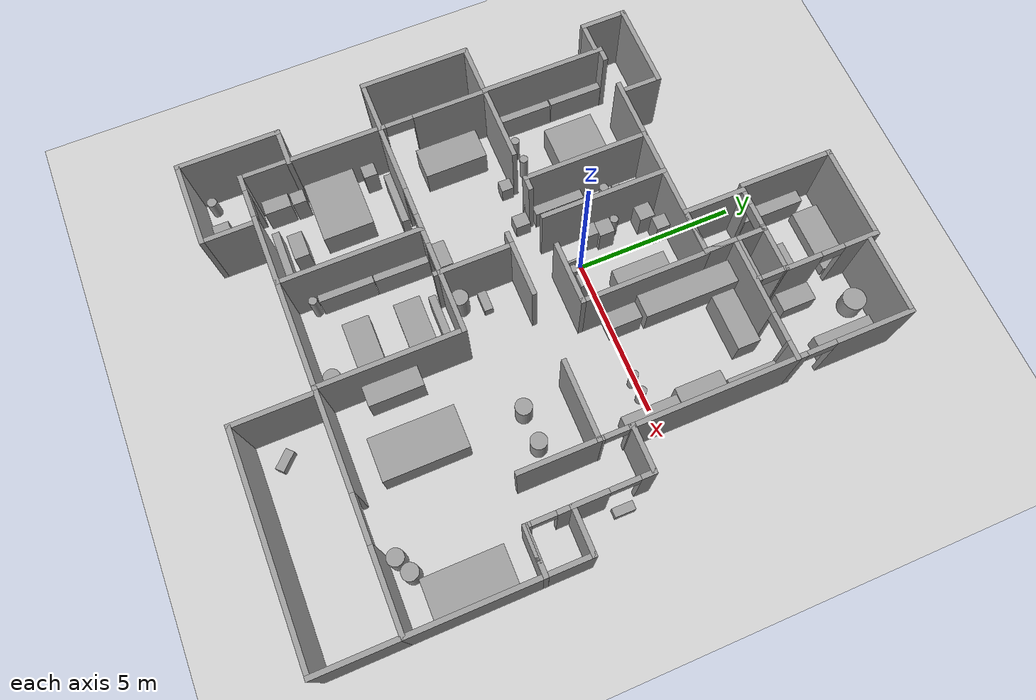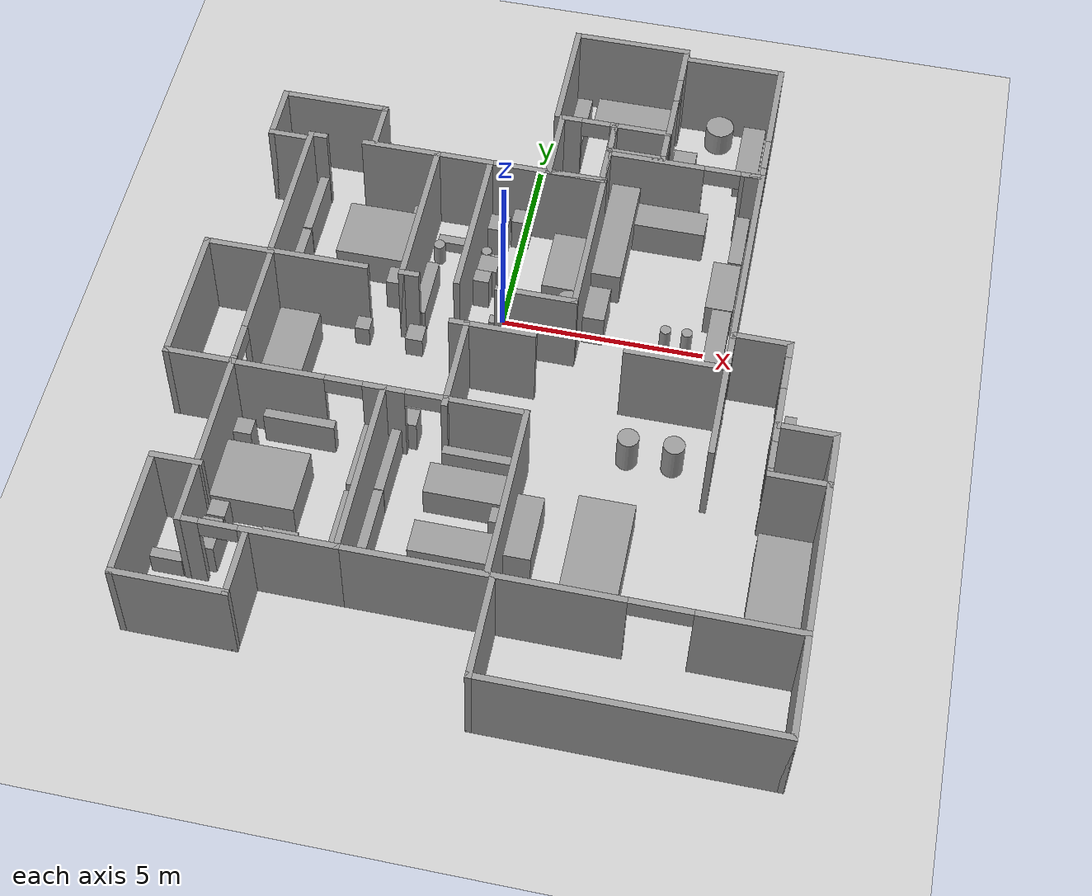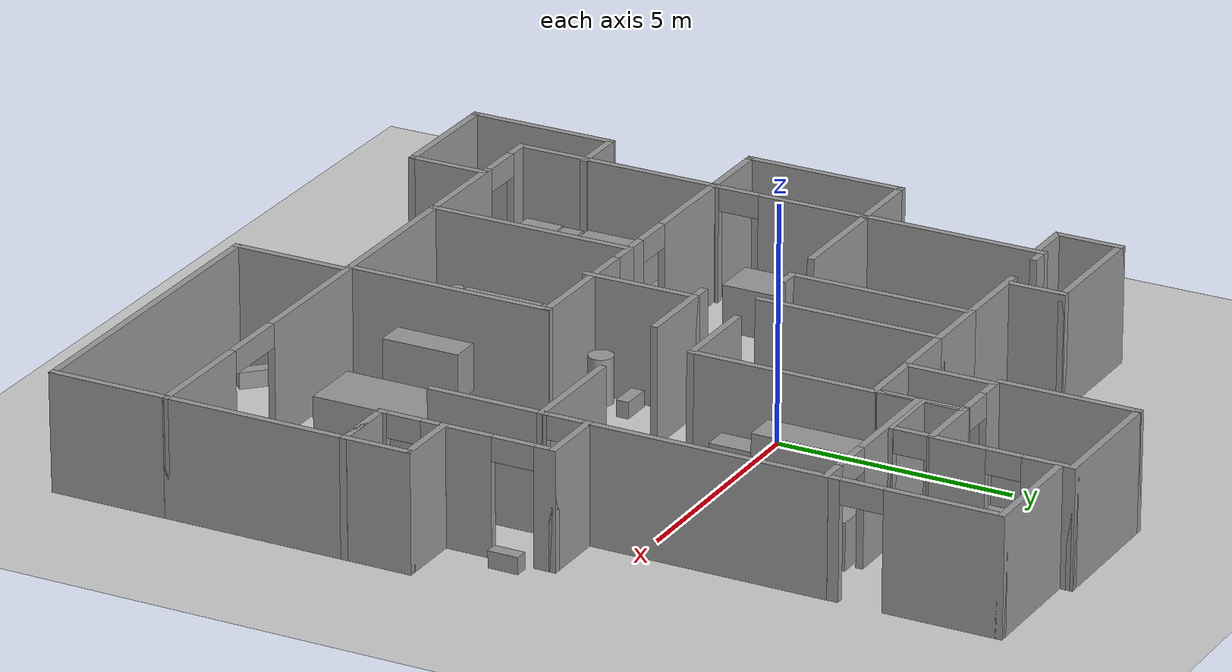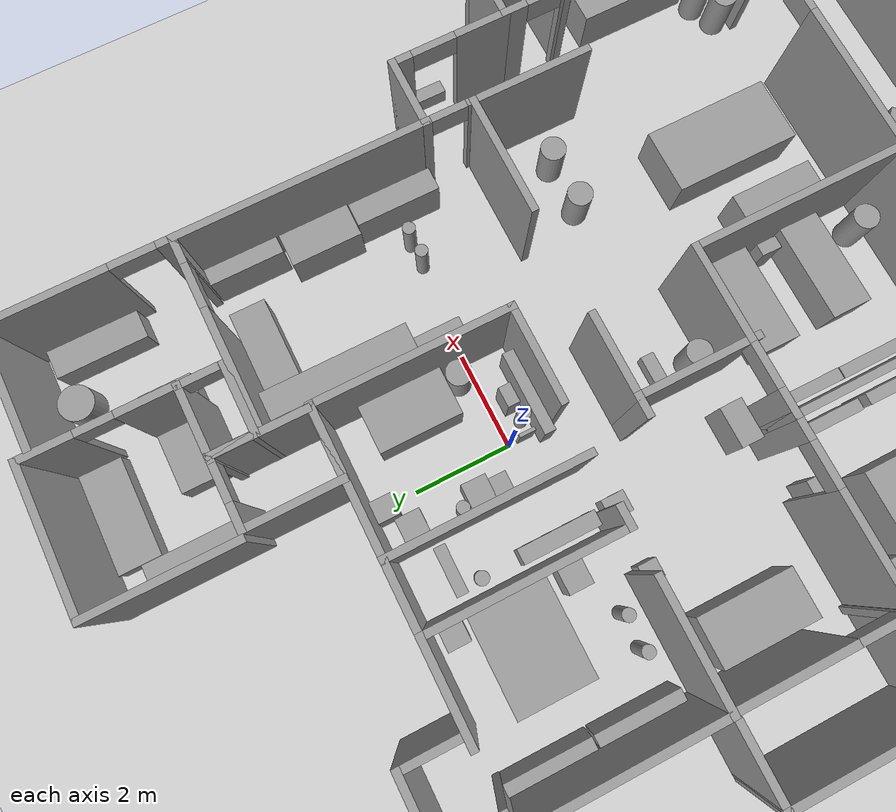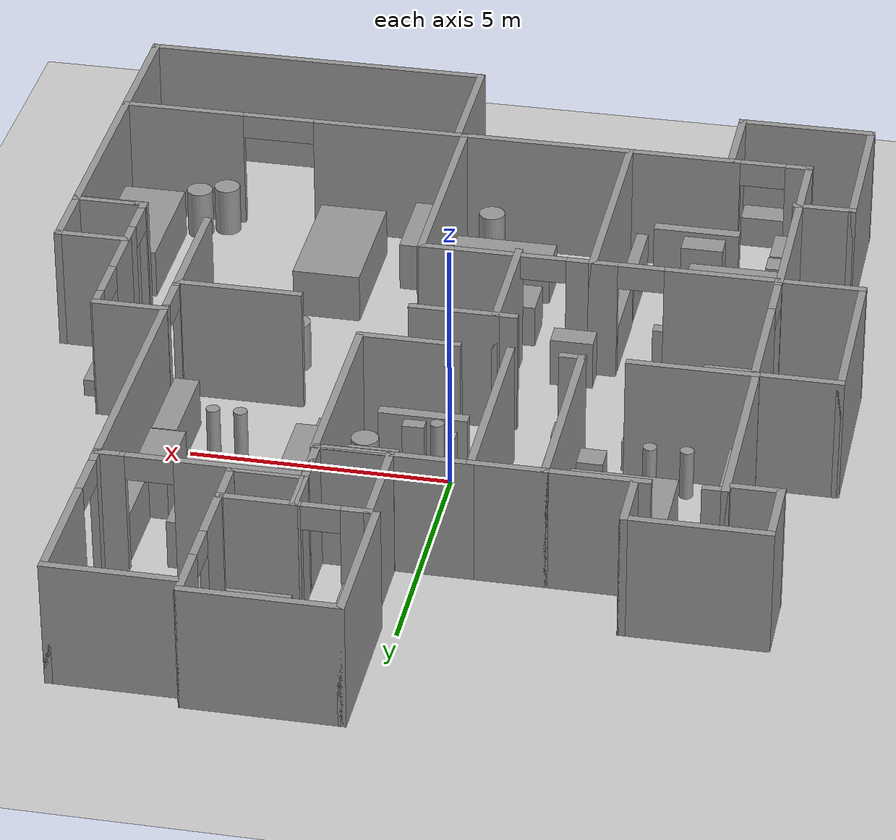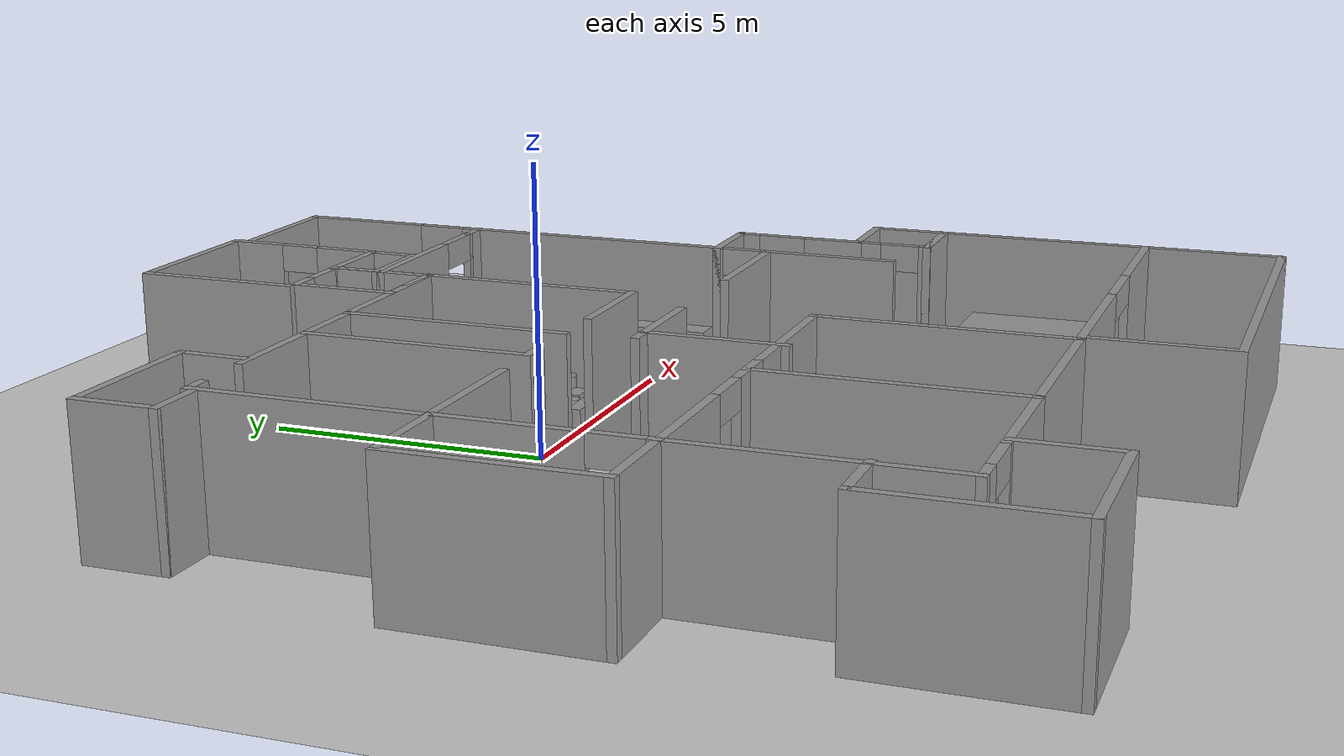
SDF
<sdf version="1.9">
 <world name="default">
  <light name="sun" type="directional">
   <pose>0 0 10 0 0 0</pose>
   <diffuse>0.800000012 0.800000012 0.800000012 1</diffuse>
   <specular>0.100000001 0.100000001 0.100000001 1</specular>
   <attenuation>
    <range>1000</range>
    <constant>0.90000000000000002</constant>
    <linear>0.01</linear>
    <quadratic>0.001</quadratic>
   </attenuation>
   <direction>-0.5 0.5 -1</direction>
   <spot><inner_angle>0</inner_angle><outer_angle>0</outer_angle><falloff>0</falloff></spot>
  </light>
  <model name="ground_plane">
   <static>true</static>
   <link name="link">
    <collision name="collision">
     <geometry><plane><normal>0 0 1</normal><size>100 100</size></plane></geometry>
     <surface><friction><ode><mu>100</mu><mu2>50</mu2></ode></friction></surface>
    </collision>
    <visual name="visual">
     <cast_shadows>false</cast_shadows>
     <geometry><plane><normal>0 0 1</normal><size>100 100</size></plane></geometry>
     <material>
      <script><uri>file://media/materials/scripts/gazebo.material</uri><name>Gazebo/Grey</name></script>
     </material>
    </visual>
   </link>
  </model>
  <gravity>0 0 -9.8000000000000007</gravity>
  <magnetic_field>6.0000000000000002e-06 2.3e-05 -4.1999999999999998e-05</magnetic_field>
  <atmosphere type="adiabatic"/>
  <physics name="default_physics" default="false" type="ode">
   <max_step_size>0.001</max_step_size>
   <real_time_factor>1</real_time_factor>
   <real_time_update_rate>1000</real_time_update_rate>
  </physics>
  <scene>
   <ambient>0.400000006 0.400000006 0.400000006 1</ambient>
   <background>0.699999988 0.699999988 0.699999988 1</background>
   <shadows>true</shadows>
  </scene>
  <spherical_coordinates>
   <surface_model>EARTH_WGS84</surface_model>
   <latitude_deg>0</latitude_deg>
   <longitude_deg>0</longitude_deg>
   <elevation>0</elevation>
   <heading_deg>0</heading_deg>
  </spherical_coordinates>
  <model name="cma_escritorio">
   <pose>-1.8304 1.03024 0 0 0 0</pose>
   <link name="Wall_11">
    <collision name="Wall_11_Collision">
     <geometry><box><size>2 0.14999999999999999 2.5</size></box></geometry>
     <pose>0 0 1.25 0 0 0</pose>
    </collision>
    <visual name="Wall_11_Visual">
     <pose>0 0 1.25 0 0 0</pose>
     <geometry><box><size>2 0.14999999999999999 2.5</size></box></geometry>
     <material>
      <script><uri>file://media/materials/scripts/gazebo.material</uri><name>Gazebo/Grey</name></script>
      <ambient>1 1 1 1</ambient>
     </material>
    </visual>
    <pose>-1.3999999999999999 1.9299999999999999 0 0 0 3.1415899999999999</pose>
   </link>
   <link name="Wall_2">
    <collision name="Wall_2_Collision">
     <geometry><box><size>4 0.14999999999999999 2.5</size></box></geometry>
     <pose>0 0 1.25 0 0 0</pose>
    </collision>
    <visual name="Wall_2_Visual">
     <pose>0 0 1.25 0 0 0</pose>
     <geometry><box><size>4 0.14999999999999999 2.5</size></box></geometry>
     <material>
      <script><uri>file://media/materials/scripts/gazebo.material</uri><name>Gazebo/Grey</name></script>
      <ambient>1 1 1 1</ambient>
     </material>
    </visual>
    <pose>0.875 0.0050000000000000001 0 0 0 1.5708</pose>
   </link>
   <link name="Wall_25">
    <collision name="Wall_25_Collision">
     <geometry><box><size>2.5 0.14999999999999999 2.5</size></box></geometry>
     <pose>0 0 1.25 0 0 0</pose>
    </collision>
    <visual name="Wall_25_Visual">
     <pose>0 0 1.25 0 0 0</pose>
     <geometry><box><size>2.5 0.14999999999999999 2.5</size></box></geometry>
     <material>
      <script><uri>file://media/materials/scripts/gazebo.material</uri><name>Gazebo/Grey</name></script>
      <ambient>1 1 1 1</ambient>
     </material>
    </visual>
    <pose>-2.5499999999999998 -1.9299999999999999 0 0 0 3.1415899999999999</pose>
   </link>
   <link name="Wall_26">
    <collision name="Wall_26_Collision">
     <geometry><box><size>4 0.14999999999999999 2.5</size></box></geometry>
     <pose>0 0 1.25 0 0 0</pose>
    </collision>
    <visual name="Wall_26_Visual">
     <pose>0 0 1.25 0 0 0</pose>
     <geometry><box><size>4 0.14999999999999999 2.5</size></box></geometry>
     <material>
      <script><uri>file://media/materials/scripts/gazebo.material</uri><name>Gazebo/Grey</name></script>
      <ambient>1 1 1 1</ambient>
     </material>
    </visual>
    <pose>-3.7250000000000001 -0.0050000000000000001 0 0 0 1.5708</pose>
   </link>
   <link name="Wall_27">
    <collision name="Wall_27_Collision">
     <geometry><box><size>0.5 0.14999999999999999 2.5</size></box></geometry>
     <pose>0 0 1.25 0 0 0</pose>
    </collision>
    <visual name="Wall_27_Visual">
     <pose>0 0 1.25 0 0 0</pose>
     <geometry><box><size>0.5 0.14999999999999999 2.5</size></box></geometry>
     <material>
      <script><uri>file://media/materials/scripts/gazebo.material</uri><name>Gazebo/Grey</name></script>
      <ambient>1 1 1 1</ambient>
     </material>
    </visual>
    <pose>-3.5499999999999998 1.9199999999999999 0 0 0 0</pose>
   </link>
   <link name="Wall_3">
    <collision name="Wall_3_Collision">
     <geometry><box><size>3 0.14999999999999999 2.5</size></box></geometry>
     <pose>0 0 1.25 0 0 0</pose>
    </collision>
    <visual name="Wall_3_Visual">
     <pose>0 0 1.25 0 0 0</pose>
     <geometry><box><size>3 0.14999999999999999 2.5</size></box></geometry>
     <material>
      <script><uri>file://media/materials/scripts/gazebo.material</uri><name>Gazebo/Grey</name></script>
      <ambient>1 1 1 1</ambient>
     </material>
    </visual>
    <pose>2.2999999999999998 1.9299999999999999 0 0 0 0</pose>
   </link>
   <link name="Wall_4">
    <collision name="Wall_4_Collision">
     <geometry><box><size>4 0.14999999999999999 2.5</size></box></geometry>
     <pose>0 0 1.25 0 0 0</pose>
    </collision>
    <visual name="Wall_4_Visual">
     <pose>0 0 1.25 0 0 0</pose>
     <geometry><box><size>4 0.14999999999999999 2.5</size></box></geometry>
     <material>
      <script><uri>file://media/materials/scripts/gazebo.material</uri><name>Gazebo/Grey</name></script>
      <ambient>1 1 1 1</ambient>
     </material>
    </visual>
    <pose>3.7250000000000001 0.0050000000000000001 0 0 0 -1.5708</pose>
   </link>
   <link name="Wall_5">
    <collision name="Wall_5_Collision">
     <geometry><box><size>2 0.14999999999999999 2.5</size></box></geometry>
     <pose>0 0 1.25 0 0 0</pose>
    </collision>
    <visual name="Wall_5_Visual">
     <pose>0 0 1.25 0 0 0</pose>
     <geometry><box><size>2 0.14999999999999999 2.5</size></box></geometry>
     <material>
      <script><uri>file://media/materials/scripts/gazebo.material</uri><name>Gazebo/Grey</name></script>
      <ambient>1 1 1 1</ambient>
     </material>
    </visual>
    <pose>2.7999999999999998 -1.9199999999999999 0 0 0 3.1415899999999999</pose>
   </link>
   <link name="Wall_7">
    <collision name="Wall_7_Collision">
     <geometry><box><size>1.5 0.14999999999999999 2.5</size></box></geometry>
     <pose>0 0 1.25 0 0 0</pose>
    </collision>
    <visual name="Wall_7_Visual">
     <pose>0 0 1.25 0 0 0</pose>
     <geometry><box><size>1.5 0.14999999999999999 2.5</size></box></geometry>
     <material>
      <script><uri>file://media/materials/scripts/gazebo.material</uri><name>Gazebo/Grey</name></script>
      <ambient>1 1 1 1</ambient>
     </material>
    </visual>
    <pose>0.20000000000000001 1.9299999999999999 0 0 0 3.1415899999999999</pose>
   </link>
   <link name="Wall_8">
    <collision name="Wall_8_Collision">
     <geometry><box><size>4 0.14999999999999999 2.5</size></box></geometry>
     <pose>0 0 1.25 0 0 0</pose>
    </collision>
    <visual name="Wall_8_Visual">
     <pose>0 0 1.25 0 0 0</pose>
     <geometry><box><size>4 0.14999999999999999 2.5</size></box></geometry>
     <material>
      <script><uri>file://media/materials/scripts/gazebo.material</uri><name>Gazebo/Grey</name></script>
      <ambient>1 1 1 1</ambient>
     </material>
    </visual>
    <pose>-0.47499999999999998 0.0050000000000000001 0 0 0 -1.5708</pose>
   </link>
   <link name="Wall_9">
    <collision name="Wall_9_Collision">
     <geometry><box><size>0.5 0.14999999999999999 2.5</size></box></geometry>
     <pose>0 0 1.25 0 0 0</pose>
    </collision>
    <visual name="Wall_9_Visual">
     <pose>0 0 1.25 0 0 0</pose>
     <geometry><box><size>0.5 0.14999999999999999 2.5</size></box></geometry>
     <material>
      <script><uri>file://media/materials/scripts/gazebo.material</uri><name>Gazebo/Grey</name></script>
      <ambient>1 1 1 1</ambient>
     </material>
    </visual>
    <pose>-0.29999999999999999 -1.9199999999999999 0 0 0 0</pose>
   </link>
   <static>true</static>
  </model>
  <model name="cma_banheiro">
   <pose>-5.2292800000000002 3.4870999999999999 0 0 0 0</pose>
   <link name="Wall_0">
    <collision name="Wall_0_Collision">
     <geometry><box><size>1 0.14999999999999999 2.5</size></box></geometry>
     <pose>0 0 1.25 0 0 0</pose>
    </collision>
    <visual name="Wall_0_Visual">
     <pose>0 0 1.25 0 0 0</pose>
     <geometry><box><size>1 0.14999999999999999 2.5</size></box></geometry>
     <material>
      <script><uri>file://media/materials/scripts/gazebo.material</uri><name>Gazebo/Grey</name></script>
      <ambient>1 1 1 1</ambient>
     </material>
    </visual>
    <pose>-0.875 -0.67500000000000004 0 0 0 3.1415899999999999</pose>
   </link>
   <link name="Wall_1">
    <collision name="Wall_1_Collision">
     <geometry><box><size>1.5 0.14999999999999999 2.5</size></box></geometry>
     <pose>0 0 1.25 0 0 0</pose>
    </collision>
    <visual name="Wall_1_Visual">
     <pose>0 0 1.25 0 0 0</pose>
     <geometry><box><size>1.5 0.14999999999999999 2.5</size></box></geometry>
     <material>
      <script><uri>file://media/materials/scripts/gazebo.material</uri><name>Gazebo/Grey</name></script>
      <ambient>1 1 1 1</ambient>
     </material>
    </visual>
    <pose>-1.3 0 0 0 0 1.5708</pose>
   </link>
   <link name="Wall_2">
    <collision name="Wall_2_Collision">
     <geometry><box><size>2.75 0.14999999999999999 2.5</size></box></geometry>
     <pose>0 0 1.25 0 0 0</pose>
    </collision>
    <visual name="Wall_2_Visual">
     <pose>0 0 1.25 0 0 0</pose>
     <geometry><box><size>2.75 0.14999999999999999 2.5</size></box></geometry>
     <material>
      <script><uri>file://media/materials/scripts/gazebo.material</uri><name>Gazebo/Grey</name></script>
      <ambient>1 1 1 1</ambient>
     </material>
    </visual>
    <pose>0 0.67500000000000004 0 0 0 0</pose>
   </link>
   <link name="Wall_4">
    <collision name="Wall_4_Collision">
     <geometry><box><size>1.25 0.14999999999999999 2.5</size></box></geometry>
     <pose>0 0 1.25 0 0 0</pose>
    </collision>
    <visual name="Wall_4_Visual">
     <pose>0 0 1.25 0 0 0</pose>
     <geometry><box><size>1.25 0.14999999999999999 2.5</size></box></geometry>
     <material>
      <script><uri>file://media/materials/scripts/gazebo.material</uri><name>Gazebo/Grey</name></script>
      <ambient>1 1 1 1</ambient>
     </material>
    </visual>
    <pose>1.3 0.125 0 0 0 -1.5708</pose>
   </link>
   <static>true</static>
  </model>
  <model name="cma_varanda1">
   <pose>-6.3251799999999996 -2.5931299999999999 0 0 0 0</pose>
   <link name="Wall_0">
    <pose>0.80000000000000004 0 0 0 0 -1.5708</pose>
    <visual name="Wall_0_Visual_0">
     <pose>-0.55249999999999999 0 1.25 0 0 0</pose>
     <geometry><box><size>2.395 0.14999999999999999 2.5</size></box></geometry>
     <material>
      <script><uri>file://media/materials/scripts/gazebo.material</uri><name>Gazebo/Grey</name></script>
      <ambient>1 1 1 1</ambient>
     </material>
    </visual>
    <collision name="Wall_0_Collision_0">
     <geometry><box><size>2.395 0.14999999999999999 2.5</size></box></geometry>
     <pose>-0.55249999999999999 0 1.25 0 0 0</pose>
    </collision>
    <visual name="Wall_0_Visual_1">
     <pose>1.6375 0 1.25 0 0 0</pose>
     <geometry><box><size>0.22500000000000001 0.14999999999999999 2.5</size></box></geometry>
     <material>
      <script><uri>file://media/materials/scripts/gazebo.material</uri><name>Gazebo/Grey</name></script>
      <ambient>1 1 1 1</ambient>
     </material>
    </visual>
    <collision name="Wall_0_Collision_1">
     <geometry><box><size>0.22500000000000001 0.14999999999999999 2.5</size></box></geometry>
     <pose>1.6375 0 1.25 0 0 0</pose>
    </collision>
    <visual name="Wall_0_Visual_2">
     <pose>1.085 0 2.25 0 0 0</pose>
     <geometry><box><size>0.88 0.14999999999999999 0.5</size></box></geometry>
     <material>
      <script><uri>file://media/materials/scripts/gazebo.material</uri><name>Gazebo/Grey</name></script>
      <ambient>1 1 1 1</ambient>
     </material>
    </visual>
    <collision name="Wall_0_Collision_2">
     <geometry><box><size>0.88 0.14999999999999999 0.5</size></box></geometry>
     <pose>1.085 0 2.25 0 0 0</pose>
    </collision>
   </link>
   <link name="Wall_1">
    <collision name="Wall_1_Collision">
     <geometry><box><size>1.75 0.14999999999999999 2.5</size></box></geometry>
     <pose>0 0 1.25 0 0 0</pose>
    </collision>
    <visual name="Wall_1_Visual">
     <pose>0 0 1.25 0 0 0</pose>
     <geometry><box><size>1.75 0.14999999999999999 2.5</size></box></geometry>
     <material>
      <script><uri>file://media/materials/scripts/gazebo.material</uri><name>Gazebo/Grey</name></script>
      <ambient>1 1 1 1</ambient>
     </material>
    </visual>
    <pose>0 -1.675 0 0 0 3.1415899999999999</pose>
   </link>
   <link name="Wall_2">
    <collision name="Wall_2_Collision">
     <geometry><box><size>3.5 0.14999999999999999 2.5</size></box></geometry>
     <pose>0 0 1.25 0 0 0</pose>
    </collision>
    <visual name="Wall_2_Visual">
     <pose>0 0 1.25 0 0 0</pose>
     <geometry><box><size>3.5 0.14999999999999999 2.5</size></box></geometry>
     <material>
      <script><uri>file://media/materials/scripts/gazebo.material</uri><name>Gazebo/Grey</name></script>
      <ambient>1 1 1 1</ambient>
     </material>
    </visual>
    <pose>-0.80000000000000004 0 0 0 0 1.5708</pose>
   </link>
   <link name="Wall_3">
    <collision name="Wall_3_Collision">
     <geometry><box><size>1.75 0.14999999999999999 2.5</size></box></geometry>
     <pose>0 0 1.25 0 0 0</pose>
    </collision>
    <visual name="Wall_3_Visual">
     <pose>0 0 1.25 0 0 0</pose>
     <geometry><box><size>1.75 0.14999999999999999 2.5</size></box></geometry>
     <material>
      <script><uri>file://media/materials/scripts/gazebo.material</uri><name>Gazebo/Grey</name></script>
      <ambient>1 1 1 1</ambient>
     </material>
    </visual>
    <pose>0 1.675 0 0 0 0</pose>
   </link>
   <static>true</static>
  </model>
  <model name="cma_quartos">
   <pose>-2.58169 -7.2645600000000004 0 0 0 0</pose>
   <link name="Wall_0">
    <collision name="Wall_0_Collision">
     <geometry><box><size>4.5 0.14999999999999999 2.5</size></box></geometry>
     <pose>0 0 1.25 0 0 0</pose>
    </collision>
    <visual name="Wall_0_Visual">
     <pose>0 0 1.25 0 0 0</pose>
     <geometry><box><size>4.5 0.14999999999999999 2.5</size></box></geometry>
     <material>
      <script><uri>file://media/materials/scripts/gazebo.material</uri><name>Gazebo/Grey</name></script>
      <ambient>1 1 1 1</ambient>
     </material>
    </visual>
    <pose>0.64500000000000002 0.81000000000000005 0 0 0 -1.5708</pose>
   </link>
   <link name="Wall_1">
    <pose>-1.155 -1.365 0 0 0 3.1415899999999999</pose>
    <visual name="Wall_1_Visual_0">
     <pose>-0.72250000000000003 0 1.25 0 0 0</pose>
     <geometry><box><size>2.3050000000000002 0.14999999999999999 2.5</size></box></geometry>
     <material>
      <script><uri>file://media/materials/scripts/gazebo.material</uri><name>Gazebo/Grey</name></script>
      <ambient>1 1 1 1</ambient>
     </material>
    </visual>
    <collision name="Wall_1_Collision_0">
     <geometry><box><size>2.3050000000000002 0.14999999999999999 2.5</size></box></geometry>
     <pose>-0.72250000000000003 0 1.25 0 0 0</pose>
    </collision>
    <visual name="Wall_1_Visual_1">
     <pose>1.6025 0 1.25 0 0 0</pose>
     <geometry><box><size>0.54500000000000004 0.14999999999999999 2.5</size></box></geometry>
     <material>
      <script><uri>file://media/materials/scripts/gazebo.material</uri><name>Gazebo/Grey</name></script>
      <ambient>1 1 1 1</ambient>
     </material>
    </visual>
    <collision name="Wall_1_Collision_1">
     <geometry><box><size>0.54500000000000004 0.14999999999999999 2.5</size></box></geometry>
     <pose>1.6025 0 1.25 0 0 0</pose>
    </collision>
    <visual name="Wall_1_Visual_2">
     <pose>0.88 0 2.25 0 0 0</pose>
     <geometry><box><size>0.90000000000000002 0.14999999999999999 0.5</size></box></geometry>
     <material>
      <script><uri>file://media/materials/scripts/gazebo.material</uri><name>Gazebo/Grey</name></script>
      <ambient>1 1 1 1</ambient>
     </material>
    </visual>
    <collision name="Wall_1_Collision_2">
     <geometry><box><size>0.90000000000000002 0.14999999999999999 0.5</size></box></geometry>
     <pose>0.88 0 2.25 0 0 0</pose>
    </collision>
   </link>
   <link name="Wall_10">
    <collision name="Wall_10_Collision">
     <geometry><box><size>1.75 0.14999999999999999 2.5</size></box></geometry>
     <pose>0 0 1.25 0 0 0</pose>
    </collision>
    <visual name="Wall_10_Visual">
     <pose>0 0 1.25 0 0 0</pose>
     <geometry><box><size>1.75 0.14999999999999999 2.5</size></box></geometry>
     <material>
      <script><uri>file://media/materials/scripts/gazebo.material</uri><name>Gazebo/Grey</name></script>
      <ambient>1 1 1 1</ambient>
     </material>
    </visual>
    <pose>-1.395 -2.1850000000000001 0 0 0 -1.5708</pose>
   </link>
   <link name="Wall_11">
    <collision name="Wall_11_Collision">
     <geometry><box><size>2.75 0.14999999999999999 2.5</size></box></geometry>
     <pose>0 0 1.25 0 0 0</pose>
    </collision>
    <visual name="Wall_11_Visual">
     <pose>0 0 1.25 0 0 0</pose>
     <geometry><box><size>2.75 0.14999999999999999 2.5</size></box></geometry>
     <material>
      <script><uri>file://media/materials/scripts/gazebo.material</uri><name>Gazebo/Grey</name></script>
      <ambient>1 1 1 1</ambient>
     </material>
    </visual>
    <pose>-2.6949999999999998 -2.9849999999999999 0 0 0 3.1415899999999999</pose>
   </link>
   <link name="Wall_12">
    <collision name="Wall_12_Collision">
     <geometry><box><size>3.25 0.14999999999999999 2.5</size></box></geometry>
     <pose>0 0 1.25 0 0 0</pose>
    </collision>
    <visual name="Wall_12_Visual">
     <pose>0 0 1.25 0 0 0</pose>
     <geometry><box><size>3.25 0.14999999999999999 2.5</size></box></geometry>
     <material>
      <script><uri>file://media/materials/scripts/gazebo.material</uri><name>Gazebo/Grey</name></script>
      <ambient>1 1 1 1</ambient>
     </material>
    </visual>
    <pose>-3.9950000000000001 -1.4350000000000001 0 0 0 1.5708</pose>
   </link>
   <link name="Wall_13">
    <collision name="Wall_13_Collision">
     <geometry><box><size>1.25 0.14999999999999999 2.5</size></box></geometry>
     <pose>0 0 1.25 0 0 0</pose>
    </collision>
    <visual name="Wall_13_Visual">
     <pose>0 0 1.25 0 0 0</pose>
     <geometry><box><size>1.25 0.14999999999999999 2.5</size></box></geometry>
     <material>
      <script><uri>file://media/materials/scripts/gazebo.material</uri><name>Gazebo/Grey</name></script>
      <ambient>1 1 1 1</ambient>
     </material>
    </visual>
    <pose>-3.4449999999999998 0.115 0 0 0 0</pose>
   </link>
   <link name="Wall_2">
    <collision name="Wall_2_Collision">
     <geometry><box><size>4.5 0.14999999999999999 2.5</size></box></geometry>
     <pose>0 0 1.25 0 0 0</pose>
    </collision>
    <visual name="Wall_2_Visual">
     <pose>0 0 1.25 0 0 0</pose>
     <geometry><box><size>4.5 0.14999999999999999 2.5</size></box></geometry>
     <material>
      <script><uri>file://media/materials/scripts/gazebo.material</uri><name>Gazebo/Grey</name></script>
      <ambient>1 1 1 1</ambient>
     </material>
    </visual>
    <pose>-2.9550000000000001 0.81000000000000005 0 0 0 1.5708</pose>
   </link>
   <link name="Wall_3">
    <pose>-1.155 2.9849999999999999 0 0 0 0</pose>
    <visual name="Wall_3_Visual_0">
     <pose>-0.73250000000000004 0 1.25 0 0 0</pose>
     <geometry><box><size>2.2850000000000001 0.14999999999999999 2.5</size></box></geometry>
     <material>
      <script><uri>file://media/materials/scripts/gazebo.material</uri><name>Gazebo/Grey</name></script>
      <ambient>1 1 1 1</ambient>
     </material>
    </visual>
    <collision name="Wall_3_Collision_0">
     <geometry><box><size>2.2850000000000001 0.14999999999999999 2.5</size></box></geometry>
     <pose>-0.73250000000000004 0 1.25 0 0 0</pose>
    </collision>
    <visual name="Wall_3_Visual_1">
     <pose>1.5925 0 1.25 0 0 0</pose>
     <geometry><box><size>0.56499999999999995 0.14999999999999999 2.5</size></box></geometry>
     <material>
      <script><uri>file://media/materials/scripts/gazebo.material</uri><name>Gazebo/Grey</name></script>
      <ambient>1 1 1 1</ambient>
     </material>
    </visual>
    <collision name="Wall_3_Collision_1">
     <geometry><box><size>0.56499999999999995 0.14999999999999999 2.5</size></box></geometry>
     <pose>1.5925 0 1.25 0 0 0</pose>
    </collision>
    <visual name="Wall_3_Visual_2">
     <pose>0.85999999999999999 0 2.25 0 0 0</pose>
     <geometry><box><size>0.90000000000000002 0.14999999999999999 0.5</size></box></geometry>
     <material>
      <script><uri>file://media/materials/scripts/gazebo.material</uri><name>Gazebo/Grey</name></script>
      <ambient>1 1 1 1</ambient>
     </material>
    </visual>
    <collision name="Wall_3_Collision_2">
     <geometry><box><size>0.90000000000000002 0.14999999999999999 0.5</size></box></geometry>
     <pose>0.85999999999999999 0 2.25 0 0 0</pose>
    </collision>
   </link>
   <link name="Wall_6">
    <pose>2.3199999999999998 2.9849999999999999 0 0 0 0</pose>
    <visual name="Wall_6_Visual_0">
     <pose>-1.4575 0 1.25 0 0 0</pose>
     <geometry><box><size>0.58499999999999996 0.14999999999999999 2.5</size></box></geometry>
     <material>
      <script><uri>file://media/materials/scripts/gazebo.material</uri><name>Gazebo/Grey</name></script>
      <ambient>1 1 1 1</ambient>
     </material>
    </visual>
    <collision name="Wall_6_Collision_0">
     <geometry><box><size>0.58499999999999996 0.14999999999999999 2.5</size></box></geometry>
     <pose>-1.4575 0 1.25 0 0 0</pose>
    </collision>
    <visual name="Wall_6_Visual_1">
     <pose>0.74250000000000005 0 1.25 0 0 0</pose>
     <geometry><box><size>2.0150000000000001 0.14999999999999999 2.5</size></box></geometry>
     <material>
      <script><uri>file://media/materials/scripts/gazebo.material</uri><name>Gazebo/Grey</name></script>
      <ambient>1 1 1 1</ambient>
     </material>
    </visual>
    <collision name="Wall_6_Collision_1">
     <geometry><box><size>2.0150000000000001 0.14999999999999999 2.5</size></box></geometry>
     <pose>0.74250000000000005 0 1.25 0 0 0</pose>
    </collision>
    <visual name="Wall_6_Visual_2">
     <pose>-0.71499999999999997 0 2.25 0 0 0</pose>
     <geometry><box><size>0.90000000000000002 0.14999999999999999 0.5</size></box></geometry>
     <material>
      <script><uri>file://media/materials/scripts/gazebo.material</uri><name>Gazebo/Grey</name></script>
      <ambient>1 1 1 1</ambient>
     </material>
    </visual>
    <collision name="Wall_6_Collision_2">
     <geometry><box><size>0.90000000000000002 0.14999999999999999 0.5</size></box></geometry>
     <pose>-0.71499999999999997 0 2.25 0 0 0</pose>
    </collision>
   </link>
   <link name="Wall_7">
    <collision name="Wall_7_Collision">
     <geometry><box><size>4.5 0.14999999999999999 2.5</size></box></geometry>
     <pose>0 0 1.25 0 0 0</pose>
    </collision>
    <visual name="Wall_7_Visual">
     <pose>0 0 1.25 0 0 0</pose>
     <geometry><box><size>4.5 0.14999999999999999 2.5</size></box></geometry>
     <material>
      <script><uri>file://media/materials/scripts/gazebo.material</uri><name>Gazebo/Grey</name></script>
      <ambient>1 1 1 1</ambient>
     </material>
    </visual>
    <pose>3.9950000000000001 0.81000000000000005 0 0 0 -1.5708</pose>
   </link>
   <link name="Wall_8">
    <collision name="Wall_8_Collision">
     <geometry><box><size>3.5 0.14999999999999999 2.5</size></box></geometry>
     <pose>0 0 1.25 0 0 0</pose>
    </collision>
    <visual name="Wall_8_Visual">
     <pose>0 0 1.25 0 0 0</pose>
     <geometry><box><size>3.5 0.14999999999999999 2.5</size></box></geometry>
     <material>
      <script><uri>file://media/materials/scripts/gazebo.material</uri><name>Gazebo/Grey</name></script>
      <ambient>1 1 1 1</ambient>
     </material>
    </visual>
    <pose>2.3199999999999998 -1.365 0 0 0 3.1415899999999999</pose>
   </link>
   <static>true</static>
  </model>
  <model name="cma_parede_t">
   <pose>0.15995500000000001 -3.2401599999999999 0 0 0 0</pose>
   <link name="Wall_15">
    <collision name="Wall_15_Collision">
     <geometry><box><size>2.5 0.14999999999999999 2.5</size></box></geometry>
     <pose>0 0 1.25 0 0 0</pose>
    </collision>
    <visual name="Wall_15_Visual">
     <pose>0 0 1.25 0 0 0</pose>
     <geometry><box><size>2.5 0.14999999999999999 2.5</size></box></geometry>
     <material>
      <script><uri>file://media/materials/scripts/gazebo.material</uri><name>Gazebo/Grey</name></script>
      <ambient>1 1 1 1</ambient>
     </material>
    </visual>
    <pose>-0.625 0 0 0 0 1.5708</pose>
   </link>
   <link name="Wall_16">
    <collision name="Wall_16_Collision">
     <geometry><box><size>0.5 0.14999999999999999 2.5</size></box></geometry>
     <pose>0 0 1.25 0 0 0</pose>
    </collision>
    <visual name="Wall_16_Visual">
     <pose>0 0 1.25 0 0 0</pose>
     <geometry><box><size>0.5 0.14999999999999999 2.5</size></box></geometry>
     <material>
      <script><uri>file://media/materials/scripts/gazebo.material</uri><name>Gazebo/Grey</name></script>
      <ambient>1 1 1 1</ambient>
     </material>
    </visual>
    <pose>-0.80000000000000004 1.175 0 0 0 3.1415899999999999</pose>
   </link>
   <link name="Wall_18">
    <collision name="Wall_18_Collision">
     <geometry><box><size>1.75 0.14999999999999999 2.5</size></box></geometry>
     <pose>0 0 1.25 0 0 0</pose>
    </collision>
    <visual name="Wall_18_Visual">
     <pose>0 0 1.25 0 0 0</pose>
     <geometry><box><size>1.75 0.14999999999999999 2.5</size></box></geometry>
     <material>
      <script><uri>file://media/materials/scripts/gazebo.material</uri><name>Gazebo/Grey</name></script>
      <ambient>1 1 1 1</ambient>
     </material>
    </visual>
    <pose>0.17499999999999999 1.175 0 0 0 0</pose>
   </link>
   <static>true</static>
  </model>
  <model name="cma_parede_L">
   <pose>4.97628 -6.6999199999999997 0 0 0 0</pose>
   <link name="Wall_0">
    <pose>0 -1.925 0 0 0 0</pose>
    <visual name="Wall_0_Visual_0">
     <pose>-1.9850000000000001 0 1.25 0 0 0</pose>
     <geometry><box><size>3.0299999999999998 0.14999999999999999 2.5</size></box></geometry>
     <material>
      <script><uri>file://media/materials/scripts/gazebo.material</uri><name>Gazebo/Grey</name></script>
      <ambient>1 1 1 1</ambient>
     </material>
    </visual>
    <collision name="Wall_0_Collision_0">
     <geometry><box><size>3.0299999999999998 0.14999999999999999 2.5</size></box></geometry>
     <pose>-1.9850000000000001 0 1.25 0 0 0</pose>
    </collision>
    <visual name="Wall_0_Visual_1">
     <pose>2.2400000000000002 0 1.25 0 0 0</pose>
     <geometry><box><size>2.52 0.14999999999999999 2.5</size></box></geometry>
     <material>
      <script><uri>file://media/materials/scripts/gazebo.material</uri><name>Gazebo/Grey</name></script>
      <ambient>1 1 1 1</ambient>
     </material>
    </visual>
    <collision name="Wall_0_Collision_1">
     <geometry><box><size>2.52 0.14999999999999999 2.5</size></box></geometry>
     <pose>2.2400000000000002 0 1.25 0 0 0</pose>
    </collision>
    <visual name="Wall_0_Visual_2">
     <pose>0.255 0 2.25 0 0 0</pose>
     <geometry><box><size>1.45 0.14999999999999999 0.5</size></box></geometry>
     <material>
      <script><uri>file://media/materials/scripts/gazebo.material</uri><name>Gazebo/Grey</name></script>
      <ambient>1 1 1 1</ambient>
     </material>
    </visual>
    <collision name="Wall_0_Collision_2">
     <geometry><box><size>1.45 0.14999999999999999 0.5</size></box></geometry>
     <pose>0.255 0 2.25 0 0 0</pose>
    </collision>
   </link>
   <link name="Wall_1">
    <collision name="Wall_1_Collision">
     <geometry><box><size>4 0.14999999999999999 2.5</size></box></geometry>
     <pose>0 0 1.25 0 0 0</pose>
    </collision>
    <visual name="Wall_1_Visual">
     <pose>0 0 1.25 0 0 0</pose>
     <geometry><box><size>4 0.14999999999999999 2.5</size></box></geometry>
     <material>
      <script><uri>file://media/materials/scripts/gazebo.material</uri><name>Gazebo/Grey</name></script>
      <ambient>1 1 1 1</ambient>
     </material>
    </visual>
    <pose>3.4249999999999998 0 0 0 0 1.5708</pose>
   </link>
   <link name="Wall_2">
    <collision name="Wall_2_Collision">
     <geometry><box><size>1.5 0.14999999999999999 2.5</size></box></geometry>
     <pose>0 0 1.25 0 0 0</pose>
    </collision>
    <visual name="Wall_2_Visual">
     <pose>0 0 1.25 0 0 0</pose>
     <geometry><box><size>1.5 0.14999999999999999 2.5</size></box></geometry>
     <material>
      <script><uri>file://media/materials/scripts/gazebo.material</uri><name>Gazebo/Grey</name></script>
      <ambient>1 1 1 1</ambient>
     </material>
    </visual>
    <pose>2.75 1.925 0 0 0 3.1415899999999999</pose>
   </link>
   <static>true</static>
  </model>
  <model name="cma_lavabo">
   <pose>7.7229700000000001 -4.0930200000000001 0 0 0 0</pose>
   <link name="Wall_4">
    <pose>-0.67500000000000004 0 0 0 0 1.5708</pose>
    <visual name="Wall_4_Visual_0">
     <pose>-0.63500000000000001 0 1.25 0 0 0</pose>
     <geometry><box><size>0.23000000000000001 0.14999999999999999 2.5</size></box></geometry>
     <material>
      <script><uri>file://media/materials/scripts/gazebo.material</uri><name>Gazebo/Grey</name></script>
      <ambient>1 1 1 1</ambient>
     </material>
    </visual>
    <collision name="Wall_4_Collision_0">
     <geometry><box><size>0.23000000000000001 0.14999999999999999 2.5</size></box></geometry>
     <pose>-0.63500000000000001 0 1.25 0 0 0</pose>
    </collision>
    <visual name="Wall_4_Visual_1">
     <pose>0.47999999999999998 0 1.25 0 0 0</pose>
     <geometry><box><size>0.54000000000000004 0.14999999999999999 2.5</size></box></geometry>
     <material>
      <script><uri>file://media/materials/scripts/gazebo.material</uri><name>Gazebo/Grey</name></script>
      <ambient>1 1 1 1</ambient>
     </material>
    </visual>
    <collision name="Wall_4_Collision_1">
     <geometry><box><size>0.54000000000000004 0.14999999999999999 2.5</size></box></geometry>
     <pose>0.47999999999999998 0 1.25 0 0 0</pose>
    </collision>
    <visual name="Wall_4_Visual_2">
     <pose>-0.155 0 2.25 0 0 0</pose>
     <geometry><box><size>0.72999999999999998 0.14999999999999999 0.5</size></box></geometry>
     <material>
      <script><uri>file://media/materials/scripts/gazebo.material</uri><name>Gazebo/Grey</name></script>
      <ambient>1 1 1 1</ambient>
     </material>
    </visual>
    <collision name="Wall_4_Collision_2">
     <geometry><box><size>0.72999999999999998 0.14999999999999999 0.5</size></box></geometry>
     <pose>-0.155 0 2.25 0 0 0</pose>
    </collision>
   </link>
   <link name="Wall_5">
    <collision name="Wall_5_Collision">
     <geometry><box><size>1.5 0.14999999999999999 2.5</size></box></geometry>
     <pose>0 0 1.25 0 0 0</pose>
    </collision>
    <visual name="Wall_5_Visual">
     <pose>0 0 1.25 0 0 0</pose>
     <geometry><box><size>1.5 0.14999999999999999 2.5</size></box></geometry>
     <material>
      <script><uri>file://media/materials/scripts/gazebo.material</uri><name>Gazebo/Grey</name></script>
      <ambient>1 1 1 1</ambient>
     </material>
    </visual>
    <pose>0 0.67500000000000004 0 0 0 0</pose>
   </link>
   <link name="Wall_6">
    <collision name="Wall_6_Collision">
     <geometry><box><size>1.5 0.14999999999999999 2.5</size></box></geometry>
     <pose>0 0 1.25 0 0 0</pose>
    </collision>
    <visual name="Wall_6_Visual">
     <pose>0 0 1.25 0 0 0</pose>
     <geometry><box><size>1.5 0.14999999999999999 2.5</size></box></geometry>
     <material>
      <script><uri>file://media/materials/scripts/gazebo.material</uri><name>Gazebo/Grey</name></script>
      <ambient>1 1 1 1</ambient>
     </material>
    </visual>
    <pose>0.67500000000000004 0 0 0 0 -1.5708</pose>
   </link>
   <link name="Wall_7">
    <collision name="Wall_7_Collision">
     <geometry><box><size>1.5 0.14999999999999999 2.5</size></box></geometry>
     <pose>0 0 1.25 0 0 0</pose>
    </collision>
    <visual name="Wall_7_Visual">
     <pose>0 0 1.25 0 0 0</pose>
     <geometry><box><size>1.5 0.14999999999999999 2.5</size></box></geometry>
     <material>
      <script><uri>file://media/materials/scripts/gazebo.material</uri><name>Gazebo/Grey</name></script>
      <ambient>1 1 1 1</ambient>
     </material>
    </visual>
    <pose>0 -0.67500000000000004 0 0 0 3.1415899999999999</pose>
   </link>
   <static>true</static>
  </model>
  <model name="cma_L2">
   <pose>4.5168299999999997 -3.24587 0 0 0 0</pose>
   <link name="Wall_10">
    <collision name="Wall_10_Collision">
     <geometry><box><size>2.5 0.14999999999999999 2.5</size></box></geometry>
     <pose>0 0 1.25 0 0 0</pose>
    </collision>
    <visual name="Wall_10_Visual">
     <pose>0 0 1.25 0 0 0</pose>
     <geometry><box><size>2.5 0.14999999999999999 2.5</size></box></geometry>
     <material>
      <script><uri>file://media/materials/scripts/gazebo.material</uri><name>Gazebo/Grey</name></script>
      <ambient>1 1 1 1</ambient>
     </material>
    </visual>
    <pose>1.175 0 0 0 0 -1.5708</pose>
   </link>
   <link name="Wall_9">
    <collision name="Wall_9_Collision">
     <geometry><box><size>2.5 0.14999999999999999 2.5</size></box></geometry>
     <pose>0 0 1.25 0 0 0</pose>
    </collision>
    <visual name="Wall_9_Visual">
     <pose>0 0 1.25 0 0 0</pose>
     <geometry><box><size>2.5 0.14999999999999999 2.5</size></box></geometry>
     <material>
      <script><uri>file://media/materials/scripts/gazebo.material</uri><name>Gazebo/Grey</name></script>
      <ambient>1 1 1 1</ambient>
     </material>
    </visual>
    <pose>0 1.175 0 0 0 0</pose>
   </link>
   <static>true</static>
  </model>
  <model name="cma_L3">
   <pose>6.3722099999999999 -2.2602199999999999 0 0 0 0</pose>
   <link name="Wall_12">
    <pose>-0.67500000000000004 0.75 0 0 0 1.5708</pose>
    <visual name="Wall_12_Visual_0">
     <pose>-0.46000000000000002 0 1.25 0 0 0</pose>
     <geometry><box><size>0.080000000000000002 0.14999999999999999 2.5</size></box></geometry>
     <material>
      <script><uri>file://media/materials/scripts/gazebo.material</uri><name>Gazebo/Grey</name></script>
      <ambient>1 1 1 1</ambient>
     </material>
    </visual>
    <collision name="Wall_12_Collision_0">
     <geometry><box><size>0.080000000000000002 0.14999999999999999 2.5</size></box></geometry>
     <pose>-0.46000000000000002 0 1.25 0 0 0</pose>
    </collision>
    <visual name="Wall_12_Visual_1">
     <pose>0.40500000000000003 0 1.25 0 0 0</pose>
     <geometry><box><size>0.19 0.14999999999999999 2.5</size></box></geometry>
     <material>
      <script><uri>file://media/materials/scripts/gazebo.material</uri><name>Gazebo/Grey</name></script>
      <ambient>1 1 1 1</ambient>
     </material>
    </visual>
    <collision name="Wall_12_Collision_1">
     <geometry><box><size>0.19 0.14999999999999999 2.5</size></box></geometry>
     <pose>0.40500000000000003 0 1.25 0 0 0</pose>
    </collision>
    <visual name="Wall_12_Visual_2">
     <pose>-0.055 0 2.25 0 0 0</pose>
     <geometry><box><size>0.72999999999999998 0.14999999999999999 0.5</size></box></geometry>
     <material>
      <script><uri>file://media/materials/scripts/gazebo.material</uri><name>Gazebo/Grey</name></script>
      <ambient>1 1 1 1</ambient>
     </material>
    </visual>
    <collision name="Wall_12_Collision_2">
     <geometry><box><size>0.72999999999999998 0.14999999999999999 0.5</size></box></geometry>
     <pose>-0.055 0 2.25 0 0 0</pose>
    </collision>
   </link>
   <link name="Wall_13">
    <collision name="Wall_13_Collision">
     <geometry><box><size>1.5 0.14999999999999999 2.5</size></box></geometry>
     <pose>0 0 1.25 0 0 0</pose>
    </collision>
    <visual name="Wall_13_Visual">
     <pose>0 0 1.25 0 0 0</pose>
     <geometry><box><size>1.5 0.14999999999999999 2.5</size></box></geometry>
     <material>
      <script><uri>file://media/materials/scripts/gazebo.material</uri><name>Gazebo/Grey</name></script>
      <ambient>1 1 1 1</ambient>
     </material>
    </visual>
    <pose>0 1.175 0 0 0 0</pose>
   </link>
   <link name="Wall_14">
    <pose>0.67500000000000004 0 0 0 0 -1.5708</pose>
    <visual name="Wall_14_Visual_0">
     <pose>-1.0175000000000001 0 1.25 0 0 0</pose>
     <geometry><box><size>0.46500000000000002 0.14999999999999999 2.5</size></box></geometry>
     <material>
      <script><uri>file://media/materials/scripts/gazebo.material</uri><name>Gazebo/Grey</name></script>
      <ambient>1 1 1 1</ambient>
     </material>
    </visual>
    <collision name="Wall_14_Collision_0">
     <geometry><box><size>0.46500000000000002 0.14999999999999999 2.5</size></box></geometry>
     <pose>-1.0175000000000001 0 1.25 0 0 0</pose>
    </collision>
    <visual name="Wall_14_Visual_1">
     <pose>0.6825 0 1.25 0 0 0</pose>
     <geometry><box><size>1.135 0.14999999999999999 2.5</size></box></geometry>
     <material>
      <script><uri>file://media/materials/scripts/gazebo.material</uri><name>Gazebo/Grey</name></script>
      <ambient>1 1 1 1</ambient>
     </material>
    </visual>
    <collision name="Wall_14_Collision_1">
     <geometry><box><size>1.135 0.14999999999999999 2.5</size></box></geometry>
     <pose>0.6825 0 1.25 0 0 0</pose>
    </collision>
    <visual name="Wall_14_Visual_2">
     <pose>-0.33500000000000002 0 2.25 0 0 0</pose>
     <geometry><box><size>0.90000000000000002 0.14999999999999999 0.5</size></box></geometry>
     <material>
      <script><uri>file://media/materials/scripts/gazebo.material</uri><name>Gazebo/Grey</name></script>
      <ambient>1 1 1 1</ambient>
     </material>
    </visual>
    <collision name="Wall_14_Collision_2">
     <geometry><box><size>0.90000000000000002 0.14999999999999999 0.5</size></box></geometry>
     <pose>-0.33500000000000002 0 2.25 0 0 0</pose>
    </collision>
   </link>
   <static>true</static>
  </model>
  <model name="cma_U">
   <pose>4.9789500000000002 -9.92408 0 0 0 0</pose>
   <link name="Wall_16">
    <collision name="Wall_16_Collision">
     <geometry><box><size>2.5 0.14999999999999999 2.5</size></box></geometry>
     <pose>0 0 1.25 0 0 0</pose>
    </collision>
    <visual name="Wall_16_Visual">
     <pose>0 0 1.25 0 0 0</pose>
     <geometry><box><size>2.5 0.14999999999999999 2.5</size></box></geometry>
     <material>
      <script><uri>file://media/materials/scripts/gazebo.material</uri><name>Gazebo/Grey</name></script>
      <ambient>1 1 1 1</ambient>
     </material>
    </visual>
    <pose>-3.4249999999999998 0 0 0 0 -1.5708</pose>
   </link>
   <link name="Wall_17">
    <collision name="Wall_17_Collision">
     <geometry><box><size>7 0.14999999999999999 2.5</size></box></geometry>
     <pose>0 0 1.25 0 0 0</pose>
    </collision>
    <visual name="Wall_17_Visual">
     <pose>0 0 1.25 0 0 0</pose>
     <geometry><box><size>7 0.14999999999999999 2.5</size></box></geometry>
     <material>
      <script><uri>file://media/materials/scripts/gazebo.material</uri><name>Gazebo/Grey</name></script>
      <ambient>1 1 1 1</ambient>
     </material>
    </visual>
    <pose>0 -1.175 0 0 0 0</pose>
   </link>
   <link name="Wall_18">
    <collision name="Wall_18_Collision">
     <geometry><box><size>2.5 0.14999999999999999 2.5</size></box></geometry>
     <pose>0 0 1.25 0 0 0</pose>
    </collision>
    <visual name="Wall_18_Visual">
     <pose>0 0 1.25 0 0 0</pose>
     <geometry><box><size>2.5 0.14999999999999999 2.5</size></box></geometry>
     <material>
      <script><uri>file://media/materials/scripts/gazebo.material</uri><name>Gazebo/Grey</name></script>
      <ambient>1 1 1 1</ambient>
     </material>
    </visual>
    <pose>3.4249999999999998 0 0 0 0 1.5708</pose>
   </link>
   <static>true</static>
  </model>
  <model name="cma_L5">
   <pose>3.77502 1.45512 0 0 0 0</pose>
   <link name="Wall_0">
    <collision name="Wall_0_Collision">
     <geometry><box><size>1 0.14999999999999999 2.5</size></box></geometry>
     <pose>0 0 1.25 0 0 0</pose>
    </collision>
    <visual name="Wall_0_Visual">
     <pose>0 0 1.25 0 0 0</pose>
     <geometry><box><size>1 0.14999999999999999 2.5</size></box></geometry>
     <material>
      <script><uri>file://media/materials/scripts/gazebo.material</uri><name>Gazebo/Grey</name></script>
      <ambient>1 1 1 1</ambient>
     </material>
    </visual>
    <pose>-1.925 2 0 0 0 1.5708</pose>
   </link>
   <link name="Wall_1">
    <pose>0 2.4249999999999998 0 0 0 0</pose>
    <visual name="Wall_1_Visual_0">
     <pose>-0.75249999999999995 0 1.25 0 0 0</pose>
     <geometry><box><size>2.4950000000000001 0.14999999999999999 2.5</size></box></geometry>
     <material>
      <script><uri>file://media/materials/scripts/gazebo.material</uri><name>Gazebo/Grey</name></script>
      <ambient>1 1 1 1</ambient>
     </material>
    </visual>
    <collision name="Wall_1_Collision_0">
     <geometry><box><size>2.4950000000000001 0.14999999999999999 2.5</size></box></geometry>
     <pose>-0.75249999999999995 0 1.25 0 0 0</pose>
    </collision>
    <visual name="Wall_1_Visual_1">
     <pose>1.6975 0 1.25 0 0 0</pose>
     <geometry><box><size>0.60499999999999998 0.14999999999999999 2.5</size></box></geometry>
     <material>
      <script><uri>file://media/materials/scripts/gazebo.material</uri><name>Gazebo/Grey</name></script>
      <ambient>1 1 1 1</ambient>
     </material>
    </visual>
    <collision name="Wall_1_Collision_1">
     <geometry><box><size>0.60499999999999998 0.14999999999999999 2.5</size></box></geometry>
     <pose>1.6975 0 1.25 0 0 0</pose>
    </collision>
    <visual name="Wall_1_Visual_2">
     <pose>0.94499999999999995 0 2.25 0 0 0</pose>
     <geometry><box><size>0.90000000000000002 0.14999999999999999 0.5</size></box></geometry>
     <material>
      <script><uri>file://media/materials/scripts/gazebo.material</uri><name>Gazebo/Grey</name></script>
      <ambient>1 1 1 1</ambient>
     </material>
    </visual>
    <collision name="Wall_1_Collision_2">
     <geometry><box><size>0.90000000000000002 0.14999999999999999 0.5</size></box></geometry>
     <pose>0.94499999999999995 0 2.25 0 0 0</pose>
    </collision>
   </link>
   <link name="Wall_3">
    <collision name="Wall_3_Collision">
     <geometry><box><size>5 0.14999999999999999 2.5</size></box></geometry>
     <pose>0 0 1.25 0 0 0</pose>
    </collision>
    <visual name="Wall_3_Visual">
     <pose>0 0 1.25 0 0 0</pose>
     <geometry><box><size>5 0.14999999999999999 2.5</size></box></geometry>
     <material>
      <script><uri>file://media/materials/scripts/gazebo.material</uri><name>Gazebo/Grey</name></script>
      <ambient>1 1 1 1</ambient>
     </material>
    </visual>
    <pose>1.925 0 0 0 0 -1.5708</pose>
   </link>
   <static>true</static>
  </model>
  <model name="cma_dispensa">
   <pose>2.5258400000000001 4.4011899999999997 0 0 0 0</pose>
   <link name="Wall_5">
    <collision name="Wall_5_Collision">
     <geometry><box><size>1 0.14999999999999999 2.5</size></box></geometry>
     <pose>0 0 1.25 0 0 0</pose>
    </collision>
    <visual name="Wall_5_Visual">
     <pose>0 0 1.25 0 0 0</pose>
     <geometry><box><size>1 0.14999999999999999 2.5</size></box></geometry>
     <material>
      <script><uri>file://media/materials/scripts/gazebo.material</uri><name>Gazebo/Grey</name></script>
      <ambient>1 1 1 1</ambient>
     </material>
    </visual>
    <pose>-0.67500000000000004 0 0 0 0 1.5708</pose>
   </link>
   <link name="Wall_6">
    <collision name="Wall_6_Collision">
     <geometry><box><size>1.5 0.14999999999999999 2.5</size></box></geometry>
     <pose>0 0 1.25 0 0 0</pose>
    </collision>
    <visual name="Wall_6_Visual">
     <pose>0 0 1.25 0 0 0</pose>
     <geometry><box><size>1.5 0.14999999999999999 2.5</size></box></geometry>
     <material>
      <script><uri>file://media/materials/scripts/gazebo.material</uri><name>Gazebo/Grey</name></script>
      <ambient>1 1 1 1</ambient>
     </material>
    </visual>
    <pose>0 0.42499999999999999 0 0 0 0</pose>
   </link>
   <link name="Wall_7">
    <pose>0.67500000000000004 0 0 0 0 -1.5708</pose>
    <visual name="Wall_7_Visual_0">
     <pose>-0.42749999999999999 0 1.25 0 0 0</pose>
     <geometry><box><size>0.14499999999999999 0.14999999999999999 2.5</size></box></geometry>
     <material>
      <script><uri>file://media/materials/scripts/gazebo.material</uri><name>Gazebo/Grey</name></script>
      <ambient>1 1 1 1</ambient>
     </material>
    </visual>
    <collision name="Wall_7_Collision_0">
     <geometry><box><size>0.14499999999999999 0.14999999999999999 2.5</size></box></geometry>
     <pose>-0.42749999999999999 0 1.25 0 0 0</pose>
    </collision>
    <visual name="Wall_7_Visual_1">
     <pose>0.42249999999999999 0 1.25 0 0 0</pose>
     <geometry><box><size>0.155 0.14999999999999999 2.5</size></box></geometry>
     <material>
      <script><uri>file://media/materials/scripts/gazebo.material</uri><name>Gazebo/Grey</name></script>
      <ambient>1 1 1 1</ambient>
     </material>
    </visual>
    <collision name="Wall_7_Collision_1">
     <geometry><box><size>0.155 0.14999999999999999 2.5</size></box></geometry>
     <pose>0.42249999999999999 0 1.25 0 0 0</pose>
    </collision>
    <visual name="Wall_7_Visual_2">
     <pose>-0.0050000000000000001 0 2.25 0 0 0</pose>
     <geometry><box><size>0.69999999999999996 0.14999999999999999 0.5</size></box></geometry>
     <material>
      <script><uri>file://media/materials/scripts/gazebo.material</uri><name>Gazebo/Grey</name></script>
      <ambient>1 1 1 1</ambient>
     </material>
    </visual>
    <collision name="Wall_7_Collision_2">
     <geometry><box><size>0.69999999999999996 0.14999999999999999 0.5</size></box></geometry>
     <pose>-0.0050000000000000001 0 2.25 0 0 0</pose>
    </collision>
   </link>
   <link name="Wall_8">
    <collision name="Wall_8_Collision">
     <geometry><box><size>1.5 0.14999999999999999 2.5</size></box></geometry>
     <pose>0 0 1.25 0 0 0</pose>
    </collision>
    <visual name="Wall_8_Visual">
     <pose>0 0 1.25 0 0 0</pose>
     <geometry><box><size>1.5 0.14999999999999999 2.5</size></box></geometry>
     <material>
      <script><uri>file://media/materials/scripts/gazebo.material</uri><name>Gazebo/Grey</name></script>
      <ambient>1 1 1 1</ambient>
     </material>
    </visual>
    <pose>0 -0.42499999999999999 0 0 0 3.1415899999999999</pose>
   </link>
   <static>true</static>
  </model>
  <model name="cma_banheiro_e">
   <pose>1.1835800000000001 3.89879 0 0 0 0</pose>
   <link name="Wall_10">
    <collision name="Wall_10_Collision">
     <geometry><box><size>1.5 0.14999999999999999 2.5</size></box></geometry>
     <pose>0 0 1.25 0 0 0</pose>
    </collision>
    <visual name="Wall_10_Visual">
     <pose>0 0 1.25 0 0 0</pose>
     <geometry><box><size>1.5 0.14999999999999999 2.5</size></box></geometry>
     <material>
      <script><uri>file://media/materials/scripts/gazebo.material</uri><name>Gazebo/Grey</name></script>
      <ambient>1 1 1 1</ambient>
     </material>
    </visual>
    <pose>0 -0.92500000000000004 0 0 0 3.1415899999999999</pose>
   </link>
   <link name="Wall_11">
    <collision name="Wall_11_Collision">
     <geometry><box><size>2 0.14999999999999999 2.5</size></box></geometry>
     <pose>0 0 1.25 0 0 0</pose>
    </collision>
    <visual name="Wall_11_Visual">
     <pose>0 0 1.25 0 0 0</pose>
     <geometry><box><size>2 0.14999999999999999 2.5</size></box></geometry>
     <material>
      <script><uri>file://media/materials/scripts/gazebo.material</uri><name>Gazebo/Grey</name></script>
      <ambient>1 1 1 1</ambient>
     </material>
    </visual>
    <pose>-0.67500000000000004 0 0 0 0 1.5708</pose>
   </link>
   <link name="Wall_12">
    <pose>0 0.92500000000000004 0 0 0 0</pose>
    <visual name="Wall_12_Visual_0">
     <pose>-0.46250000000000002 0 1.25 0 0 0</pose>
     <geometry><box><size>0.57499999999999996 0.14999999999999999 2.5</size></box></geometry>
     <material>
      <script><uri>file://media/materials/scripts/gazebo.material</uri><name>Gazebo/Grey</name></script>
      <ambient>1 1 1 1</ambient>
     </material>
    </visual>
    <collision name="Wall_12_Collision_0">
     <geometry><box><size>0.57499999999999996 0.14999999999999999 2.5</size></box></geometry>
     <pose>-0.46250000000000002 0 1.25 0 0 0</pose>
    </collision>
    <visual name="Wall_12_Visual_1">
     <pose>0.64749999999999996 0 1.25 0 0 0</pose>
     <geometry><box><size>0.20499999999999999 0.14999999999999999 2.5</size></box></geometry>
     <material>
      <script><uri>file://media/materials/scripts/gazebo.material</uri><name>Gazebo/Grey</name></script>
      <ambient>1 1 1 1</ambient>
     </material>
    </visual>
    <collision name="Wall_12_Collision_1">
     <geometry><box><size>0.20499999999999999 0.14999999999999999 2.5</size></box></geometry>
     <pose>0.64749999999999996 0 1.25 0 0 0</pose>
    </collision>
    <visual name="Wall_12_Visual_2">
     <pose>0.185 0 2.25 0 0 0</pose>
     <geometry><box><size>0.71999999999999997 0.14999999999999999 0.5</size></box></geometry>
     <material>
      <script><uri>file://media/materials/scripts/gazebo.material</uri><name>Gazebo/Grey</name></script>
      <ambient>1 1 1 1</ambient>
     </material>
    </visual>
    <collision name="Wall_12_Collision_2">
     <geometry><box><size>0.71999999999999997 0.14999999999999999 0.5</size></box></geometry>
     <pose>0.185 0 2.25 0 0 0</pose>
    </collision>
   </link>
   <link name="Wall_13">
    <collision name="Wall_13_Collision">
     <geometry><box><size>2 0.14999999999999999 2.5</size></box></geometry>
     <pose>0 0 1.25 0 0 0</pose>
    </collision>
    <visual name="Wall_13_Visual">
     <pose>0 0 1.25 0 0 0</pose>
     <geometry><box><size>2 0.14999999999999999 2.5</size></box></geometry>
     <material>
      <script><uri>file://media/materials/scripts/gazebo.material</uri><name>Gazebo/Grey</name></script>
      <ambient>1 1 1 1</ambient>
     </material>
    </visual>
    <pose>0.67500000000000004 0 0 0 0 -1.5708</pose>
   </link>
   <static>true</static>
  </model>
  <model name="cma_qe">
   <pose>1.7956099999999999 6.3122800000000003 0 0 0 0</pose>
   <link name="Wall_15">
    <collision name="Wall_15_Collision">
     <geometry><box><size>3 0.14999999999999999 2.5</size></box></geometry>
     <pose>0 0 1.25 0 0 0</pose>
    </collision>
    <visual name="Wall_15_Visual">
     <pose>0 0 1.25 0 0 0</pose>
     <geometry><box><size>3 0.14999999999999999 2.5</size></box></geometry>
     <material>
      <script><uri>file://media/materials/scripts/gazebo.material</uri><name>Gazebo/Grey</name></script>
      <ambient>1 1 1 1</ambient>
     </material>
    </visual>
    <pose>-1.425 0 0 0 0 1.5708</pose>
   </link>
   <link name="Wall_16">
    <collision name="Wall_16_Collision">
     <geometry><box><size>3 0.14999999999999999 2.5</size></box></geometry>
     <pose>0 0 1.25 0 0 0</pose>
    </collision>
    <visual name="Wall_16_Visual">
     <pose>0 0 1.25 0 0 0</pose>
     <geometry><box><size>3 0.14999999999999999 2.5</size></box></geometry>
     <material>
      <script><uri>file://media/materials/scripts/gazebo.material</uri><name>Gazebo/Grey</name></script>
      <ambient>1 1 1 1</ambient>
     </material>
    </visual>
    <pose>0 1.425 0 0 0 0</pose>
   </link>
   <link name="Wall_17">
    <pose>1.425 0 0 0 0 -1.5708</pose>
    <visual name="Wall_17_Visual_0">
     <pose>-0.94499999999999995 0 1.25 0 0 0</pose>
     <geometry><box><size>1.1100000000000001 0.14999999999999999 2.5</size></box></geometry>
     <material>
      <script><uri>file://media/materials/scripts/gazebo.material</uri><name>Gazebo/Grey</name></script>
      <ambient>1 1 1 1</ambient>
     </material>
    </visual>
    <collision name="Wall_17_Collision_0">
     <geometry><box><size>1.1100000000000001 0.14999999999999999 2.5</size></box></geometry>
     <pose>-0.94499999999999995 0 1.25 0 0 0</pose>
    </collision>
    <visual name="Wall_17_Visual_1">
     <pose>0.92000000000000004 0 1.25 0 0 0</pose>
     <geometry><box><size>1.1599999999999999 0.14999999999999999 2.5</size></box></geometry>
     <material>
      <script><uri>file://media/materials/scripts/gazebo.material</uri><name>Gazebo/Grey</name></script>
      <ambient>1 1 1 1</ambient>
     </material>
    </visual>
    <collision name="Wall_17_Collision_1">
     <geometry><box><size>1.1599999999999999 0.14999999999999999 2.5</size></box></geometry>
     <pose>0.92000000000000004 0 1.25 0 0 0</pose>
    </collision>
    <visual name="Wall_17_Visual_2">
     <pose>-0.025000000000000001 0 2.25 0 0 0</pose>
     <geometry><box><size>0.72999999999999998 0.14999999999999999 0.5</size></box></geometry>
     <material>
      <script><uri>file://media/materials/scripts/gazebo.material</uri><name>Gazebo/Grey</name></script>
      <ambient>1 1 1 1</ambient>
     </material>
    </visual>
    <collision name="Wall_17_Collision_2">
     <geometry><box><size>0.72999999999999998 0.14999999999999999 0.5</size></box></geometry>
     <pose>-0.025000000000000001 0 2.25 0 0 0</pose>
    </collision>
   </link>
   <static>true</static>
  </model>
  <model name="cma_area2">
   <pose>4.5227500000000003 5.6786199999999996 0 0 0 0</pose>
   <link name="Wall_23">
    <collision name="Wall_23_Collision">
     <geometry><box><size>2.5 0.14999999999999999 2.5</size></box></geometry>
     <pose>0 0 1.25 0 0 0</pose>
    </collision>
    <visual name="Wall_23_Visual">
     <pose>0 0 1.25 0 0 0</pose>
     <geometry><box><size>2.5 0.14999999999999999 2.5</size></box></geometry>
     <material>
      <script><uri>file://media/materials/scripts/gazebo.material</uri><name>Gazebo/Grey</name></script>
      <ambient>1 1 1 1</ambient>
     </material>
    </visual>
    <pose>0 1.8 0 0 0 0</pose>
   </link>
   <link name="Wall_24">
    <pose>1.175 0 0 0 0 -1.5708</pose>
    <visual name="Wall_24_Visual_0">
     <pose>-0.64249999999999996 0 1.25 0 0 0</pose>
     <geometry><box><size>2.4649999999999999 0.14999999999999999 2.5</size></box></geometry>
     <material>
      <script><uri>file://media/materials/scripts/gazebo.material</uri><name>Gazebo/Grey</name></script>
      <ambient>1 1 1 1</ambient>
     </material>
    </visual>
    <collision name="Wall_24_Collision_0">
     <geometry><box><size>2.4649999999999999 0.14999999999999999 2.5</size></box></geometry>
     <pose>-0.64249999999999996 0 1.25 0 0 0</pose>
    </collision>
    <visual name="Wall_24_Visual_1">
     <pose>1.6825000000000001 0 1.25 0 0 0</pose>
     <geometry><box><size>0.38500000000000001 0.14999999999999999 2.5</size></box></geometry>
     <material>
      <script><uri>file://media/materials/scripts/gazebo.material</uri><name>Gazebo/Grey</name></script>
      <ambient>1 1 1 1</ambient>
     </material>
    </visual>
    <collision name="Wall_24_Collision_1">
     <geometry><box><size>0.38500000000000001 0.14999999999999999 2.5</size></box></geometry>
     <pose>1.6825000000000001 0 1.25 0 0 0</pose>
    </collision>
    <visual name="Wall_24_Visual_2">
     <pose>1.04 0 2.25 0 0 0</pose>
     <geometry><box><size>0.90000000000000002 0.14999999999999999 0.5</size></box></geometry>
     <material>
      <script><uri>file://media/materials/scripts/gazebo.material</uri><name>Gazebo/Grey</name></script>
      <ambient>1 1 1 1</ambient>
     </material>
    </visual>
    <collision name="Wall_24_Collision_2">
     <geometry><box><size>0.90000000000000002 0.14999999999999999 0.5</size></box></geometry>
     <pose>1.04 0 2.25 0 0 0</pose>
    </collision>
   </link>
   <link name="Wall_25">
    <collision name="Wall_25_Collision">
     <geometry><box><size>0.5 0.14999999999999999 2.5</size></box></geometry>
     <pose>0 0 1.25 0 0 0</pose>
    </collision>
    <visual name="Wall_25_Visual">
     <pose>0 0 1.25 0 0 0</pose>
     <geometry><box><size>0.5 0.14999999999999999 2.5</size></box></geometry>
     <material>
      <script><uri>file://media/materials/scripts/gazebo.material</uri><name>Gazebo/Grey</name></script>
      <ambient>1 1 1 1</ambient>
     </material>
    </visual>
    <pose>1 -1.8 0 0 0 3.1415899999999999</pose>
   </link>
   <static>true</static>
  </model>
  <model name="cma_armario">
   <link name="link_0">
    <pose>1.3215699999999999 0.88517800000000002 0.5 0 0 0</pose>
    <inertial>
     <mass>0.40237600000000001</mass>
     <inertia>
      <ixx>0.0353686</ixx>
      <ixy>0</ixy>
      <ixz>0</ixz>
      <iyy>0.13261600000000001</iyy>
      <iyz>0</iyz>
      <izz>0.100922</izz>
     </inertia>
    </inertial>
    <visual name="visual">
     <geometry><box><size>1.7187699999999999 0.234069 1</size></box></geometry>
     <material>
      <lighting>true</lighting>
      <script><uri>file://media/materials/scripts/gazebo.material</uri><name>Gazebo/Grey</name></script>
      <ambient>0.300000012 0.300000012 0.300000012 1</ambient>
      <diffuse>0.699999988 0.699999988 0.699999988 1</diffuse>
      <specular>0.00999999978 0.00999999978 0.00999999978 1</specular>
      <emissive>0 0 0 1</emissive>
     </material>
    </visual>
    <collision name="collision">
     <geometry><box><size>1.7187699999999999 0.234069 1</size></box></geometry>
     <surface>
      <friction>
       <ode><mu>1</mu><mu2>1</mu2><fdir1>0 0 0</fdir1><slip1>0</slip1><slip2>0</slip2></ode>
       <torsional>
        <coefficient>1</coefficient>
        <patch_radius>0</patch_radius>
        <surface_radius>0</surface_radius>
        <use_patch_radius>true</use_patch_radius>
        <ode><slip>0</slip></ode>
       </torsional>
      </friction>
      <bounce><restitution_coefficient>0</restitution_coefficient><threshold>1000000</threshold></bounce>
      <contact>
       <collide_without_contact>false</collide_without_contact>
       <collide_without_contact_bitmask>1</collide_without_contact_bitmask>
       <collide_bitmask>1</collide_bitmask>
       <ode>
        <soft_cfm>0</soft_cfm>
        <soft_erp>0.20000000000000001</soft_erp>
        <kp>10000000000000</kp>
        <kd>1</kd>
        <max_vel>0.01</max_vel>
        <min_depth>0</min_depth>
       </ode>
       <bullet>
        <split_impulse>true</split_impulse>
        <split_impulse_penetration_threshold>-0.01</split_impulse_penetration_threshold>
        <soft_cfm>0</soft_cfm>
        <soft_erp>0.20000000000000001</soft_erp>
        <kp>10000000000000</kp>
        <kd>1</kd>
       </bullet>
      </contact>
     </surface>
    </collision>
   </link>
   <static>false</static>
   <pose>-0.67022000000000004 -1.58202 0 0 0 4.3999999999999999e-05</pose>
  </model>
  <model name="cma_picador_0">
   <link name="link_2">
    <pose>-0.7258 -1.6910400000000001 0 0 0 0</pose>
    <inertial>
     <mass>0.10473200000000001</mass>
     <inertia>
      <ixx>0.0092790600000000004</ixx>
      <ixy>0</ixy>
      <ixz>0</ixz>
      <iyy>0.010243</iyy>
      <iyz>0</iyz>
      <izz>0.0020667200000000002</izz>
     </inertia>
    </inertial>
    <visual name="visual">
     <geometry><box><size>0.416688 0.25134000000000001 1</size></box></geometry>
     <material>
      <lighting>true</lighting>
      <script><uri>file://media/materials/scripts/gazebo.material</uri><name>Gazebo/Grey</name></script>
      <ambient>0.300000012 0.300000012 0.300000012 1</ambient>
      <diffuse>0.699999988 0.699999988 0.699999988 1</diffuse>
      <specular>0.00999999978 0.00999999978 0.00999999978 1</specular>
      <emissive>0 0 0 1</emissive>
     </material>
    </visual>
    <collision name="collision">
     <geometry><box><size>0.416688 0.25134000000000001 1</size></box></geometry>
     <surface>
      <friction>
       <ode><mu>1</mu><mu2>1</mu2><fdir1>0 0 0</fdir1><slip1>0</slip1><slip2>0</slip2></ode>
       <torsional>
        <coefficient>1</coefficient>
        <patch_radius>0</patch_radius>
        <surface_radius>0</surface_radius>
        <use_patch_radius>true</use_patch_radius>
        <ode><slip>0</slip></ode>
       </torsional>
      </friction>
      <bounce><restitution_coefficient>0</restitution_coefficient><threshold>1000000</threshold></bounce>
      <contact>
       <collide_without_contact>false</collide_without_contact>
       <collide_without_contact_bitmask>1</collide_without_contact_bitmask>
       <collide_bitmask>1</collide_bitmask>
       <ode>
        <soft_cfm>0</soft_cfm>
        <soft_erp>0.20000000000000001</soft_erp>
        <kp>10000000000000</kp>
        <kd>1</kd>
        <max_vel>0.01</max_vel>
        <min_depth>0</min_depth>
       </ode>
       <bullet>
        <split_impulse>true</split_impulse>
        <split_impulse_penetration_threshold>-0.01</split_impulse_penetration_threshold>
        <soft_cfm>0</soft_cfm>
        <soft_erp>0.20000000000000001</soft_erp>
        <kp>10000000000000</kp>
        <kd>1</kd>
       </bullet>
      </contact>
     </surface>
    </collision>
   </link>
   <static>false</static>
   <pose>1.4718500000000001 1.3599600000000001 0.50000100000000003 1.0000000000000002e-06 2.0000000000000003e-06 0.0090819999999999998</pose>
  </model>
  <model name="cma_lixo">
   <link name="link_1">
    <pose>0.88296200000000002 1.81586 0.5 0 0 0</pose>
    <inertial>
     <mass>0.068764400000000003</mass>
     <inertia>
      <ixx>0.00602588</ixx>
      <ixy>0</ixy>
      <ixz>0</ixz>
      <iyy>0.00602588</iyy>
      <iyz>0</iyz>
      <izz>0.00059106800000000004</izz>
     </inertia>
    </inertial>
    <visual name="visual">
     <geometry><cylinder><radius>0.13111200000000001</radius><length>1</length></cylinder></geometry>
     <material>
      <lighting>true</lighting>
      <script><uri>file://media/materials/scripts/gazebo.material</uri><name>Gazebo/Grey</name></script>
      <ambient>0.300000012 0.300000012 0.300000012 1</ambient>
      <diffuse>0.699999988 0.699999988 0.699999988 1</diffuse>
      <specular>0.00999999978 0.00999999978 0.00999999978 1</specular>
      <emissive>0 0 0 1</emissive>
     </material>
    </visual>
    <collision name="collision">
     <geometry><cylinder><radius>0.13111200000000001</radius><length>1</length></cylinder></geometry>
     <surface>
      <friction>
       <ode><mu>1</mu><mu2>1</mu2><fdir1>0 0 0</fdir1><slip1>0</slip1><slip2>0</slip2></ode>
       <torsional>
        <coefficient>1</coefficient>
        <patch_radius>0</patch_radius>
        <surface_radius>0</surface_radius>
        <use_patch_radius>true</use_patch_radius>
        <ode><slip>0</slip></ode>
       </torsional>
      </friction>
      <bounce><restitution_coefficient>0</restitution_coefficient><threshold>1000000</threshold></bounce>
      <contact>
       <collide_without_contact>false</collide_without_contact>
       <collide_without_contact_bitmask>1</collide_without_contact_bitmask>
       <collide_bitmask>1</collide_bitmask>
       <ode>
        <soft_cfm>0</soft_cfm>
        <soft_erp>0.20000000000000001</soft_erp>
        <kp>10000000000000</kp>
        <kd>1</kd>
        <max_vel>0.01</max_vel>
        <min_depth>0</min_depth>
       </ode>
       <bullet>
        <split_impulse>true</split_impulse>
        <split_impulse_penetration_threshold>-0.01</split_impulse_penetration_threshold>
        <soft_cfm>0</soft_cfm>
        <soft_erp>0.20000000000000001</soft_erp>
        <kp>10000000000000</kp>
        <kd>1</kd>
       </bullet>
      </contact>
     </surface>
    </collision>
   </link>
   <static>false</static>
   <pose>-1.35785 -1.5254399999999999 -5.0000000000000004e-06 0 0 -0.54309700000000016</pose>
  </model>
  <model name="cma_cesto">
   <link name="link_1">
    <pose>-0.32965899999999998 -1.55494 0 0 0 0</pose>
    <inertial>
     <mass>0.267897</mass>
     <inertia>
      <ixx>0.026810199999999999</ixx>
      <ixy>0</ixy>
      <ixz>0</ixz>
      <iyy>0.026810199999999999</iyy>
      <iyz>0</iyz>
      <izz>0.0089711099999999992</izz>
     </inertia>
    </inertial>
    <visual name="visual">
     <geometry><cylinder><radius>0.25879200000000002</radius><length>1</length></cylinder></geometry>
     <material>
      <lighting>true</lighting>
      <script><uri>file://media/materials/scripts/gazebo.material</uri><name>Gazebo/Grey</name></script>
      <ambient>0.300000012 0.300000012 0.300000012 1</ambient>
      <diffuse>0.699999988 0.699999988 0.699999988 1</diffuse>
      <specular>0.00999999978 0.00999999978 0.00999999978 1</specular>
      <emissive>0 0 0 1</emissive>
     </material>
    </visual>
    <collision name="collision">
     <geometry><cylinder><radius>0.25879200000000002</radius><length>1</length></cylinder></geometry>
     <surface>
      <friction>
       <ode><mu>1</mu><mu2>1</mu2><fdir1>0 0 0</fdir1><slip1>0</slip1><slip2>0</slip2></ode>
       <torsional>
        <coefficient>1</coefficient>
        <patch_radius>0</patch_radius>
        <surface_radius>0</surface_radius>
        <use_patch_radius>true</use_patch_radius>
        <ode><slip>0</slip></ode>
       </torsional>
      </friction>
      <bounce><restitution_coefficient>0</restitution_coefficient><threshold>1000000</threshold></bounce>
      <contact>
       <collide_without_contact>false</collide_without_contact>
       <collide_without_contact_bitmask>1</collide_without_contact_bitmask>
       <collide_bitmask>1</collide_bitmask>
       <ode>
        <soft_cfm>0</soft_cfm>
        <soft_erp>0.20000000000000001</soft_erp>
        <kp>10000000000000</kp>
        <kd>1</kd>
        <max_vel>0.01</max_vel>
        <min_depth>0</min_depth>
       </ode>
       <bullet>
        <split_impulse>true</split_impulse>
        <split_impulse_penetration_threshold>-0.01</split_impulse_penetration_threshold>
        <soft_cfm>0</soft_cfm>
        <soft_erp>0.20000000000000001</soft_erp>
        <kp>10000000000000</kp>
        <kd>1</kd>
       </bullet>
      </contact>
     </surface>
    </collision>
   </link>
   <static>false</static>
   <pose>1.9109700000000001 1.85863 0.49999199999999999 0 0 -0.013204999999999998</pose>
  </model>
  <model name="cma_sofa_2_lugares">
   <link name="link_0">
    <pose>-0.034013000000000002 -0.039828000000000002 0 0 0 0</pose>
    <inertial>
     <mass>1.6607099999999999</mass>
     <inertia>
      <ixx>0.53818299999999997</ixx>
      <ixy>0</ixy>
      <ixz>0</ixz>
      <iyy>0.27051900000000001</iyy>
      <iyz>0</iyz>
      <izz>0.53191500000000003</izz>
     </inertia>
    </inertial>
    <visual name="visual">
     <geometry><box><size>0.97714699999999999 1.6996800000000001 1</size></box></geometry>
     <material>
      <lighting>true</lighting>
      <script><uri>file://media/materials/scripts/gazebo.material</uri><name>Gazebo/Grey</name></script>
      <ambient>0.300000012 0.300000012 0.300000012 1</ambient>
      <diffuse>0.699999988 0.699999988 0.699999988 1</diffuse>
      <specular>0.00999999978 0.00999999978 0.00999999978 1</specular>
      <emissive>0 0 0 1</emissive>
     </material>
    </visual>
    <collision name="collision">
     <geometry><box><size>0.97714699999999999 1.6996800000000001 1</size></box></geometry>
     <surface>
      <friction>
       <ode><mu>1</mu><mu2>1</mu2><fdir1>0 0 0</fdir1><slip1>0</slip1><slip2>0</slip2></ode>
       <torsional>
        <coefficient>1</coefficient>
        <patch_radius>0</patch_radius>
        <surface_radius>0</surface_radius>
        <use_patch_radius>true</use_patch_radius>
        <ode><slip>0</slip></ode>
       </torsional>
      </friction>
      <bounce><restitution_coefficient>0</restitution_coefficient><threshold>1000000</threshold></bounce>
      <contact>
       <collide_without_contact>false</collide_without_contact>
       <collide_without_contact_bitmask>1</collide_without_contact_bitmask>
       <collide_bitmask>1</collide_bitmask>
       <ode>
        <soft_cfm>0</soft_cfm>
        <soft_erp>0.20000000000000001</soft_erp>
        <kp>10000000000000</kp>
        <kd>1</kd>
        <max_vel>0.01</max_vel>
        <min_depth>0</min_depth>
       </ode>
       <bullet>
        <split_impulse>true</split_impulse>
        <split_impulse_penetration_threshold>-0.01</split_impulse_penetration_threshold>
        <soft_cfm>0</soft_cfm>
        <soft_erp>0.20000000000000001</soft_erp>
        <kp>10000000000000</kp>
        <kd>1</kd>
       </bullet>
      </contact>
     </surface>
    </collision>
   </link>
   <static>false</static>
   <pose>1.3644799999999999 1.47296 0.49999900000000003 -1.2924697071166906e-26 -2.0000000000000003e-06 9.6000000000000002e-05</pose>
  </model>
  <model name="cma_gaveteiro_pequeno_0">
   <link name="link_0">
    <pose>0.25617400000000001 1.2505500000000001 0.5 0 0 0</pose>
    <inertial>
     <mass>0.18718599999999999</mass>
     <inertia>
      <ixx>0.018509999999999999</ixx>
      <ixy>0</ixy>
      <ixz>0</ixz>
      <iyy>0.018527600000000002</iyy>
      <iyz>0</iyz>
      <izz>0.00583981</izz>
     </inertia>
    </inertial>
    <visual name="visual">
     <geometry><box><size>0.43331700000000001 0.432002 1</size></box></geometry>
     <material>
      <lighting>true</lighting>
      <script><uri>file://media/materials/scripts/gazebo.material</uri><name>Gazebo/Grey</name></script>
      <ambient>0.300000012 0.300000012 0.300000012 1</ambient>
      <diffuse>0.699999988 0.699999988 0.699999988 1</diffuse>
      <specular>0.00999999978 0.00999999978 0.00999999978 1</specular>
      <emissive>0 0 0 1</emissive>
     </material>
    </visual>
    <collision name="collision">
     <geometry><box><size>0.43331700000000001 0.432002 1</size></box></geometry>
     <surface>
      <friction>
       <ode><mu>1</mu><mu2>1</mu2><fdir1>0 0 0</fdir1><slip1>0</slip1><slip2>0</slip2></ode>
       <torsional>
        <coefficient>1</coefficient>
        <patch_radius>0</patch_radius>
        <surface_radius>0</surface_radius>
        <use_patch_radius>true</use_patch_radius>
        <ode><slip>0</slip></ode>
       </torsional>
      </friction>
      <bounce><restitution_coefficient>0</restitution_coefficient><threshold>1000000</threshold></bounce>
      <contact>
       <collide_without_contact>false</collide_without_contact>
       <collide_without_contact_bitmask>1</collide_without_contact_bitmask>
       <collide_bitmask>1</collide_bitmask>
       <ode>
        <soft_cfm>0</soft_cfm>
        <soft_erp>0.20000000000000001</soft_erp>
        <kp>10000000000000</kp>
        <kd>1</kd>
        <max_vel>0.01</max_vel>
        <min_depth>0</min_depth>
       </ode>
       <bullet>
        <split_impulse>true</split_impulse>
        <split_impulse_penetration_threshold>-0.01</split_impulse_penetration_threshold>
        <soft_cfm>0</soft_cfm>
        <soft_erp>0.20000000000000001</soft_erp>
        <kp>10000000000000</kp>
        <kd>1</kd>
       </bullet>
      </contact>
     </surface>
    </collision>
   </link>
   <static>false</static>
   <pose>-0.33608100000000002 1.39513 5.0000000000000004e-06 -6.0000000000000002e-06 -9.9999999999999995e-07 -8.4000000000000009e-05</pose>
  </model>
  <model name="cma_gaveteiro">
   <link name="link_0">
    <pose>0 3.9999999999999998e-06 0 0 0 0</pose>
    <inertial>
     <mass>0.245086</mass>
     <inertia>
      <ixx>0.025418</ixx>
      <ixy>0</ixy>
      <ixz>0</ixz>
      <iyy>0.025441100000000001</iyy>
      <iyz>0</iyz>
      <izz>0.010011300000000001</izz>
     </inertia>
    </inertial>
    <visual name="visual">
     <geometry><box><size>0.49565700000000001 0.49449100000000001 1</size></box></geometry>
     <material>
      <lighting>true</lighting>
      <script><uri>file://media/materials/scripts/gazebo.material</uri><name>Gazebo/Grey</name></script>
      <ambient>0.300000012 0.300000012 0.300000012 1</ambient>
      <diffuse>0.699999988 0.699999988 0.699999988 1</diffuse>
      <specular>0.00999999978 0.00999999978 0.00999999978 1</specular>
      <emissive>0 0 0 1</emissive>
     </material>
    </visual>
    <collision name="collision">
     <geometry><box><size>0.49565700000000001 0.49449100000000001 1</size></box></geometry>
     <surface>
      <friction>
       <ode><mu>1</mu><mu2>1</mu2><fdir1>0 0 0</fdir1><slip1>0</slip1><slip2>0</slip2></ode>
       <torsional>
        <coefficient>1</coefficient>
        <patch_radius>0</patch_radius>
        <surface_radius>0</surface_radius>
        <use_patch_radius>true</use_patch_radius>
        <ode><slip>0</slip></ode>
       </torsional>
      </friction>
      <bounce><restitution_coefficient>0</restitution_coefficient><threshold>1000000</threshold></bounce>
      <contact>
       <collide_without_contact>false</collide_without_contact>
       <collide_without_contact_bitmask>1</collide_without_contact_bitmask>
       <collide_bitmask>1</collide_bitmask>
       <ode>
        <soft_cfm>0</soft_cfm>
        <soft_erp>0.20000000000000001</soft_erp>
        <kp>10000000000000</kp>
        <kd>1</kd>
        <max_vel>0.01</max_vel>
        <min_depth>0</min_depth>
       </ode>
       <bullet>
        <split_impulse>true</split_impulse>
        <split_impulse_penetration_threshold>-0.01</split_impulse_penetration_threshold>
        <soft_cfm>0</soft_cfm>
        <soft_erp>0.20000000000000001</soft_erp>
        <kp>10000000000000</kp>
        <kd>1</kd>
       </bullet>
      </contact>
     </surface>
    </collision>
   </link>
   <static>false</static>
   <pose>-0.59198099999999998 2.3261699999999998 0.50000100000000003 1.0000000000000002e-06 9.9999999999999995e-07 0.00036099999999999999</pose>
  </model>
  <model name="cma_gaveteiro_0">
   <link name="link_0">
    <pose>0 3.9999999999999998e-06 0 0 0 0</pose>
    <inertial>
     <mass>0.245086</mass>
     <inertia>
      <ixx>0.025418</ixx>
      <ixy>0</ixy>
      <ixz>0</ixz>
      <iyy>0.025441100000000001</iyy>
      <iyz>0</iyz>
      <izz>0.010011300000000001</izz>
     </inertia>
    </inertial>
    <visual name="visual">
     <geometry><box><size>0.49565700000000001 0.49449100000000001 1</size></box></geometry>
     <material>
      <lighting>true</lighting>
      <script><uri>file://media/materials/scripts/gazebo.material</uri><name>Gazebo/Grey</name></script>
      <ambient>0.300000012 0.300000012 0.300000012 1</ambient>
      <diffuse>0.699999988 0.699999988 0.699999988 1</diffuse>
      <specular>0.00999999978 0.00999999978 0.00999999978 1</specular>
      <emissive>0 0 0 1</emissive>
     </material>
    </visual>
    <collision name="collision">
     <geometry><box><size>0.49565700000000001 0.49449100000000001 1</size></box></geometry>
     <surface>
      <friction>
       <ode><mu>1</mu><mu2>1</mu2><fdir1>0 0 0</fdir1><slip1>0</slip1><slip2>0</slip2></ode>
       <torsional>
        <coefficient>1</coefficient>
        <patch_radius>0</patch_radius>
        <surface_radius>0</surface_radius>
        <use_patch_radius>true</use_patch_radius>
        <ode><slip>0</slip></ode>
       </torsional>
      </friction>
      <bounce><restitution_coefficient>0</restitution_coefficient><threshold>1000000</threshold></bounce>
      <contact>
       <collide_without_contact>false</collide_without_contact>
       <collide_without_contact_bitmask>1</collide_without_contact_bitmask>
       <collide_bitmask>1</collide_bitmask>
       <ode>
        <soft_cfm>0</soft_cfm>
        <soft_erp>0.20000000000000001</soft_erp>
        <kp>10000000000000</kp>
        <kd>1</kd>
        <max_vel>0.01</max_vel>
        <min_depth>0</min_depth>
       </ode>
       <bullet>
        <split_impulse>true</split_impulse>
        <split_impulse_penetration_threshold>-0.01</split_impulse_penetration_threshold>
        <soft_cfm>0</soft_cfm>
        <soft_erp>0.20000000000000001</soft_erp>
        <kp>10000000000000</kp>
        <kd>1</kd>
       </bullet>
      </contact>
     </surface>
    </collision>
   </link>
   <static>false</static>
   <pose>-0.57793799999999995 0.98394199999999998 0.5 -1.0000000000000002e-06 -9.9999999999999995e-07 -0.014999999999999998</pose>
  </model>
  <model name="cma_lixo_0">
   <link name="link_1">
    <pose>0.88296200000000002 1.81586 0.5 0 0 0</pose>
    <inertial>
     <mass>0.068764400000000003</mass>
     <inertia>
      <ixx>0.00602588</ixx>
      <ixy>0</ixy>
      <ixz>0</ixz>
      <iyy>0.00602588</iyy>
      <iyz>0</iyz>
      <izz>0.00059106800000000004</izz>
     </inertia>
    </inertial>
    <visual name="visual">
     <geometry><cylinder><radius>0.13111200000000001</radius><length>1</length></cylinder></geometry>
     <material>
      <lighting>true</lighting>
      <script><uri>file://media/materials/scripts/gazebo.material</uri><name>Gazebo/Grey</name></script>
      <ambient>0.300000012 0.300000012 0.300000012 1</ambient>
      <diffuse>0.699999988 0.699999988 0.699999988 1</diffuse>
      <specular>0.00999999978 0.00999999978 0.00999999978 1</specular>
      <emissive>0 0 0 1</emissive>
     </material>
    </visual>
    <collision name="collision">
     <geometry><cylinder><radius>0.13111200000000001</radius><length>1</length></cylinder></geometry>
     <surface>
      <friction>
       <ode><mu>1</mu><mu2>1</mu2><fdir1>0 0 0</fdir1><slip1>0</slip1><slip2>0</slip2></ode>
       <torsional>
        <coefficient>1</coefficient>
        <patch_radius>0</patch_radius>
        <surface_radius>0</surface_radius>
        <use_patch_radius>true</use_patch_radius>
        <ode><slip>0</slip></ode>
       </torsional>
      </friction>
      <bounce><restitution_coefficient>0</restitution_coefficient><threshold>1000000</threshold></bounce>
      <contact>
       <collide_without_contact>false</collide_without_contact>
       <collide_without_contact_bitmask>1</collide_without_contact_bitmask>
       <collide_bitmask>1</collide_bitmask>
       <ode>
        <soft_cfm>0</soft_cfm>
        <soft_erp>0.20000000000000001</soft_erp>
        <kp>10000000000000</kp>
        <kd>1</kd>
        <max_vel>0.01</max_vel>
        <min_depth>0</min_depth>
       </ode>
       <bullet>
        <split_impulse>true</split_impulse>
        <split_impulse_penetration_threshold>-0.01</split_impulse_penetration_threshold>
        <soft_cfm>0</soft_cfm>
        <soft_erp>0.20000000000000001</soft_erp>
        <kp>10000000000000</kp>
        <kd>1</kd>
       </bullet>
      </contact>
     </surface>
    </collision>
   </link>
   <static>false</static>
   <pose>-1.6093500000000001 -0.44273099999999999 -9.9999999999999995e-07 0 0 -0.0097769999999999992</pose>
  </model>
  <model name="cma_sofa2">
   <link name="link_0">
    <pose>-4.6680000000000001 -2.0060099999999998 0.5 0 0 0</pose>
    <inertial>
     <mass>1.9868300000000001</mass>
     <inertia>
      <ixx>0.81914900000000002</ixx>
      <ixy>0</ixy>
      <ixz>0</ixz>
      <iyy>0.33113799999999999</iyy>
      <iyz>0</iyz>
      <izz>0.81914900000000002</izz>
     </inertia>
    </inertial>
    <visual name="visual">
     <geometry><box><size>1 1.98682 1</size></box></geometry>
     <material>
      <lighting>true</lighting>
      <script><uri>file://media/materials/scripts/gazebo.material</uri><name>Gazebo/Grey</name></script>
      <ambient>0.300000012 0.300000012 0.300000012 1</ambient>
      <diffuse>0.699999988 0.699999988 0.699999988 1</diffuse>
      <specular>0.00999999978 0.00999999978 0.00999999978 1</specular>
      <emissive>0 0 0 1</emissive>
     </material>
    </visual>
    <collision name="collision">
     <geometry><box><size>1 1.98682 1</size></box></geometry>
     <surface>
      <friction>
       <ode><mu>1</mu><mu2>1</mu2><fdir1>0 0 0</fdir1><slip1>0</slip1><slip2>0</slip2></ode>
       <torsional>
        <coefficient>1</coefficient>
        <patch_radius>0</patch_radius>
        <surface_radius>0</surface_radius>
        <use_patch_radius>true</use_patch_radius>
        <ode><slip>0</slip></ode>
       </torsional>
      </friction>
      <bounce><restitution_coefficient>0</restitution_coefficient><threshold>1000000</threshold></bounce>
      <contact>
       <collide_without_contact>false</collide_without_contact>
       <collide_without_contact_bitmask>1</collide_without_contact_bitmask>
       <collide_bitmask>1</collide_bitmask>
       <ode>
        <soft_cfm>0</soft_cfm>
        <soft_erp>0.20000000000000001</soft_erp>
        <kp>10000000000000</kp>
        <kd>1</kd>
        <max_vel>0.01</max_vel>
        <min_depth>0</min_depth>
       </ode>
       <bullet>
        <split_impulse>true</split_impulse>
        <split_impulse_penetration_threshold>-0.01</split_impulse_penetration_threshold>
        <soft_cfm>0</soft_cfm>
        <soft_erp>0.20000000000000001</soft_erp>
        <kp>10000000000000</kp>
        <kd>1</kd>
       </bullet>
      </contact>
     </surface>
    </collision>
   </link>
   <static>false</static>
   <pose>-0.095325999999999994 -0.40815600000000002 7.9999999999999996e-06 2.9999999999999997e-06 -9.9999999999999995e-07 2.0000000000000003e-06</pose>
  </model>
  <model name="cma_bau_s">
   <link name="link_1">
    <pose>0.109594 0.27229300000000001 0 0 0 0</pose>
    <inertial>
     <mass>0.12547900000000001</mass>
     <inertia>
      <ixx>0.0064194300000000003</ixx>
      <ixy>0</ixy>
      <ixz>0</ixz>
      <iyy>0.0059753999999999996</iyy>
      <iyz>0</iyz>
      <izz>0.0042208499999999999</izz>
     </inertia>
    </inertial>
    <visual name="visual">
     <geometry><box><size>0.42496400000000001 0.47228300000000001 0.62511799999999995</size></box></geometry>
     <material>
      <lighting>true</lighting>
      <script><uri>file://media/materials/scripts/gazebo.material</uri><name>Gazebo/Grey</name></script>
      <ambient>0.300000012 0.300000012 0.300000012 1</ambient>
      <diffuse>0.699999988 0.699999988 0.699999988 1</diffuse>
      <specular>0.00999999978 0.00999999978 0.00999999978 1</specular>
      <emissive>0 0 0 1</emissive>
     </material>
    </visual>
    <collision name="collision">
     <geometry><box><size>0.42496400000000001 0.47228300000000001 0.62511799999999995</size></box></geometry>
     <surface>
      <friction>
       <ode><mu>1</mu><mu2>1</mu2><fdir1>0 0 0</fdir1><slip1>0</slip1><slip2>0</slip2></ode>
       <torsional>
        <coefficient>1</coefficient>
        <patch_radius>0</patch_radius>
        <surface_radius>0</surface_radius>
        <use_patch_radius>true</use_patch_radius>
        <ode><slip>0</slip></ode>
       </torsional>
      </friction>
      <bounce><restitution_coefficient>0</restitution_coefficient><threshold>1000000</threshold></bounce>
      <contact>
       <collide_without_contact>false</collide_without_contact>
       <collide_without_contact_bitmask>1</collide_without_contact_bitmask>
       <collide_bitmask>1</collide_bitmask>
       <ode>
        <soft_cfm>0</soft_cfm>
        <soft_erp>0.20000000000000001</soft_erp>
        <kp>10000000000000</kp>
        <kd>1</kd>
        <max_vel>0.01</max_vel>
        <min_depth>0</min_depth>
       </ode>
       <bullet>
        <split_impulse>true</split_impulse>
        <split_impulse_penetration_threshold>-0.01</split_impulse_penetration_threshold>
        <soft_cfm>0</soft_cfm>
        <soft_erp>0.20000000000000001</soft_erp>
        <kp>10000000000000</kp>
        <kd>1</kd>
       </bullet>
      </contact>
     </surface>
    </collision>
   </link>
   <static>false</static>
   <pose>-2.0428199999999999 -1.4857199999999999 0.31255899999999998 3.0000000000000005e-06 0 0.00053200000000000003</pose>
  </model>
  <model name="cma_armario_s">
   <link name="link_1">
    <pose>-1.9999999999999999e-06 -3.0000000000000001e-06 0 0 0 0</pose>
    <inertial>
     <mass>0.39015899999999998</mass>
     <inertia>
      <ixx>0.039647000000000002</ixx>
      <ixy>0</ixy>
      <ixz>0</ixz>
      <iyy>0.055070800000000003</iyy>
      <iyz>0</iyz>
      <izz>0.029691200000000001</izz>
     </inertia>
    </inertial>
    <visual name="visual">
     <geometry><box><size>0.83294199999999996 0.46839700000000001 1</size></box></geometry>
     <material>
      <lighting>true</lighting>
      <script><uri>file://media/materials/scripts/gazebo.material</uri><name>Gazebo/Grey</name></script>
      <ambient>0.300000012 0.300000012 0.300000012 1</ambient>
      <diffuse>0.699999988 0.699999988 0.699999988 1</diffuse>
      <specular>0.00999999978 0.00999999978 0.00999999978 1</specular>
      <emissive>0 0 0 1</emissive>
     </material>
    </visual>
    <collision name="collision">
     <geometry><box><size>0.83294199999999996 0.46839700000000001 1</size></box></geometry>
     <surface>
      <friction>
       <ode><mu>1</mu><mu2>1</mu2><fdir1>0 0 0</fdir1><slip1>0</slip1><slip2>0</slip2></ode>
       <torsional>
        <coefficient>1</coefficient>
        <patch_radius>0</patch_radius>
        <surface_radius>0</surface_radius>
        <use_patch_radius>true</use_patch_radius>
        <ode><slip>0</slip></ode>
       </torsional>
      </friction>
      <bounce><restitution_coefficient>0</restitution_coefficient><threshold>1000000</threshold></bounce>
      <contact>
       <collide_without_contact>false</collide_without_contact>
       <collide_without_contact_bitmask>1</collide_without_contact_bitmask>
       <collide_bitmask>1</collide_bitmask>
       <ode>
        <soft_cfm>0</soft_cfm>
        <soft_erp>0.20000000000000001</soft_erp>
        <kp>10000000000000</kp>
        <kd>1</kd>
        <max_vel>0.01</max_vel>
        <min_depth>0</min_depth>
       </ode>
       <bullet>
        <split_impulse>true</split_impulse>
        <split_impulse_penetration_threshold>-0.01</split_impulse_penetration_threshold>
        <soft_cfm>0</soft_cfm>
        <soft_erp>0.20000000000000001</soft_erp>
        <kp>10000000000000</kp>
        <kd>1</kd>
       </bullet>
      </contact>
     </surface>
    </collision>
   </link>
   <static>false</static>
   <pose>-1.6383700000000001 -3.9378700000000002 0.5 3.9999999999999998e-06 3.0000000000000005e-06 0.0013360000000000002</pose>
  </model>
  <model name="cma_apoio_s">
   <link name="link_1">
    <pose>-1.9376 -3.4655100000000001 0.5 0 0 0</pose>
    <inertial>
     <mass>0.087846300000000002</mass>
     <inertia>
      <ixx>0.0039269600000000002</ixx>
      <ixy>0</ixy>
      <ixz>0</ixz>
      <iyy>0.0038535599999999998</iyy>
      <iyz>0</iyz>
      <izz>0.0020587000000000001</izz>
     </inertia>
    </inertial>
    <visual name="visual">
     <geometry><box><size>0.36822300000000002 0.38159199999999999 0.62511799999999995</size></box></geometry>
     <material>
      <lighting>true</lighting>
      <script><uri>file://media/materials/scripts/gazebo.material</uri><name>Gazebo/Grey</name></script>
      <ambient>0.300000012 0.300000012 0.300000012 1</ambient>
      <diffuse>0.699999988 0.699999988 0.699999988 1</diffuse>
      <specular>0.00999999978 0.00999999978 0.00999999978 1</specular>
      <emissive>0 0 0 1</emissive>
     </material>
    </visual>
    <collision name="collision">
     <geometry><box><size>0.36822300000000002 0.38159199999999999 0.62511799999999995</size></box></geometry>
     <surface>
      <friction>
       <ode><mu>1</mu><mu2>1</mu2><fdir1>0 0 0</fdir1><slip1>0</slip1><slip2>0</slip2></ode>
       <torsional>
        <coefficient>1</coefficient>
        <patch_radius>0</patch_radius>
        <surface_radius>0</surface_radius>
        <use_patch_radius>true</use_patch_radius>
        <ode><slip>0</slip></ode>
       </torsional>
      </friction>
      <bounce><restitution_coefficient>0</restitution_coefficient><threshold>1000000</threshold></bounce>
      <contact>
       <collide_without_contact>false</collide_without_contact>
       <collide_without_contact_bitmask>1</collide_without_contact_bitmask>
       <collide_bitmask>1</collide_bitmask>
       <ode>
        <soft_cfm>0</soft_cfm>
        <soft_erp>0.20000000000000001</soft_erp>
        <kp>10000000000000</kp>
        <kd>1</kd>
        <max_vel>0.01</max_vel>
        <min_depth>0</min_depth>
       </ode>
       <bullet>
        <split_impulse>true</split_impulse>
        <split_impulse_penetration_threshold>-0.01</split_impulse_penetration_threshold>
        <soft_cfm>0</soft_cfm>
        <soft_erp>0.20000000000000001</soft_erp>
        <kp>10000000000000</kp>
        <kd>1</kd>
       </bullet>
      </contact>
     </surface>
    </collision>
   </link>
   <static>false</static>
   <pose>-1.3105 2.2717999999999998 -0.187442 -1.0000000000000002e-06 -9.9999999999999974e-07 -0.00041299999999999996</pose>
  </model>
  <model name="cma_cama_c">
   <link name="link_0">
    <pose>5.0000000000000004e-06 -3.9999999999999998e-06 0 0 0 0</pose>
    <inertial>
     <mass>3.1835800000000001</mass>
     <inertia>
      <ixx>0.93486199999999997</ixx>
      <ixy>0</ixy>
      <ixz>0</ixz>
      <iyy>1.3306899999999999</iyy>
      <iyz>0</iyz>
      <izz>1.7349600000000001</izz>
     </inertia>
    </inertial>
    <visual name="visual">
     <geometry><box><size>2.0039400000000001 1.58866 1</size></box></geometry>
     <material>
      <lighting>true</lighting>
      <script><uri>file://media/materials/scripts/gazebo.material</uri><name>Gazebo/Grey</name></script>
      <ambient>0.300000012 0.300000012 0.300000012 1</ambient>
      <diffuse>0.699999988 0.699999988 0.699999988 1</diffuse>
      <specular>0.00999999978 0.00999999978 0.00999999978 1</specular>
      <emissive>0 0 0 1</emissive>
     </material>
    </visual>
    <collision name="collision">
     <geometry><box><size>2.0039400000000001 1.58866 1</size></box></geometry>
     <surface>
      <friction>
       <ode><mu>1</mu><mu2>1</mu2><fdir1>0 0 0</fdir1><slip1>0</slip1><slip2>0</slip2></ode>
       <torsional>
        <coefficient>1</coefficient>
        <patch_radius>0</patch_radius>
        <surface_radius>0</surface_radius>
        <use_patch_radius>true</use_patch_radius>
        <ode><slip>0</slip></ode>
       </torsional>
      </friction>
      <bounce><restitution_coefficient>0</restitution_coefficient><threshold>1000000</threshold></bounce>
      <contact>
       <collide_without_contact>false</collide_without_contact>
       <collide_without_contact_bitmask>1</collide_without_contact_bitmask>
       <collide_bitmask>1</collide_bitmask>
       <ode>
        <soft_cfm>0</soft_cfm>
        <soft_erp>0.20000000000000001</soft_erp>
        <kp>10000000000000</kp>
        <kd>1</kd>
        <max_vel>0.01</max_vel>
        <min_depth>0</min_depth>
       </ode>
       <bullet>
        <split_impulse>true</split_impulse>
        <split_impulse_penetration_threshold>-0.01</split_impulse_penetration_threshold>
        <soft_cfm>0</soft_cfm>
        <soft_erp>0.20000000000000001</soft_erp>
        <kp>10000000000000</kp>
        <kd>1</kd>
       </bullet>
      </contact>
     </surface>
    </collision>
   </link>
   <static>false</static>
   <pose>-4.43933 -6.2481600000000004 0.5 0 0 0</pose>
  </model>
  <model name="cma_armario_0">
   <link name="link_0">
    <pose>1.3215699999999999 0.88517800000000002 0.5 0 0 0</pose>
    <inertial>
     <mass>0.40237600000000001</mass>
     <inertia>
      <ixx>0.0353686</ixx>
      <ixy>0</ixy>
      <ixz>0</ixz>
      <iyy>0.13261600000000001</iyy>
      <iyz>0</iyz>
      <izz>0.100922</izz>
     </inertia>
    </inertial>
    <visual name="visual">
     <geometry><box><size>1.7187699999999999 0.234069 1</size></box></geometry>
     <material>
      <lighting>true</lighting>
      <script><uri>file://media/materials/scripts/gazebo.material</uri><name>Gazebo/Grey</name></script>
      <ambient>0.300000012 0.300000012 0.300000012 1</ambient>
      <diffuse>0.699999988 0.699999988 0.699999988 1</diffuse>
      <specular>0.00999999978 0.00999999978 0.00999999978 1</specular>
      <emissive>0 0 0 1</emissive>
     </material>
    </visual>
    <collision name="collision">
     <geometry><box><size>1.7187699999999999 0.234069 1</size></box></geometry>
     <surface>
      <friction>
       <ode><mu>1</mu><mu2>1</mu2><fdir1>0 0 0</fdir1><slip1>0</slip1><slip2>0</slip2></ode>
       <torsional>
        <coefficient>1</coefficient>
        <patch_radius>0</patch_radius>
        <surface_radius>0</surface_radius>
        <use_patch_radius>true</use_patch_radius>
        <ode><slip>0</slip></ode>
       </torsional>
      </friction>
      <bounce><restitution_coefficient>0</restitution_coefficient><threshold>1000000</threshold></bounce>
      <contact>
       <collide_without_contact>false</collide_without_contact>
       <collide_without_contact_bitmask>1</collide_without_contact_bitmask>
       <collide_bitmask>1</collide_bitmask>
       <ode>
        <soft_cfm>0</soft_cfm>
        <soft_erp>0.20000000000000001</soft_erp>
        <kp>10000000000000</kp>
        <kd>1</kd>
        <max_vel>0.01</max_vel>
        <min_depth>0</min_depth>
       </ode>
       <bullet>
        <split_impulse>true</split_impulse>
        <split_impulse_penetration_threshold>-0.01</split_impulse_penetration_threshold>
        <soft_cfm>0</soft_cfm>
        <soft_erp>0.20000000000000001</soft_erp>
        <kp>10000000000000</kp>
        <kd>1</kd>
       </bullet>
      </contact>
     </surface>
    </collision>
   </link>
   <static>false</static>
   <pose>-5.2784599999999999 -5.4177499999999998 0 0 0 -0.0024610000000000001</pose>
  </model>
  <model name="cma_gaveteiro_pequeno_1">
   <link name="link_0">
    <pose>0.25617400000000001 1.2505500000000001 0.5 0 0 0</pose>
    <inertial>
     <mass>0.18718599999999999</mass>
     <inertia>
      <ixx>0.018509999999999999</ixx>
      <ixy>0</ixy>
      <ixz>0</ixz>
      <iyy>0.018527600000000002</iyy>
      <iyz>0</iyz>
      <izz>0.00583981</izz>
     </inertia>
    </inertial>
    <visual name="visual">
     <geometry><box><size>0.43331700000000001 0.432002 1</size></box></geometry>
     <material>
      <lighting>true</lighting>
      <script><uri>file://media/materials/scripts/gazebo.material</uri><name>Gazebo/Grey</name></script>
      <ambient>0.300000012 0.300000012 0.300000012 1</ambient>
      <diffuse>0.699999988 0.699999988 0.699999988 1</diffuse>
      <specular>0.00999999978 0.00999999978 0.00999999978 1</specular>
      <emissive>0 0 0 1</emissive>
     </material>
    </visual>
    <collision name="collision">
     <geometry><box><size>0.43331700000000001 0.432002 1</size></box></geometry>
     <surface>
      <friction>
       <ode><mu>1</mu><mu2>1</mu2><fdir1>0 0 0</fdir1><slip1>0</slip1><slip2>0</slip2></ode>
       <torsional>
        <coefficient>1</coefficient>
        <patch_radius>0</patch_radius>
        <surface_radius>0</surface_radius>
        <use_patch_radius>true</use_patch_radius>
        <ode><slip>0</slip></ode>
       </torsional>
      </friction>
      <bounce><restitution_coefficient>0</restitution_coefficient><threshold>1000000</threshold></bounce>
      <contact>
       <collide_without_contact>false</collide_without_contact>
       <collide_without_contact_bitmask>1</collide_without_contact_bitmask>
       <collide_bitmask>1</collide_bitmask>
       <ode>
        <soft_cfm>0</soft_cfm>
        <soft_erp>0.20000000000000001</soft_erp>
        <kp>10000000000000</kp>
        <kd>1</kd>
        <max_vel>0.01</max_vel>
        <min_depth>0</min_depth>
       </ode>
       <bullet>
        <split_impulse>true</split_impulse>
        <split_impulse_penetration_threshold>-0.01</split_impulse_penetration_threshold>
        <soft_cfm>0</soft_cfm>
        <soft_erp>0.20000000000000001</soft_erp>
        <kp>10000000000000</kp>
        <kd>1</kd>
       </bullet>
      </contact>
     </surface>
    </collision>
   </link>
   <static>false</static>
   <pose>-5.4309000000000003 -6.25509 -3.9999999999999998e-06 -1.2924697071554647e-26 -8.0000000000000013e-06 2.8e-05</pose>
  </model>
  <model name="cma_armario_s_0">
   <link name="link_1">
    <pose>-1.9999999999999999e-06 -3.0000000000000001e-06 0 0 0 0</pose>
    <inertial>
     <mass>0.39015899999999998</mass>
     <inertia>
      <ixx>0.039647000000000002</ixx>
      <ixy>0</ixy>
      <ixz>0</ixz>
      <iyy>0.055070800000000003</iyy>
      <iyz>0</iyz>
      <izz>0.029691200000000001</izz>
     </inertia>
    </inertial>
    <visual name="visual">
     <geometry><box><size>0.83294199999999996 0.46839700000000001 1</size></box></geometry>
     <material>
      <lighting>true</lighting>
      <script><uri>file://media/materials/scripts/gazebo.material</uri><name>Gazebo/Grey</name></script>
      <ambient>0.300000012 0.300000012 0.300000012 1</ambient>
      <diffuse>0.699999988 0.699999988 0.699999988 1</diffuse>
      <specular>0.00999999978 0.00999999978 0.00999999978 1</specular>
      <emissive>0 0 0 1</emissive>
     </material>
    </visual>
    <collision name="collision">
     <geometry><box><size>0.83294199999999996 0.46839700000000001 1</size></box></geometry>
     <surface>
      <friction>
       <ode><mu>1</mu><mu2>1</mu2><fdir1>0 0 0</fdir1><slip1>0</slip1><slip2>0</slip2></ode>
       <torsional>
        <coefficient>1</coefficient>
        <patch_radius>0</patch_radius>
        <surface_radius>0</surface_radius>
        <use_patch_radius>true</use_patch_radius>
        <ode><slip>0</slip></ode>
       </torsional>
      </friction>
      <bounce><restitution_coefficient>0</restitution_coefficient><threshold>1000000</threshold></bounce>
      <contact>
       <collide_without_contact>false</collide_without_contact>
       <collide_without_contact_bitmask>1</collide_without_contact_bitmask>
       <collide_bitmask>1</collide_bitmask>
       <ode>
        <soft_cfm>0</soft_cfm>
        <soft_erp>0.20000000000000001</soft_erp>
        <kp>10000000000000</kp>
        <kd>1</kd>
        <max_vel>0.01</max_vel>
        <min_depth>0</min_depth>
       </ode>
       <bullet>
        <split_impulse>true</split_impulse>
        <split_impulse_penetration_threshold>-0.01</split_impulse_penetration_threshold>
        <soft_cfm>0</soft_cfm>
        <soft_erp>0.20000000000000001</soft_erp>
        <kp>10000000000000</kp>
        <kd>1</kd>
       </bullet>
      </contact>
     </surface>
    </collision>
   </link>
   <static>false</static>
   <pose>-5.1683599999999998 -8.0155700000000003 0.499996 -8.4703294728860521e-22 9.0000000000000002e-06 -1.5758700000000001</pose>
  </model>
  <model name="cma_gaveteiro_pequeno_2">
   <link name="link_0">
    <pose>0.25617400000000001 1.2505500000000001 0.5 0 0 0</pose>
    <inertial>
     <mass>0.18718599999999999</mass>
     <inertia>
      <ixx>0.018509999999999999</ixx>
      <ixy>0</ixy>
      <ixz>0</ixz>
      <iyy>0.018527600000000002</iyy>
      <iyz>0</iyz>
      <izz>0.00583981</izz>
     </inertia>
    </inertial>
    <visual name="visual">
     <geometry><box><size>0.43331700000000001 0.432002 1</size></box></geometry>
     <material>
      <lighting>true</lighting>
      <script><uri>file://media/materials/scripts/gazebo.material</uri><name>Gazebo/Grey</name></script>
      <ambient>0.300000012 0.300000012 0.300000012 1</ambient>
      <diffuse>0.699999988 0.699999988 0.699999988 1</diffuse>
      <specular>0.00999999978 0.00999999978 0.00999999978 1</specular>
      <emissive>0 0 0 1</emissive>
     </material>
    </visual>
    <collision name="collision">
     <geometry><box><size>0.43331700000000001 0.432002 1</size></box></geometry>
     <surface>
      <friction>
       <ode><mu>1</mu><mu2>1</mu2><fdir1>0 0 0</fdir1><slip1>0</slip1><slip2>0</slip2></ode>
       <torsional>
        <coefficient>1</coefficient>
        <patch_radius>0</patch_radius>
        <surface_radius>0</surface_radius>
        <use_patch_radius>true</use_patch_radius>
        <ode><slip>0</slip></ode>
       </torsional>
      </friction>
      <bounce><restitution_coefficient>0</restitution_coefficient><threshold>1000000</threshold></bounce>
      <contact>
       <collide_without_contact>false</collide_without_contact>
       <collide_without_contact_bitmask>1</collide_without_contact_bitmask>
       <collide_bitmask>1</collide_bitmask>
       <ode>
        <soft_cfm>0</soft_cfm>
        <soft_erp>0.20000000000000001</soft_erp>
        <kp>10000000000000</kp>
        <kd>1</kd>
        <max_vel>0.01</max_vel>
        <min_depth>0</min_depth>
       </ode>
       <bullet>
        <split_impulse>true</split_impulse>
        <split_impulse_penetration_threshold>-0.01</split_impulse_penetration_threshold>
        <soft_cfm>0</soft_cfm>
        <soft_erp>0.20000000000000001</soft_erp>
        <kp>10000000000000</kp>
        <kd>1</kd>
       </bullet>
      </contact>
     </surface>
    </collision>
   </link>
   <static>false</static>
   <pose>-5.3916599999999999 -8.5855200000000007 -1.9999999999999999e-06 1.0000000000000002e-06 -9.9999999999999995e-07 -5.7999999999999994e-05</pose>
  </model>
  <model name="cma_armario_s_1">
   <link name="link_1">
    <pose>-1.9999999999999999e-06 -3.0000000000000001e-06 0 0 0 0</pose>
    <inertial>
     <mass>0.39015899999999998</mass>
     <inertia>
      <ixx>0.039647000000000002</ixx>
      <ixy>0</ixy>
      <ixz>0</ixz>
      <iyy>0.055070800000000003</iyy>
      <iyz>0</iyz>
      <izz>0.029691200000000001</izz>
     </inertia>
    </inertial>
    <visual name="visual">
     <geometry><box><size>0.83294199999999996 0.46839700000000001 1</size></box></geometry>
     <material>
      <lighting>true</lighting>
      <script><uri>file://media/materials/scripts/gazebo.material</uri><name>Gazebo/Grey</name></script>
      <ambient>0.300000012 0.300000012 0.300000012 1</ambient>
      <diffuse>0.699999988 0.699999988 0.699999988 1</diffuse>
      <specular>0.00999999978 0.00999999978 0.00999999978 1</specular>
      <emissive>0 0 0 1</emissive>
     </material>
    </visual>
    <collision name="collision">
     <geometry><box><size>0.83294199999999996 0.46839700000000001 1</size></box></geometry>
     <surface>
      <friction>
       <ode><mu>1</mu><mu2>1</mu2><fdir1>0 0 0</fdir1><slip1>0</slip1><slip2>0</slip2></ode>
       <torsional>
        <coefficient>1</coefficient>
        <patch_radius>0</patch_radius>
        <surface_radius>0</surface_radius>
        <use_patch_radius>true</use_patch_radius>
        <ode><slip>0</slip></ode>
       </torsional>
      </friction>
      <bounce><restitution_coefficient>0</restitution_coefficient><threshold>1000000</threshold></bounce>
      <contact>
       <collide_without_contact>false</collide_without_contact>
       <collide_without_contact_bitmask>1</collide_without_contact_bitmask>
       <collide_bitmask>1</collide_bitmask>
       <ode>
        <soft_cfm>0</soft_cfm>
        <soft_erp>0.20000000000000001</soft_erp>
        <kp>10000000000000</kp>
        <kd>1</kd>
        <max_vel>0.01</max_vel>
        <min_depth>0</min_depth>
       </ode>
       <bullet>
        <split_impulse>true</split_impulse>
        <split_impulse_penetration_threshold>-0.01</split_impulse_penetration_threshold>
        <soft_cfm>0</soft_cfm>
        <soft_erp>0.20000000000000001</soft_erp>
        <kp>10000000000000</kp>
        <kd>1</kd>
       </bullet>
      </contact>
     </surface>
    </collision>
   </link>
   <static>false</static>
   <pose>-3.57951 -7.8237100000000002 0.5 0 0 -0.00028200000000000002</pose>
  </model>
  <model name="cma_armario_1">
   <link name="link_0">
    <pose>1.3215699999999999 0.88517800000000002 0.5 0 0 0</pose>
    <inertial>
     <mass>0.40237600000000001</mass>
     <inertia>
      <ixx>0.0353686</ixx>
      <ixy>0</ixy>
      <ixz>0</ixz>
      <iyy>0.13261600000000001</iyy>
      <iyz>0</iyz>
      <izz>0.100922</izz>
     </inertia>
    </inertial>
    <visual name="visual">
     <geometry><box><size>1.7187699999999999 0.234069 1</size></box></geometry>
     <material>
      <lighting>true</lighting>
      <script><uri>file://media/materials/scripts/gazebo.material</uri><name>Gazebo/Grey</name></script>
      <ambient>0.300000012 0.300000012 0.300000012 1</ambient>
      <diffuse>0.699999988 0.699999988 0.699999988 1</diffuse>
      <specular>0.00999999978 0.00999999978 0.00999999978 1</specular>
      <emissive>0 0 0 1</emissive>
     </material>
    </visual>
    <collision name="collision">
     <geometry><box><size>1.7187699999999999 0.234069 1</size></box></geometry>
     <surface>
      <friction>
       <ode><mu>1</mu><mu2>1</mu2><fdir1>0 0 0</fdir1><slip1>0</slip1><slip2>0</slip2></ode>
       <torsional>
        <coefficient>1</coefficient>
        <patch_radius>0</patch_radius>
        <surface_radius>0</surface_radius>
        <use_patch_radius>true</use_patch_radius>
        <ode><slip>0</slip></ode>
       </torsional>
      </friction>
      <bounce><restitution_coefficient>0</restitution_coefficient><threshold>1000000</threshold></bounce>
      <contact>
       <collide_without_contact>false</collide_without_contact>
       <collide_without_contact_bitmask>1</collide_without_contact_bitmask>
       <collide_bitmask>1</collide_bitmask>
       <ode>
        <soft_cfm>0</soft_cfm>
        <soft_erp>0.20000000000000001</soft_erp>
        <kp>10000000000000</kp>
        <kd>1</kd>
        <max_vel>0.01</max_vel>
        <min_depth>0</min_depth>
       </ode>
       <bullet>
        <split_impulse>true</split_impulse>
        <split_impulse_penetration_threshold>-0.01</split_impulse_penetration_threshold>
        <soft_cfm>0</soft_cfm>
        <soft_erp>0.20000000000000001</soft_erp>
        <kp>10000000000000</kp>
        <kd>1</kd>
       </bullet>
      </contact>
     </surface>
    </collision>
   </link>
   <static>false</static>
   <pose>-4.7012999999999998 -9.2261900000000008 0 0 0 -0.0024610000000000001</pose>
  </model>
  <model name="cma_armario_2">
   <link name="link_0">
    <pose>1.3215699999999999 0.88517800000000002 0.5 0 0 0</pose>
    <inertial>
     <mass>0.40237600000000001</mass>
     <inertia>
      <ixx>0.0353686</ixx>
      <ixy>0</ixy>
      <ixz>0</ixz>
      <iyy>0.13261600000000001</iyy>
      <iyz>0</iyz>
      <izz>0.100922</izz>
     </inertia>
    </inertial>
    <visual name="visual">
     <geometry><box><size>1.7187699999999999 0.234069 1</size></box></geometry>
     <material>
      <lighting>true</lighting>
      <script><uri>file://media/materials/scripts/gazebo.material</uri><name>Gazebo/Grey</name></script>
      <ambient>0.300000012 0.300000012 0.300000012 1</ambient>
      <diffuse>0.699999988 0.699999988 0.699999988 1</diffuse>
      <specular>0.00999999978 0.00999999978 0.00999999978 1</specular>
      <emissive>0 0 0 1</emissive>
     </material>
    </visual>
    <collision name="collision">
     <geometry><box><size>1.7187699999999999 0.234069 1</size></box></geometry>
     <surface>
      <friction>
       <ode><mu>1</mu><mu2>1</mu2><fdir1>0 0 0</fdir1><slip1>0</slip1><slip2>0</slip2></ode>
       <torsional>
        <coefficient>1</coefficient>
        <patch_radius>0</patch_radius>
        <surface_radius>0</surface_radius>
        <use_patch_radius>true</use_patch_radius>
        <ode><slip>0</slip></ode>
       </torsional>
      </friction>
      <bounce><restitution_coefficient>0</restitution_coefficient><threshold>1000000</threshold></bounce>
      <contact>
       <collide_without_contact>false</collide_without_contact>
       <collide_without_contact_bitmask>1</collide_without_contact_bitmask>
       <collide_bitmask>1</collide_bitmask>
       <ode>
        <soft_cfm>0</soft_cfm>
        <soft_erp>0.20000000000000001</soft_erp>
        <kp>10000000000000</kp>
        <kd>1</kd>
        <max_vel>0.01</max_vel>
        <min_depth>0</min_depth>
       </ode>
       <bullet>
        <split_impulse>true</split_impulse>
        <split_impulse_penetration_threshold>-0.01</split_impulse_penetration_threshold>
        <soft_cfm>0</soft_cfm>
        <soft_erp>0.20000000000000001</soft_erp>
        <kp>10000000000000</kp>
        <kd>1</kd>
       </bullet>
      </contact>
     </surface>
    </collision>
   </link>
   <static>false</static>
   <pose>-1.4422200000000001 -6.5632999999999999 1.9999999999999999e-06 -2.0000000000000003e-06 0 1.5627400000000002</pose>
  </model>
  <model name="cma_armario_2_clone">
   <link name="link_0">
    <pose>1.3215699999999999 0.88517800000000002 0.5 0 0 0</pose>
    <inertial>
     <mass>0.40237600000000001</mass>
     <inertia>
      <ixx>0.0353686</ixx>
      <ixy>0</ixy>
      <ixz>0</ixz>
      <iyy>0.13261600000000001</iyy>
      <iyz>0</iyz>
      <izz>0.100922</izz>
     </inertia>
    </inertial>
    <visual name="visual">
     <geometry><box><size>1.7187699999999999 0.234069 1</size></box></geometry>
     <material>
      <lighting>true</lighting>
      <script><uri>file://media/materials/scripts/gazebo.material</uri><name>Gazebo/Grey</name></script>
      <ambient>0.300000012 0.300000012 0.300000012 1</ambient>
      <diffuse>0.699999988 0.699999988 0.699999988 1</diffuse>
      <specular>0.00999999978 0.00999999978 0.00999999978 1</specular>
      <emissive>0 0 0 1</emissive>
     </material>
    </visual>
    <collision name="collision">
     <geometry><box><size>1.7187699999999999 0.234069 1</size></box></geometry>
     <surface>
      <friction>
       <ode><mu>1</mu><mu2>1</mu2><fdir1>0 0 0</fdir1><slip1>0</slip1><slip2>0</slip2></ode>
       <torsional>
        <coefficient>1</coefficient>
        <patch_radius>0</patch_radius>
        <surface_radius>0</surface_radius>
        <use_patch_radius>true</use_patch_radius>
        <ode><slip>0</slip></ode>
       </torsional>
      </friction>
      <bounce><restitution_coefficient>0</restitution_coefficient><threshold>1000000</threshold></bounce>
      <contact>
       <collide_without_contact>false</collide_without_contact>
       <collide_without_contact_bitmask>1</collide_without_contact_bitmask>
       <collide_bitmask>1</collide_bitmask>
       <ode>
        <soft_cfm>0</soft_cfm>
        <soft_erp>0.20000000000000001</soft_erp>
        <kp>10000000000000</kp>
        <kd>1</kd>
        <max_vel>0.01</max_vel>
        <min_depth>0</min_depth>
       </ode>
       <bullet>
        <split_impulse>true</split_impulse>
        <split_impulse_penetration_threshold>-0.01</split_impulse_penetration_threshold>
        <soft_cfm>0</soft_cfm>
        <soft_erp>0.20000000000000001</soft_erp>
        <kp>10000000000000</kp>
        <kd>1</kd>
       </bullet>
      </contact>
     </surface>
    </collision>
   </link>
   <static>false</static>
   <pose>-1.44876 -8.4462100000000007 1.9999999999999999e-06 -2.0000000000000003e-06 0 1.5627400000000002</pose>
  </model>
  <model name="cma_cama_s">
   <link name="link_0">
    <pose>0 1.9999999999999999e-06 0 0 0 0</pose>
    <inertial>
     <mass>1.44546</mass>
     <inertia>
      <ixx>0.173816</ixx>
      <ixy>0</ixy>
      <ixz>0</ixz>
      <iyy>0.57522300000000004</iyy>
      <iyz>0</iyz>
      <izz>0.56745999999999996</izz>
     </inertia>
    </inertial>
    <visual name="visual">
     <geometry><box><size>2.0053999999999998 0.83022700000000005 0.86816300000000002</size></box></geometry>
     <material>
      <lighting>true</lighting>
      <script><uri>file://media/materials/scripts/gazebo.material</uri><name>Gazebo/Grey</name></script>
      <ambient>0.300000012 0.300000012 0.300000012 1</ambient>
      <diffuse>0.699999988 0.699999988 0.699999988 1</diffuse>
      <specular>0.00999999978 0.00999999978 0.00999999978 1</specular>
      <emissive>0 0 0 1</emissive>
     </material>
    </visual>
    <collision name="collision">
     <geometry><box><size>2.0053999999999998 0.83022700000000005 0.86816300000000002</size></box></geometry>
     <surface>
      <friction>
       <ode><mu>1</mu><mu2>1</mu2><fdir1>0 0 0</fdir1><slip1>0</slip1><slip2>0</slip2></ode>
       <torsional>
        <coefficient>1</coefficient>
        <patch_radius>0</patch_radius>
        <surface_radius>0</surface_radius>
        <use_patch_radius>true</use_patch_radius>
        <ode><slip>0</slip></ode>
       </torsional>
      </friction>
      <bounce><restitution_coefficient>0</restitution_coefficient><threshold>1000000</threshold></bounce>
      <contact>
       <collide_without_contact>false</collide_without_contact>
       <collide_without_contact_bitmask>1</collide_without_contact_bitmask>
       <collide_bitmask>1</collide_bitmask>
       <ode>
        <soft_cfm>0</soft_cfm>
        <soft_erp>0.20000000000000001</soft_erp>
        <kp>10000000000000</kp>
        <kd>1</kd>
        <max_vel>0.01</max_vel>
        <min_depth>0</min_depth>
       </ode>
       <bullet>
        <split_impulse>true</split_impulse>
        <split_impulse_penetration_threshold>-0.01</split_impulse_penetration_threshold>
        <soft_cfm>0</soft_cfm>
        <soft_erp>0.20000000000000001</soft_erp>
        <kp>10000000000000</kp>
        <kd>1</kd>
       </bullet>
      </contact>
     </surface>
    </collision>
   </link>
   <static>false</static>
   <pose>0.313496 -5.42014 0.43408200000000002 0 0 -3.0000000000000001e-06</pose>
  </model>
  <model name="cma_cama_s_0">
   <link name="link_0">
    <pose>0 1.9999999999999999e-06 0 0 0 0</pose>
    <inertial>
     <mass>1.44546</mass>
     <inertia>
      <ixx>0.173816</ixx>
      <ixy>0</ixy>
      <ixz>0</ixz>
      <iyy>0.57522300000000004</iyy>
      <iyz>0</iyz>
      <izz>0.56745999999999996</izz>
     </inertia>
    </inertial>
    <visual name="visual">
     <geometry><box><size>2.0053999999999998 0.83022700000000005 0.86816300000000002</size></box></geometry>
     <material>
      <lighting>true</lighting>
      <script><uri>file://media/materials/scripts/gazebo.material</uri><name>Gazebo/Grey</name></script>
      <ambient>0.300000012 0.300000012 0.300000012 1</ambient>
      <diffuse>0.699999988 0.699999988 0.699999988 1</diffuse>
      <specular>0.00999999978 0.00999999978 0.00999999978 1</specular>
      <emissive>0 0 0 1</emissive>
     </material>
    </visual>
    <collision name="collision">
     <geometry><box><size>2.0053999999999998 0.83022700000000005 0.86816300000000002</size></box></geometry>
     <surface>
      <friction>
       <ode><mu>1</mu><mu2>1</mu2><fdir1>0 0 0</fdir1><slip1>0</slip1><slip2>0</slip2></ode>
       <torsional>
        <coefficient>1</coefficient>
        <patch_radius>0</patch_radius>
        <surface_radius>0</surface_radius>
        <use_patch_radius>true</use_patch_radius>
        <ode><slip>0</slip></ode>
       </torsional>
      </friction>
      <bounce><restitution_coefficient>0</restitution_coefficient><threshold>1000000</threshold></bounce>
      <contact>
       <collide_without_contact>false</collide_without_contact>
       <collide_without_contact_bitmask>1</collide_without_contact_bitmask>
       <collide_bitmask>1</collide_bitmask>
       <ode>
        <soft_cfm>0</soft_cfm>
        <soft_erp>0.20000000000000001</soft_erp>
        <kp>10000000000000</kp>
        <kd>1</kd>
        <max_vel>0.01</max_vel>
        <min_depth>0</min_depth>
       </ode>
       <bullet>
        <split_impulse>true</split_impulse>
        <split_impulse_penetration_threshold>-0.01</split_impulse_penetration_threshold>
        <soft_cfm>0</soft_cfm>
        <soft_erp>0.20000000000000001</soft_erp>
        <kp>10000000000000</kp>
        <kd>1</kd>
       </bullet>
      </contact>
     </surface>
    </collision>
   </link>
   <static>false</static>
   <pose>0.31330200000000002 -7.03078 0.43408200000000002 0 0 -9.9999999999999995e-07</pose>
  </model>
  <model name="cma_picador">
   <link name="link_2">
    <pose>-0.7258 -1.6910400000000001 0 0 0 0</pose>
    <inertial>
     <mass>0.10473200000000001</mass>
     <inertia>
      <ixx>0.0092790600000000004</ixx>
      <ixy>0</ixy>
      <ixz>0</ixz>
      <iyy>0.010243</iyy>
      <iyz>0</iyz>
      <izz>0.0020667200000000002</izz>
     </inertia>
    </inertial>
    <visual name="visual">
     <geometry><box><size>0.416688 0.25134000000000001 1</size></box></geometry>
     <material>
      <lighting>true</lighting>
      <script><uri>file://media/materials/scripts/gazebo.material</uri><name>Gazebo/Grey</name></script>
      <ambient>0.300000012 0.300000012 0.300000012 1</ambient>
      <diffuse>0.699999988 0.699999988 0.699999988 1</diffuse>
      <specular>0.00999999978 0.00999999978 0.00999999978 1</specular>
      <emissive>0 0 0 1</emissive>
     </material>
    </visual>
    <collision name="collision">
     <geometry><box><size>0.416688 0.25134000000000001 1</size></box></geometry>
     <surface>
      <friction>
       <ode><mu>1</mu><mu2>1</mu2><fdir1>0 0 0</fdir1><slip1>0</slip1><slip2>0</slip2></ode>
       <torsional>
        <coefficient>1</coefficient>
        <patch_radius>0</patch_radius>
        <surface_radius>0</surface_radius>
        <use_patch_radius>true</use_patch_radius>
        <ode><slip>0</slip></ode>
       </torsional>
      </friction>
      <bounce><restitution_coefficient>0</restitution_coefficient><threshold>1000000</threshold></bounce>
      <contact>
       <collide_without_contact>false</collide_without_contact>
       <collide_without_contact_bitmask>1</collide_without_contact_bitmask>
       <collide_bitmask>1</collide_bitmask>
       <ode>
        <soft_cfm>0</soft_cfm>
        <soft_erp>0.20000000000000001</soft_erp>
        <kp>10000000000000</kp>
        <kd>1</kd>
        <max_vel>0.01</max_vel>
        <min_depth>0</min_depth>
       </ode>
       <bullet>
        <split_impulse>true</split_impulse>
        <split_impulse_penetration_threshold>-0.01</split_impulse_penetration_threshold>
        <soft_cfm>0</soft_cfm>
        <soft_erp>0.20000000000000001</soft_erp>
        <kp>10000000000000</kp>
        <kd>1</kd>
       </bullet>
      </contact>
     </surface>
    </collision>
   </link>
   <static>false</static>
   <pose>-0.58477999999999997 -5.4535499999999999 0.49999500000000002 -2.0000000000000003e-06 2.0000000000000003e-06 1.5649</pose>
  </model>
  <model name="cma_armario_3">
   <link name="link_0">
    <pose>1.3215699999999999 0.88517800000000002 0.5 0 0 0</pose>
    <inertial>
     <mass>0.40237600000000001</mass>
     <inertia>
      <ixx>0.0353686</ixx>
      <ixy>0</ixy>
      <ixz>0</ixz>
      <iyy>0.13261600000000001</iyy>
      <iyz>0</iyz>
      <izz>0.100922</izz>
     </inertia>
    </inertial>
    <visual name="visual">
     <geometry><box><size>1.7187699999999999 0.234069 1</size></box></geometry>
     <material>
      <lighting>true</lighting>
      <script><uri>file://media/materials/scripts/gazebo.material</uri><name>Gazebo/Grey</name></script>
      <ambient>0.300000012 0.300000012 0.300000012 1</ambient>
      <diffuse>0.699999988 0.699999988 0.699999988 1</diffuse>
      <specular>0.00999999978 0.00999999978 0.00999999978 1</specular>
      <emissive>0 0 0 1</emissive>
     </material>
    </visual>
    <collision name="collision">
     <geometry><box><size>1.7187699999999999 0.234069 1</size></box></geometry>
     <surface>
      <friction>
       <ode><mu>1</mu><mu2>1</mu2><fdir1>0 0 0</fdir1><slip1>0</slip1><slip2>0</slip2></ode>
       <torsional>
        <coefficient>1</coefficient>
        <patch_radius>0</patch_radius>
        <surface_radius>0</surface_radius>
        <use_patch_radius>true</use_patch_radius>
        <ode><slip>0</slip></ode>
       </torsional>
      </friction>
      <bounce><restitution_coefficient>0</restitution_coefficient><threshold>1000000</threshold></bounce>
      <contact>
       <collide_without_contact>false</collide_without_contact>
       <collide_without_contact_bitmask>1</collide_without_contact_bitmask>
       <collide_bitmask>1</collide_bitmask>
       <ode>
        <soft_cfm>0</soft_cfm>
        <soft_erp>0.20000000000000001</soft_erp>
        <kp>10000000000000</kp>
        <kd>1</kd>
        <max_vel>0.01</max_vel>
        <min_depth>0</min_depth>
       </ode>
       <bullet>
        <split_impulse>true</split_impulse>
        <split_impulse_penetration_threshold>-0.01</split_impulse_penetration_threshold>
        <soft_cfm>0</soft_cfm>
        <soft_erp>0.20000000000000001</soft_erp>
        <kp>10000000000000</kp>
        <kd>1</kd>
       </bullet>
      </contact>
     </surface>
    </collision>
   </link>
   <static>false</static>
   <pose>-0.941469 -5.5555599999999998 9.9999999999999995e-07 -1.0000000000000002e-06 9.9999999999999995e-07 -0.0021879999999999998</pose>
  </model>
  <model name="cma_armario_4">
   <link name="link_0">
    <pose>1.3215699999999999 0.88517800000000002 0.5 0 0 0</pose>
    <inertial>
     <mass>0.40237600000000001</mass>
     <inertia>
      <ixx>0.0353686</ixx>
      <ixy>0</ixy>
      <ixz>0</ixz>
      <iyy>0.13261600000000001</iyy>
      <iyz>0</iyz>
      <izz>0.100922</izz>
     </inertia>
    </inertial>
    <visual name="visual">
     <geometry><box><size>1.7187699999999999 0.234069 1</size></box></geometry>
     <material>
      <lighting>true</lighting>
      <script><uri>file://media/materials/scripts/gazebo.material</uri><name>Gazebo/Grey</name></script>
      <ambient>0.300000012 0.300000012 0.300000012 1</ambient>
      <diffuse>0.699999988 0.699999988 0.699999988 1</diffuse>
      <specular>0.00999999978 0.00999999978 0.00999999978 1</specular>
      <emissive>0 0 0 1</emissive>
     </material>
    </visual>
    <collision name="collision">
     <geometry><box><size>1.7187699999999999 0.234069 1</size></box></geometry>
     <surface>
      <friction>
       <ode><mu>1</mu><mu2>1</mu2><fdir1>0 0 0</fdir1><slip1>0</slip1><slip2>0</slip2></ode>
       <torsional>
        <coefficient>1</coefficient>
        <patch_radius>0</patch_radius>
        <surface_radius>0</surface_radius>
        <use_patch_radius>true</use_patch_radius>
        <ode><slip>0</slip></ode>
       </torsional>
      </friction>
      <bounce><restitution_coefficient>0</restitution_coefficient><threshold>1000000</threshold></bounce>
      <contact>
       <collide_without_contact>false</collide_without_contact>
       <collide_without_contact_bitmask>1</collide_without_contact_bitmask>
       <collide_bitmask>1</collide_bitmask>
       <ode>
        <soft_cfm>0</soft_cfm>
        <soft_erp>0.20000000000000001</soft_erp>
        <kp>10000000000000</kp>
        <kd>1</kd>
        <max_vel>0.01</max_vel>
        <min_depth>0</min_depth>
       </ode>
       <bullet>
        <split_impulse>true</split_impulse>
        <split_impulse_penetration_threshold>-0.01</split_impulse_penetration_threshold>
        <soft_cfm>0</soft_cfm>
        <soft_erp>0.20000000000000001</soft_erp>
        <kp>10000000000000</kp>
        <kd>1</kd>
       </bullet>
      </contact>
     </surface>
    </collision>
   </link>
   <static>false</static>
   <pose>-0.78482600000000002 -6.54711 1.9999999999999999e-06 -2.0000000000000003e-06 0 1.56212</pose>
  </model>
  <model name="cma_armario_5">
   <link name="link_0">
    <pose>1.3215699999999999 0.88517800000000002 0.5 0 0 0</pose>
    <inertial>
     <mass>0.40237600000000001</mass>
     <inertia>
      <ixx>0.0353686</ixx>
      <ixy>0</ixy>
      <ixz>0</ixz>
      <iyy>0.13261600000000001</iyy>
      <iyz>0</iyz>
      <izz>0.100922</izz>
     </inertia>
    </inertial>
    <visual name="visual">
     <geometry><box><size>1.7187699999999999 0.234069 1</size></box></geometry>
     <material>
      <lighting>true</lighting>
      <script><uri>file://media/materials/scripts/gazebo.material</uri><name>Gazebo/Grey</name></script>
      <ambient>0.300000012 0.300000012 0.300000012 1</ambient>
      <diffuse>0.699999988 0.699999988 0.699999988 1</diffuse>
      <specular>0.00999999978 0.00999999978 0.00999999978 1</specular>
      <emissive>0 0 0 1</emissive>
     </material>
    </visual>
    <collision name="collision">
     <geometry><box><size>1.7187699999999999 0.234069 1</size></box></geometry>
     <surface>
      <friction>
       <ode><mu>1</mu><mu2>1</mu2><fdir1>0 0 0</fdir1><slip1>0</slip1><slip2>0</slip2></ode>
       <torsional>
        <coefficient>1</coefficient>
        <patch_radius>0</patch_radius>
        <surface_radius>0</surface_radius>
        <use_patch_radius>true</use_patch_radius>
        <ode><slip>0</slip></ode>
       </torsional>
      </friction>
      <bounce><restitution_coefficient>0</restitution_coefficient><threshold>1000000</threshold></bounce>
      <contact>
       <collide_without_contact>false</collide_without_contact>
       <collide_without_contact_bitmask>1</collide_without_contact_bitmask>
       <collide_bitmask>1</collide_bitmask>
       <ode>
        <soft_cfm>0</soft_cfm>
        <soft_erp>0.20000000000000001</soft_erp>
        <kp>10000000000000</kp>
        <kd>1</kd>
        <max_vel>0.01</max_vel>
        <min_depth>0</min_depth>
       </ode>
       <bullet>
        <split_impulse>true</split_impulse>
        <split_impulse_penetration_threshold>-0.01</split_impulse_penetration_threshold>
        <soft_cfm>0</soft_cfm>
        <soft_erp>0.20000000000000001</soft_erp>
        <kp>10000000000000</kp>
        <kd>1</kd>
       </bullet>
      </contact>
     </surface>
    </collision>
   </link>
   <static>false</static>
   <pose>-0.79334800000000005 -8.2782699999999991 1.9999999999999999e-06 -1.9999999999999999e-06 0 1.5667599999999999</pose>
  </model>
  <model name="cma_lixo_1">
   <link name="link_1">
    <pose>0.88296200000000002 1.81586 0.5 0 0 0</pose>
    <inertial>
     <mass>0.068764400000000003</mass>
     <inertia>
      <ixx>0.00602588</ixx>
      <ixy>0</ixy>
      <ixz>0</ixz>
      <iyy>0.00602588</iyy>
      <iyz>0</iyz>
      <izz>0.00059106800000000004</izz>
     </inertia>
    </inertial>
    <visual name="visual">
     <geometry><cylinder><radius>0.13111200000000001</radius><length>1</length></cylinder></geometry>
     <material>
      <lighting>true</lighting>
      <script><uri>file://media/materials/scripts/gazebo.material</uri><name>Gazebo/Grey</name></script>
      <ambient>0.300000012 0.300000012 0.300000012 1</ambient>
      <diffuse>0.699999988 0.699999988 0.699999988 1</diffuse>
      <specular>0.00999999978 0.00999999978 0.00999999978 1</specular>
      <emissive>0 0 0 1</emissive>
     </material>
    </visual>
    <collision name="collision">
     <geometry><cylinder><radius>0.13111200000000001</radius><length>1</length></cylinder></geometry>
     <surface>
      <friction>
       <ode><mu>1</mu><mu2>1</mu2><fdir1>0 0 0</fdir1><slip1>0</slip1><slip2>0</slip2></ode>
       <torsional>
        <coefficient>1</coefficient>
        <patch_radius>0</patch_radius>
        <surface_radius>0</surface_radius>
        <use_patch_radius>true</use_patch_radius>
        <ode><slip>0</slip></ode>
       </torsional>
      </friction>
      <bounce><restitution_coefficient>0</restitution_coefficient><threshold>1000000</threshold></bounce>
      <contact>
       <collide_without_contact>false</collide_without_contact>
       <collide_without_contact_bitmask>1</collide_without_contact_bitmask>
       <collide_bitmask>1</collide_bitmask>
       <ode>
        <soft_cfm>0</soft_cfm>
        <soft_erp>0.20000000000000001</soft_erp>
        <kp>10000000000000</kp>
        <kd>1</kd>
        <max_vel>0.01</max_vel>
        <min_depth>0</min_depth>
       </ode>
       <bullet>
        <split_impulse>true</split_impulse>
        <split_impulse_penetration_threshold>-0.01</split_impulse_penetration_threshold>
        <soft_cfm>0</soft_cfm>
        <soft_erp>0.20000000000000001</soft_erp>
        <kp>10000000000000</kp>
        <kd>1</kd>
       </bullet>
      </contact>
     </surface>
    </collision>
   </link>
   <static>false</static>
   <pose>-2.5710299999999999 -9.7974999999999994 -7.9999999999999996e-06 0 0 0</pose>
  </model>
  <model name="cma_cesto_0">
   <link name="link_1">
    <pose>-0.32965899999999998 -1.55494 0 0 0 0</pose>
    <inertial>
     <mass>0.267897</mass>
     <inertia>
      <ixx>0.026810199999999999</ixx>
      <ixy>0</ixy>
      <ixz>0</ixz>
      <iyy>0.026810199999999999</iyy>
      <iyz>0</iyz>
      <izz>0.0089711099999999992</izz>
     </inertia>
    </inertial>
    <visual name="visual">
     <geometry><cylinder><radius>0.25879200000000002</radius><length>1</length></cylinder></geometry>
     <material>
      <lighting>true</lighting>
      <script><uri>file://media/materials/scripts/gazebo.material</uri><name>Gazebo/Grey</name></script>
      <ambient>0.300000012 0.300000012 0.300000012 1</ambient>
      <diffuse>0.699999988 0.699999988 0.699999988 1</diffuse>
      <specular>0.00999999978 0.00999999978 0.00999999978 1</specular>
      <emissive>0 0 0 1</emissive>
     </material>
    </visual>
    <collision name="collision">
     <geometry><cylinder><radius>0.25879200000000002</radius><length>1</length></cylinder></geometry>
     <surface>
      <friction>
       <ode><mu>1</mu><mu2>1</mu2><fdir1>0 0 0</fdir1><slip1>0</slip1><slip2>0</slip2></ode>
       <torsional>
        <coefficient>1</coefficient>
        <patch_radius>0</patch_radius>
        <surface_radius>0</surface_radius>
        <use_patch_radius>true</use_patch_radius>
        <ode><slip>0</slip></ode>
       </torsional>
      </friction>
      <bounce><restitution_coefficient>0</restitution_coefficient><threshold>1000000</threshold></bounce>
      <contact>
       <collide_without_contact>false</collide_without_contact>
       <collide_without_contact_bitmask>1</collide_without_contact_bitmask>
       <collide_bitmask>1</collide_bitmask>
       <ode>
        <soft_cfm>0</soft_cfm>
        <soft_erp>0.20000000000000001</soft_erp>
        <kp>10000000000000</kp>
        <kd>1</kd>
        <max_vel>0.01</max_vel>
        <min_depth>0</min_depth>
       </ode>
       <bullet>
        <split_impulse>true</split_impulse>
        <split_impulse_penetration_threshold>-0.01</split_impulse_penetration_threshold>
        <soft_cfm>0</soft_cfm>
        <soft_erp>0.20000000000000001</soft_erp>
        <kp>10000000000000</kp>
        <kd>1</kd>
       </bullet>
      </contact>
     </surface>
    </collision>
   </link>
   <static>false</static>
   <pose>1.1020300000000001 -6.65937 0.49999100000000002 0 0 0</pose>
  </model>
  <model name="cma_cama_c_0">
   <link name="link_0">
    <pose>5.0000000000000004e-06 -3.9999999999999998e-06 0 0 0 0</pose>
    <inertial>
     <mass>3.1835800000000001</mass>
     <inertia>
      <ixx>0.93486199999999997</ixx>
      <ixy>0</ixy>
      <ixz>0</ixz>
      <iyy>1.3306899999999999</iyy>
      <iyz>0</iyz>
      <izz>1.7349600000000001</izz>
     </inertia>
    </inertial>
    <visual name="visual">
     <geometry><box><size>2.0039400000000001 1.58866 1</size></box></geometry>
     <material>
      <lighting>true</lighting>
      <script><uri>file://media/materials/scripts/gazebo.material</uri><name>Gazebo/Grey</name></script>
      <ambient>0.300000012 0.300000012 0.300000012 1</ambient>
      <diffuse>0.699999988 0.699999988 0.699999988 1</diffuse>
      <specular>0.00999999978 0.00999999978 0.00999999978 1</specular>
      <emissive>0 0 0 1</emissive>
     </material>
    </visual>
    <collision name="collision">
     <geometry><box><size>2.0039400000000001 1.58866 1</size></box></geometry>
     <surface>
      <friction>
       <ode><mu>1</mu><mu2>1</mu2><fdir1>0 0 0</fdir1><slip1>0</slip1><slip2>0</slip2></ode>
       <torsional>
        <coefficient>1</coefficient>
        <patch_radius>0</patch_radius>
        <surface_radius>0</surface_radius>
        <use_patch_radius>true</use_patch_radius>
        <ode><slip>0</slip></ode>
       </torsional>
      </friction>
      <bounce><restitution_coefficient>0</restitution_coefficient><threshold>1000000</threshold></bounce>
      <contact>
       <collide_without_contact>false</collide_without_contact>
       <collide_without_contact_bitmask>1</collide_without_contact_bitmask>
       <collide_bitmask>1</collide_bitmask>
       <ode>
        <soft_cfm>0</soft_cfm>
        <soft_erp>0.20000000000000001</soft_erp>
        <kp>10000000000000</kp>
        <kd>1</kd>
        <max_vel>0.01</max_vel>
        <min_depth>0</min_depth>
       </ode>
       <bullet>
        <split_impulse>true</split_impulse>
        <split_impulse_penetration_threshold>-0.01</split_impulse_penetration_threshold>
        <soft_cfm>0</soft_cfm>
        <soft_erp>0.20000000000000001</soft_erp>
        <kp>10000000000000</kp>
        <kd>1</kd>
       </bullet>
      </contact>
     </surface>
    </collision>
   </link>
   <static>false</static>
   <pose>-3.3823799999999999 1.3878699999999999 0.5 0 0 -2.0000000000000003e-06</pose>
  </model>
  <model name="cma_bau_s_0">
   <link name="link_1">
    <pose>0.109594 0.27229300000000001 0 0 0 0</pose>
    <inertial>
     <mass>0.12547900000000001</mass>
     <inertia>
      <ixx>0.0064194300000000003</ixx>
      <ixy>0</ixy>
      <ixz>0</ixz>
      <iyy>0.0059753999999999996</iyy>
      <iyz>0</iyz>
      <izz>0.0042208499999999999</izz>
     </inertia>
    </inertial>
    <visual name="visual">
     <geometry><box><size>0.42496400000000001 0.47228300000000001 0.62511799999999995</size></box></geometry>
     <material>
      <lighting>true</lighting>
      <script><uri>file://media/materials/scripts/gazebo.material</uri><name>Gazebo/Grey</name></script>
      <ambient>0.300000012 0.300000012 0.300000012 1</ambient>
      <diffuse>0.699999988 0.699999988 0.699999988 1</diffuse>
      <specular>0.00999999978 0.00999999978 0.00999999978 1</specular>
      <emissive>0 0 0 1</emissive>
     </material>
    </visual>
    <collision name="collision">
     <geometry><box><size>0.42496400000000001 0.47228300000000001 0.62511799999999995</size></box></geometry>
     <surface>
      <friction>
       <ode><mu>1</mu><mu2>1</mu2><fdir1>0 0 0</fdir1><slip1>0</slip1><slip2>0</slip2></ode>
       <torsional>
        <coefficient>1</coefficient>
        <patch_radius>0</patch_radius>
        <surface_radius>0</surface_radius>
        <use_patch_radius>true</use_patch_radius>
        <ode><slip>0</slip></ode>
       </torsional>
      </friction>
      <bounce><restitution_coefficient>0</restitution_coefficient><threshold>1000000</threshold></bounce>
      <contact>
       <collide_without_contact>false</collide_without_contact>
       <collide_without_contact_bitmask>1</collide_without_contact_bitmask>
       <collide_bitmask>1</collide_bitmask>
       <ode>
        <soft_cfm>0</soft_cfm>
        <soft_erp>0.20000000000000001</soft_erp>
        <kp>10000000000000</kp>
        <kd>1</kd>
        <max_vel>0.01</max_vel>
        <min_depth>0</min_depth>
       </ode>
       <bullet>
        <split_impulse>true</split_impulse>
        <split_impulse_penetration_threshold>-0.01</split_impulse_penetration_threshold>
        <soft_cfm>0</soft_cfm>
        <soft_erp>0.20000000000000001</soft_erp>
        <kp>10000000000000</kp>
        <kd>1</kd>
       </bullet>
      </contact>
     </surface>
    </collision>
   </link>
   <static>false</static>
   <pose>-2.7652800000000002 2.2428499999999998 0.31255899999999998 3.0000000000000001e-06 0 -0.00064899999999999995</pose>
  </model>
  <model name="cma_gaveteiro_1">
   <link name="link_0">
    <pose>0 3.9999999999999998e-06 0 0 0 0</pose>
    <inertial>
     <mass>0.245086</mass>
     <inertia>
      <ixx>0.025418</ixx>
      <ixy>0</ixy>
      <ixz>0</ixz>
      <iyy>0.025441100000000001</iyy>
      <iyz>0</iyz>
      <izz>0.010011300000000001</izz>
     </inertia>
    </inertial>
    <visual name="visual">
     <geometry><box><size>0.49565700000000001 0.49449100000000001 1</size></box></geometry>
     <material>
      <lighting>true</lighting>
      <script><uri>file://media/materials/scripts/gazebo.material</uri><name>Gazebo/Grey</name></script>
      <ambient>0.300000012 0.300000012 0.300000012 1</ambient>
      <diffuse>0.699999988 0.699999988 0.699999988 1</diffuse>
      <specular>0.00999999978 0.00999999978 0.00999999978 1</specular>
      <emissive>0 0 0 1</emissive>
     </material>
    </visual>
    <collision name="collision">
     <geometry><box><size>0.49565700000000001 0.49449100000000001 1</size></box></geometry>
     <surface>
      <friction>
       <ode><mu>1</mu><mu2>1</mu2><fdir1>0 0 0</fdir1><slip1>0</slip1><slip2>0</slip2></ode>
       <torsional>
        <coefficient>1</coefficient>
        <patch_radius>0</patch_radius>
        <surface_radius>0</surface_radius>
        <use_patch_radius>true</use_patch_radius>
        <ode><slip>0</slip></ode>
       </torsional>
      </friction>
      <bounce><restitution_coefficient>0</restitution_coefficient><threshold>1000000</threshold></bounce>
      <contact>
       <collide_without_contact>false</collide_without_contact>
       <collide_without_contact_bitmask>1</collide_without_contact_bitmask>
       <collide_bitmask>1</collide_bitmask>
       <ode>
        <soft_cfm>0</soft_cfm>
        <soft_erp>0.20000000000000001</soft_erp>
        <kp>10000000000000</kp>
        <kd>1</kd>
        <max_vel>0.01</max_vel>
        <min_depth>0</min_depth>
       </ode>
       <bullet>
        <split_impulse>true</split_impulse>
        <split_impulse_penetration_threshold>-0.01</split_impulse_penetration_threshold>
        <soft_cfm>0</soft_cfm>
        <soft_erp>0.20000000000000001</soft_erp>
        <kp>10000000000000</kp>
        <kd>1</kd>
       </bullet>
      </contact>
     </surface>
    </collision>
   </link>
   <static>false</static>
   <pose>-2.68858 0.131636 0.49999700000000002 5.9999999999999985e-06 -5.0000000000000021e-06 -0.00054900000000000001</pose>
  </model>
  <model name="cma_armario_6">
   <link name="link_0">
    <pose>1.3215699999999999 0.88517800000000002 0.5 0 0 0</pose>
    <inertial>
     <mass>0.40237600000000001</mass>
     <inertia>
      <ixx>0.0353686</ixx>
      <ixy>0</ixy>
      <ixz>0</ixz>
      <iyy>0.13261600000000001</iyy>
      <iyz>0</iyz>
      <izz>0.100922</izz>
     </inertia>
    </inertial>
    <visual name="visual">
     <geometry><box><size>1.7187699999999999 0.234069 1</size></box></geometry>
     <material>
      <lighting>true</lighting>
      <script><uri>file://media/materials/scripts/gazebo.material</uri><name>Gazebo/Grey</name></script>
      <ambient>0.300000012 0.300000012 0.300000012 1</ambient>
      <diffuse>0.699999988 0.699999988 0.699999988 1</diffuse>
      <specular>0.00999999978 0.00999999978 0.00999999978 1</specular>
      <emissive>0 0 0 1</emissive>
     </material>
    </visual>
    <collision name="collision">
     <geometry><box><size>1.7187699999999999 0.234069 1</size></box></geometry>
     <surface>
      <friction>
       <ode><mu>1</mu><mu2>1</mu2><fdir1>0 0 0</fdir1><slip1>0</slip1><slip2>0</slip2></ode>
       <torsional>
        <coefficient>1</coefficient>
        <patch_radius>0</patch_radius>
        <surface_radius>0</surface_radius>
        <use_patch_radius>true</use_patch_radius>
        <ode><slip>0</slip></ode>
       </torsional>
      </friction>
      <bounce><restitution_coefficient>0</restitution_coefficient><threshold>1000000</threshold></bounce>
      <contact>
       <collide_without_contact>false</collide_without_contact>
       <collide_without_contact_bitmask>1</collide_without_contact_bitmask>
       <collide_bitmask>1</collide_bitmask>
       <ode>
        <soft_cfm>0</soft_cfm>
        <soft_erp>0.20000000000000001</soft_erp>
        <kp>10000000000000</kp>
        <kd>1</kd>
        <max_vel>0.01</max_vel>
        <min_depth>0</min_depth>
       </ode>
       <bullet>
        <split_impulse>true</split_impulse>
        <split_impulse_penetration_threshold>-0.01</split_impulse_penetration_threshold>
        <soft_cfm>0</soft_cfm>
        <soft_erp>0.20000000000000001</soft_erp>
        <kp>10000000000000</kp>
        <kd>1</kd>
       </bullet>
      </contact>
     </surface>
    </collision>
   </link>
   <static>false</static>
   <pose>-4.38626 0.687442 1.9999999999999999e-06 -2.0000000000000003e-06 0 1.56576</pose>
  </model>
  <model name="cma_armario_7">
   <link name="link_0">
    <pose>1.3215699999999999 0.88517800000000002 0.5 0 0 0</pose>
    <inertial>
     <mass>0.40237600000000001</mass>
     <inertia>
      <ixx>0.0353686</ixx>
      <ixy>0</ixy>
      <ixz>0</ixz>
      <iyy>0.13261600000000001</iyy>
      <iyz>0</iyz>
      <izz>0.100922</izz>
     </inertia>
    </inertial>
    <visual name="visual">
     <geometry><box><size>1.7187699999999999 0.234069 1</size></box></geometry>
     <material>
      <lighting>true</lighting>
      <script><uri>file://media/materials/scripts/gazebo.material</uri><name>Gazebo/Grey</name></script>
      <ambient>0.300000012 0.300000012 0.300000012 1</ambient>
      <diffuse>0.699999988 0.699999988 0.699999988 1</diffuse>
      <specular>0.00999999978 0.00999999978 0.00999999978 1</specular>
      <emissive>0 0 0 1</emissive>
     </material>
    </visual>
    <collision name="collision">
     <geometry><box><size>1.7187699999999999 0.234069 1</size></box></geometry>
     <surface>
      <friction>
       <ode><mu>1</mu><mu2>1</mu2><fdir1>0 0 0</fdir1><slip1>0</slip1><slip2>0</slip2></ode>
       <torsional>
        <coefficient>1</coefficient>
        <patch_radius>0</patch_radius>
        <surface_radius>0</surface_radius>
        <use_patch_radius>true</use_patch_radius>
        <ode><slip>0</slip></ode>
       </torsional>
      </friction>
      <bounce><restitution_coefficient>0</restitution_coefficient><threshold>1000000</threshold></bounce>
      <contact>
       <collide_without_contact>false</collide_without_contact>
       <collide_without_contact_bitmask>1</collide_without_contact_bitmask>
       <collide_bitmask>1</collide_bitmask>
       <ode>
        <soft_cfm>0</soft_cfm>
        <soft_erp>0.20000000000000001</soft_erp>
        <kp>10000000000000</kp>
        <kd>1</kd>
        <max_vel>0.01</max_vel>
        <min_depth>0</min_depth>
       </ode>
       <bullet>
        <split_impulse>true</split_impulse>
        <split_impulse_penetration_threshold>-0.01</split_impulse_penetration_threshold>
        <soft_cfm>0</soft_cfm>
        <soft_erp>0.20000000000000001</soft_erp>
        <kp>10000000000000</kp>
        <kd>1</kd>
       </bullet>
      </contact>
     </surface>
    </collision>
   </link>
   <static>false</static>
   <pose>-4.3857400000000002 -1.0660400000000001 1.9999999999999999e-06 -2.0000000000000003e-06 0 1.5680099999999999</pose>
  </model>
  <model name="cma_lixo_2">
   <link name="link_1">
    <pose>0.88296200000000002 1.81586 0.5 0 0 0</pose>
    <inertial>
     <mass>0.068764400000000003</mass>
     <inertia>
      <ixx>0.00602588</ixx>
      <ixy>0</ixy>
      <ixz>0</ixz>
      <iyy>0.00602588</iyy>
      <iyz>0</iyz>
      <izz>0.00059106800000000004</izz>
     </inertia>
    </inertial>
    <visual name="visual">
     <geometry><cylinder><radius>0.13111200000000001</radius><length>1</length></cylinder></geometry>
     <material>
      <lighting>true</lighting>
      <script><uri>file://media/materials/scripts/gazebo.material</uri><name>Gazebo/Grey</name></script>
      <ambient>0.300000012 0.300000012 0.300000012 1</ambient>
      <diffuse>0.699999988 0.699999988 0.699999988 1</diffuse>
      <specular>0.00999999978 0.00999999978 0.00999999978 1</specular>
      <emissive>0 0 0 1</emissive>
     </material>
    </visual>
    <collision name="collision">
     <geometry><cylinder><radius>0.13111200000000001</radius><length>1</length></cylinder></geometry>
     <surface>
      <friction>
       <ode><mu>1</mu><mu2>1</mu2><fdir1>0 0 0</fdir1><slip1>0</slip1><slip2>0</slip2></ode>
       <torsional>
        <coefficient>1</coefficient>
        <patch_radius>0</patch_radius>
        <surface_radius>0</surface_radius>
        <use_patch_radius>true</use_patch_radius>
        <ode><slip>0</slip></ode>
       </torsional>
      </friction>
      <bounce><restitution_coefficient>0</restitution_coefficient><threshold>1000000</threshold></bounce>
      <contact>
       <collide_without_contact>false</collide_without_contact>
       <collide_without_contact_bitmask>1</collide_without_contact_bitmask>
       <collide_bitmask>1</collide_bitmask>
       <ode>
        <soft_cfm>0</soft_cfm>
        <soft_erp>0.20000000000000001</soft_erp>
        <kp>10000000000000</kp>
        <kd>1</kd>
        <max_vel>0.01</max_vel>
        <min_depth>0</min_depth>
       </ode>
       <bullet>
        <split_impulse>true</split_impulse>
        <split_impulse_penetration_threshold>-0.01</split_impulse_penetration_threshold>
        <soft_cfm>0</soft_cfm>
        <soft_erp>0.20000000000000001</soft_erp>
        <kp>10000000000000</kp>
        <kd>1</kd>
       </bullet>
      </contact>
     </surface>
    </collision>
   </link>
   <static>false</static>
   <pose>-5.2734199999999998 -2.2134499999999999 -7.9999999999999996e-06 0 0 0</pose>
  </model>
  <model name="cma_lixo_3">
   <link name="link_1">
    <pose>0.88296200000000002 1.81586 0.5 0 0 0</pose>
    <inertial>
     <mass>0.068764400000000003</mass>
     <inertia>
      <ixx>0.00602588</ixx>
      <ixy>0</ixy>
      <ixz>0</ixz>
      <iyy>0.00602588</iyy>
      <iyz>0</iyz>
      <izz>0.00059106800000000004</izz>
     </inertia>
    </inertial>
    <visual name="visual">
     <geometry><cylinder><radius>0.13111200000000001</radius><length>1</length></cylinder></geometry>
     <material>
      <lighting>true</lighting>
      <script><uri>file://media/materials/scripts/gazebo.material</uri><name>Gazebo/Grey</name></script>
      <ambient>0.300000012 0.300000012 0.300000012 1</ambient>
      <diffuse>0.699999988 0.699999988 0.699999988 1</diffuse>
      <specular>0.00999999978 0.00999999978 0.00999999978 1</specular>
      <emissive>0 0 0 1</emissive>
     </material>
    </visual>
    <collision name="collision">
     <geometry><cylinder><radius>0.13111200000000001</radius><length>1</length></cylinder></geometry>
     <surface>
      <friction>
       <ode><mu>1</mu><mu2>1</mu2><fdir1>0 0 0</fdir1><slip1>0</slip1><slip2>0</slip2></ode>
       <torsional>
        <coefficient>1</coefficient>
        <patch_radius>0</patch_radius>
        <surface_radius>0</surface_radius>
        <use_patch_radius>true</use_patch_radius>
        <ode><slip>0</slip></ode>
       </torsional>
      </friction>
      <bounce><restitution_coefficient>0</restitution_coefficient><threshold>1000000</threshold></bounce>
      <contact>
       <collide_without_contact>false</collide_without_contact>
       <collide_without_contact_bitmask>1</collide_without_contact_bitmask>
       <collide_bitmask>1</collide_bitmask>
       <ode>
        <soft_cfm>0</soft_cfm>
        <soft_erp>0.20000000000000001</soft_erp>
        <kp>10000000000000</kp>
        <kd>1</kd>
        <max_vel>0.01</max_vel>
        <min_depth>0</min_depth>
       </ode>
       <bullet>
        <split_impulse>true</split_impulse>
        <split_impulse_penetration_threshold>-0.01</split_impulse_penetration_threshold>
        <soft_cfm>0</soft_cfm>
        <soft_erp>0.20000000000000001</soft_erp>
        <kp>10000000000000</kp>
        <kd>1</kd>
       </bullet>
      </contact>
     </surface>
    </collision>
   </link>
   <static>false</static>
   <pose>-4.5749500000000003 -2.2090000000000001 -7.9999999999999996e-06 0 0 0</pose>
  </model>
  <model name="cma_sofa_ch2">
   <link name="link_0">
    <pose>7.5415200000000002 -9.0606100000000005 0.5 0 0 0</pose>
    <inertial>
     <mass>3.05287</mass>
     <inertia>
      <ixx>1.79053</ixx>
      <ixy>0</ixy>
      <ixz>0</ixz>
      <iyy>0.64708900000000003</iyy>
      <iyz>0</iyz>
      <izz>1.9288099999999999</izz>
     </inertia>
    </inertial>
    <visual name="visual">
     <geometry><box><size>1.2423500000000001 2.45729 1</size></box></geometry>
     <material>
      <lighting>true</lighting>
      <script><uri>file://media/materials/scripts/gazebo.material</uri><name>Gazebo/Grey</name></script>
      <ambient>0.300000012 0.300000012 0.300000012 1</ambient>
      <diffuse>0.699999988 0.699999988 0.699999988 1</diffuse>
      <specular>0.00999999978 0.00999999978 0.00999999978 1</specular>
      <emissive>0 0 0 1</emissive>
     </material>
    </visual>
    <collision name="collision">
     <geometry><box><size>1.2423500000000001 2.45729 1</size></box></geometry>
     <surface>
      <friction>
       <ode><mu>1</mu><mu2>1</mu2><fdir1>0 0 0</fdir1><slip1>0</slip1><slip2>0</slip2></ode>
       <torsional>
        <coefficient>1</coefficient>
        <patch_radius>0</patch_radius>
        <surface_radius>0</surface_radius>
        <use_patch_radius>true</use_patch_radius>
        <ode><slip>0</slip></ode>
       </torsional>
      </friction>
      <bounce><restitution_coefficient>0</restitution_coefficient><threshold>1000000</threshold></bounce>
      <contact>
       <collide_without_contact>false</collide_without_contact>
       <collide_without_contact_bitmask>1</collide_without_contact_bitmask>
       <collide_bitmask>1</collide_bitmask>
       <ode>
        <soft_cfm>0</soft_cfm>
        <soft_erp>0.20000000000000001</soft_erp>
        <kp>10000000000000</kp>
        <kd>1</kd>
        <max_vel>0.01</max_vel>
        <min_depth>0</min_depth>
       </ode>
       <bullet>
        <split_impulse>true</split_impulse>
        <split_impulse_penetration_threshold>-0.01</split_impulse_penetration_threshold>
        <soft_cfm>0</soft_cfm>
        <soft_erp>0.20000000000000001</soft_erp>
        <kp>10000000000000</kp>
        <kd>1</kd>
       </bullet>
      </contact>
     </surface>
    </collision>
   </link>
   <model name="cma_armarioL">
    <link name="link_0">
     <pose>3.6622599999999998 -6.1673499999999999 0.5 0 0 0</pose>
     <inertial>
      <mass>1.0482100000000001</mass>
      <inertia>
       <ixx>0.33087299999999997</ixx>
       <ixy>0</ixy>
       <ixz>0</ixz>
       <iyy>0.121777</iyy>
       <iyz>0</iyz>
       <izz>0.277949</izz>
      </inertia>
     </inertial>
     <visual name="visual">
      <geometry><box><size>0.62779200000000002 1.6697200000000001 1</size></box></geometry>
      <material>
       <lighting>true</lighting>
       <script><uri>file://media/materials/scripts/gazebo.material</uri><name>Gazebo/Grey</name></script>
       <ambient>0.300000012 0.300000012 0.300000012 1</ambient>
       <diffuse>0.699999988 0.699999988 0.699999988 1</diffuse>
       <specular>0.00999999978 0.00999999978 0.00999999978 1</specular>
       <emissive>0 0 0 1</emissive>
      </material>
     </visual>
     <collision name="collision">
      <geometry><box><size>0.62779200000000002 1.6697200000000001 1</size></box></geometry>
      <surface>
       <friction>
        <ode><mu>1</mu><mu2>1</mu2><fdir1>0 0 0</fdir1><slip1>0</slip1><slip2>0</slip2></ode>
        <torsional>
         <coefficient>1</coefficient>
         <patch_radius>0</patch_radius>
         <surface_radius>0</surface_radius>
         <use_patch_radius>true</use_patch_radius>
         <ode><slip>0</slip></ode>
        </torsional>
       </friction>
       <bounce><restitution_coefficient>0</restitution_coefficient><threshold>1000000</threshold></bounce>
       <contact>
        <collide_without_contact>false</collide_without_contact>
        <collide_without_contact_bitmask>1</collide_without_contact_bitmask>
        <collide_bitmask>1</collide_bitmask>
        <ode>
         <soft_cfm>0</soft_cfm>
         <soft_erp>0.20000000000000001</soft_erp>
         <kp>10000000000000</kp>
         <kd>1</kd>
         <max_vel>0.01</max_vel>
         <min_depth>0</min_depth>
        </ode>
        <bullet>
         <split_impulse>true</split_impulse>
         <split_impulse_penetration_threshold>-0.01</split_impulse_penetration_threshold>
         <soft_cfm>0</soft_cfm>
         <soft_erp>0.20000000000000001</soft_erp>
         <kp>10000000000000</kp>
         <kd>1</kd>
        </bullet>
       </contact>
      </surface>
     </collision>
    </link>
    <static>false</static>
    <pose>-1.9180299999999999 -2.9201100000000002 0.5 0 0 0</pose>
   </model>
   <model name="cma_cesto">
    <link name="link_1">
     <pose>-0.32965899999999998 -1.55494 0 0 0 0</pose>
     <inertial>
      <mass>0.267897</mass>
      <inertia>
       <ixx>0.026810199999999999</ixx>
       <ixy>0</ixy>
       <ixz>0</ixz>
       <iyy>0.026810199999999999</iyy>
       <iyz>0</iyz>
       <izz>0.0089711099999999992</izz>
      </inertia>
     </inertial>
     <visual name="visual">
      <geometry><cylinder><radius>0.25879200000000002</radius><length>1</length></cylinder></geometry>
      <material>
       <lighting>true</lighting>
       <script><uri>file://media/materials/scripts/gazebo.material</uri><name>Gazebo/Grey</name></script>
       <ambient>0.300000012 0.300000012 0.300000012 1</ambient>
       <diffuse>0.699999988 0.699999988 0.699999988 1</diffuse>
       <specular>0.00999999978 0.00999999978 0.00999999978 1</specular>
       <emissive>0 0 0 1</emissive>
      </material>
     </visual>
     <collision name="collision">
      <geometry><cylinder><radius>0.25879200000000002</radius><length>1</length></cylinder></geometry>
      <surface>
       <friction>
        <ode><mu>1</mu><mu2>1</mu2><fdir1>0 0 0</fdir1><slip1>0</slip1><slip2>0</slip2></ode>
        <torsional>
         <coefficient>1</coefficient>
         <patch_radius>0</patch_radius>
         <surface_radius>0</surface_radius>
         <use_patch_radius>true</use_patch_radius>
         <ode><slip>0</slip></ode>
        </torsional>
       </friction>
       <bounce><restitution_coefficient>0</restitution_coefficient><threshold>1000000</threshold></bounce>
       <contact>
        <collide_without_contact>false</collide_without_contact>
        <collide_without_contact_bitmask>1</collide_without_contact_bitmask>
        <collide_bitmask>1</collide_bitmask>
        <ode>
         <soft_cfm>0</soft_cfm>
         <soft_erp>0.20000000000000001</soft_erp>
         <kp>10000000000000</kp>
         <kd>1</kd>
         <max_vel>0.01</max_vel>
         <min_depth>0</min_depth>
        </ode>
        <bullet>
         <split_impulse>true</split_impulse>
         <split_impulse_penetration_threshold>-0.01</split_impulse_penetration_threshold>
         <soft_cfm>0</soft_cfm>
         <soft_erp>0.20000000000000001</soft_erp>
         <kp>10000000000000</kp>
         <kd>1</kd>
        </bullet>
       </contact>
      </surface>
     </collision>
    </link>
    <static>false</static>
    <pose>6.9793500000000002 -8.8850899999999999 0.5 0 0 0</pose>
   </model>
   <model name="cma_cesto_0">
    <link name="link_1">
     <pose>-0.32965899999999998 -1.55494 0 0 0 0</pose>
     <inertial>
      <mass>0.267897</mass>
      <inertia>
       <ixx>0.026810199999999999</ixx>
       <ixy>0</ixy>
       <ixz>0</ixz>
       <iyy>0.026810199999999999</iyy>
       <iyz>0</iyz>
       <izz>0.0089711099999999992</izz>
      </inertia>
     </inertial>
     <visual name="visual">
      <geometry><cylinder><radius>0.25879200000000002</radius><length>1</length></cylinder></geometry>
      <material>
       <lighting>true</lighting>
       <script><uri>file://media/materials/scripts/gazebo.material</uri><name>Gazebo/Grey</name></script>
       <ambient>0.300000012 0.300000012 0.300000012 1</ambient>
       <diffuse>0.699999988 0.699999988 0.699999988 1</diffuse>
       <specular>0.00999999978 0.00999999978 0.00999999978 1</specular>
       <emissive>0 0 0 1</emissive>
      </material>
     </visual>
     <collision name="collision">
      <geometry><cylinder><radius>0.25879200000000002</radius><length>1</length></cylinder></geometry>
      <surface>
       <friction>
        <ode><mu>1</mu><mu2>1</mu2><fdir1>0 0 0</fdir1><slip1>0</slip1><slip2>0</slip2></ode>
        <torsional>
         <coefficient>1</coefficient>
         <patch_radius>0</patch_radius>
         <surface_radius>0</surface_radius>
         <use_patch_radius>true</use_patch_radius>
         <ode><slip>0</slip></ode>
        </torsional>
       </friction>
       <bounce><restitution_coefficient>0</restitution_coefficient><threshold>1000000</threshold></bounce>
       <contact>
        <collide_without_contact>false</collide_without_contact>
        <collide_without_contact_bitmask>1</collide_without_contact_bitmask>
        <collide_bitmask>1</collide_bitmask>
        <ode>
         <soft_cfm>0</soft_cfm>
         <soft_erp>0.20000000000000001</soft_erp>
         <kp>10000000000000</kp>
         <kd>1</kd>
         <max_vel>0.01</max_vel>
         <min_depth>0</min_depth>
        </ode>
        <bullet>
         <split_impulse>true</split_impulse>
         <split_impulse_penetration_threshold>-0.01</split_impulse_penetration_threshold>
         <soft_cfm>0</soft_cfm>
         <soft_erp>0.20000000000000001</soft_erp>
         <kp>10000000000000</kp>
         <kd>1</kd>
        </bullet>
       </contact>
      </surface>
     </collision>
    </link>
    <static>false</static>
    <pose>6.4663000000000004 -9.1192200000000003 0.5 0 0 0</pose>
   </model>
   <model name="cma_cesto_1">
    <link name="link_1">
     <pose>-0.32965899999999998 -1.55494 0 0 0 0</pose>
     <inertial>
      <mass>0.267897</mass>
      <inertia>
       <ixx>0.026810199999999999</ixx>
       <ixy>0</ixy>
       <ixz>0</ixz>
       <iyy>0.026810199999999999</iyy>
       <iyz>0</iyz>
       <izz>0.0089711099999999992</izz>
      </inertia>
     </inertial>
     <visual name="visual">
      <geometry><cylinder><radius>0.25879200000000002</radius><length>1</length></cylinder></geometry>
      <material>
       <lighting>true</lighting>
       <script><uri>file://media/materials/scripts/gazebo.material</uri><name>Gazebo/Grey</name></script>
       <ambient>0.300000012 0.300000012 0.300000012 1</ambient>
       <diffuse>0.699999988 0.699999988 0.699999988 1</diffuse>
       <specular>0.00999999978 0.00999999978 0.00999999978 1</specular>
       <emissive>0 0 0 1</emissive>
      </material>
     </visual>
     <collision name="collision">
      <geometry><cylinder><radius>0.25879200000000002</radius><length>1</length></cylinder></geometry>
      <surface>
       <friction>
        <ode><mu>1</mu><mu2>1</mu2><fdir1>0 0 0</fdir1><slip1>0</slip1><slip2>0</slip2></ode>
        <torsional>
         <coefficient>1</coefficient>
         <patch_radius>0</patch_radius>
         <surface_radius>0</surface_radius>
         <use_patch_radius>true</use_patch_radius>
         <ode><slip>0</slip></ode>
        </torsional>
       </friction>
       <bounce><restitution_coefficient>0</restitution_coefficient><threshold>1000000</threshold></bounce>
       <contact>
        <collide_without_contact>false</collide_without_contact>
        <collide_without_contact_bitmask>1</collide_without_contact_bitmask>
        <collide_bitmask>1</collide_bitmask>
        <ode>
         <soft_cfm>0</soft_cfm>
         <soft_erp>0.20000000000000001</soft_erp>
         <kp>10000000000000</kp>
         <kd>1</kd>
         <max_vel>0.01</max_vel>
         <min_depth>0</min_depth>
        </ode>
        <bullet>
         <split_impulse>true</split_impulse>
         <split_impulse_penetration_threshold>-0.01</split_impulse_penetration_threshold>
         <soft_cfm>0</soft_cfm>
         <soft_erp>0.20000000000000001</soft_erp>
         <kp>10000000000000</kp>
         <kd>1</kd>
        </bullet>
       </contact>
      </surface>
     </collision>
    </link>
    <static>false</static>
    <pose>0.091229000000000005 -4.78918 0.5 0 0 0</pose>
   </model>
   <model name="cma_cesto_2">
    <link name="link_1">
     <pose>-0.32965899999999998 -1.55494 0 0 0 0</pose>
     <inertial>
      <mass>0.267897</mass>
      <inertia>
       <ixx>0.026810199999999999</ixx>
       <ixy>0</ixy>
       <ixz>0</ixz>
       <iyy>0.026810199999999999</iyy>
       <iyz>0</iyz>
       <izz>0.0089711099999999992</izz>
      </inertia>
     </inertial>
     <visual name="visual">
      <geometry><cylinder><radius>0.25879200000000002</radius><length>1</length></cylinder></geometry>
      <material>
       <lighting>true</lighting>
       <script><uri>file://media/materials/scripts/gazebo.material</uri><name>Gazebo/Grey</name></script>
       <ambient>0.300000012 0.300000012 0.300000012 1</ambient>
       <diffuse>0.699999988 0.699999988 0.699999988 1</diffuse>
       <specular>0.00999999978 0.00999999978 0.00999999978 1</specular>
       <emissive>0 0 0 1</emissive>
      </material>
     </visual>
     <collision name="collision">
      <geometry><cylinder><radius>0.25879200000000002</radius><length>1</length></cylinder></geometry>
      <surface>
       <friction>
        <ode><mu>1</mu><mu2>1</mu2><fdir1>0 0 0</fdir1><slip1>0</slip1><slip2>0</slip2></ode>
        <torsional>
         <coefficient>1</coefficient>
         <patch_radius>0</patch_radius>
         <surface_radius>0</surface_radius>
         <use_patch_radius>true</use_patch_radius>
         <ode><slip>0</slip></ode>
        </torsional>
       </friction>
       <bounce><restitution_coefficient>0</restitution_coefficient><threshold>1000000</threshold></bounce>
       <contact>
        <collide_without_contact>false</collide_without_contact>
        <collide_without_contact_bitmask>1</collide_without_contact_bitmask>
        <collide_bitmask>1</collide_bitmask>
        <ode>
         <soft_cfm>0</soft_cfm>
         <soft_erp>0.20000000000000001</soft_erp>
         <kp>10000000000000</kp>
         <kd>1</kd>
         <max_vel>0.01</max_vel>
         <min_depth>0</min_depth>
        </ode>
        <bullet>
         <split_impulse>true</split_impulse>
         <split_impulse_penetration_threshold>-0.01</split_impulse_penetration_threshold>
         <soft_cfm>0</soft_cfm>
         <soft_erp>0.20000000000000001</soft_erp>
         <kp>10000000000000</kp>
         <kd>1</kd>
        </bullet>
       </contact>
      </surface>
     </collision>
    </link>
    <static>false</static>
    <pose>5.00434 -4.3001500000000004 0.5 0 0 0</pose>
   </model>
   <model name="cma_cesto_3">
    <link name="link_1">
     <pose>-0.32965899999999998 -1.55494 0 0 0 0</pose>
     <inertial>
      <mass>0.267897</mass>
      <inertia>
       <ixx>0.026810199999999999</ixx>
       <ixy>0</ixy>
       <ixz>0</ixz>
       <iyy>0.026810199999999999</iyy>
       <iyz>0</iyz>
       <izz>0.0089711099999999992</izz>
      </inertia>
     </inertial>
     <visual name="visual">
      <geometry><cylinder><radius>0.25879200000000002</radius><length>1</length></cylinder></geometry>
      <material>
       <lighting>true</lighting>
       <script><uri>file://media/materials/scripts/gazebo.material</uri><name>Gazebo/Grey</name></script>
       <ambient>0.300000012 0.300000012 0.300000012 1</ambient>
       <diffuse>0.699999988 0.699999988 0.699999988 1</diffuse>
       <specular>0.00999999978 0.00999999978 0.00999999978 1</specular>
       <emissive>0 0 0 1</emissive>
      </material>
     </visual>
     <collision name="collision">
      <geometry><cylinder><radius>0.25879200000000002</radius><length>1</length></cylinder></geometry>
      <surface>
       <friction>
        <ode><mu>1</mu><mu2>1</mu2><fdir1>0 0 0</fdir1><slip1>0</slip1><slip2>0</slip2></ode>
        <torsional>
         <coefficient>1</coefficient>
         <patch_radius>0</patch_radius>
         <surface_radius>0</surface_radius>
         <use_patch_radius>true</use_patch_radius>
         <ode><slip>0</slip></ode>
        </torsional>
       </friction>
       <bounce><restitution_coefficient>0</restitution_coefficient><threshold>1000000</threshold></bounce>
       <contact>
        <collide_without_contact>false</collide_without_contact>
        <collide_without_contact_bitmask>1</collide_without_contact_bitmask>
        <collide_bitmask>1</collide_bitmask>
        <ode>
         <soft_cfm>0</soft_cfm>
         <soft_erp>0.20000000000000001</soft_erp>
         <kp>10000000000000</kp>
         <kd>1</kd>
         <max_vel>0.01</max_vel>
         <min_depth>0</min_depth>
        </ode>
        <bullet>
         <split_impulse>true</split_impulse>
         <split_impulse_penetration_threshold>-0.01</split_impulse_penetration_threshold>
         <soft_cfm>0</soft_cfm>
         <soft_erp>0.20000000000000001</soft_erp>
         <kp>10000000000000</kp>
         <kd>1</kd>
        </bullet>
       </contact>
      </surface>
     </collision>
    </link>
    <static>false</static>
    <pose>3.9176799999999998 -4.3154000000000003 0.5 0 0 0</pose>
   </model>
   <model name="cma_sofa_ch1">
    <link name="link_0">
     <pose>-3.9999999999999998e-06 5.0000000000000004e-06 0 0 0 0</pose>
     <inertial>
      <mass>3.5119199999999999</mass>
      <inertia>
       <ixx>2.3083100000000001</ixx>
       <ixy>0</ixy>
       <ixz>0</ixz>
       <iyy>0.81674599999999997</iyy>
       <iyz>0</iyz>
       <izz>2.5397400000000001</izz>
      </inertia>
     </inertial>
     <visual name="visual">
      <geometry><box><size>1.33823 2.62439 1</size></box></geometry>
      <material>
       <lighting>true</lighting>
       <script><uri>file://media/materials/scripts/gazebo.material</uri><name>Gazebo/Grey</name></script>
       <ambient>0.300000012 0.300000012 0.300000012 1</ambient>
       <diffuse>0.699999988 0.699999988 0.699999988 1</diffuse>
       <specular>0.00999999978 0.00999999978 0.00999999978 1</specular>
       <emissive>0 0 0 1</emissive>
      </material>
     </visual>
     <collision name="collision">
      <geometry><box><size>1.33823 2.62439 1</size></box></geometry>
      <surface>
       <friction>
        <ode><mu>1</mu><mu2>1</mu2><fdir1>0 0 0</fdir1><slip1>0</slip1><slip2>0</slip2></ode>
        <torsional>
         <coefficient>1</coefficient>
         <patch_radius>0</patch_radius>
         <surface_radius>0</surface_radius>
         <use_patch_radius>true</use_patch_radius>
         <ode><slip>0</slip></ode>
        </torsional>
       </friction>
       <bounce><restitution_coefficient>0</restitution_coefficient><threshold>1000000</threshold></bounce>
       <contact>
        <collide_without_contact>false</collide_without_contact>
        <collide_without_contact_bitmask>1</collide_without_contact_bitmask>
        <collide_bitmask>1</collide_bitmask>
        <ode>
         <soft_cfm>0</soft_cfm>
         <soft_erp>0.20000000000000001</soft_erp>
         <kp>10000000000000</kp>
         <kd>1</kd>
         <max_vel>0.01</max_vel>
         <min_depth>0</min_depth>
        </ode>
        <bullet>
         <split_impulse>true</split_impulse>
         <split_impulse_penetration_threshold>-0.01</split_impulse_penetration_threshold>
         <soft_cfm>0</soft_cfm>
         <soft_erp>0.20000000000000001</soft_erp>
         <kp>10000000000000</kp>
         <kd>1</kd>
        </bullet>
       </contact>
      </surface>
     </collision>
    </link>
    <static>false</static>
    <pose>3.4236 -8.9981600000000004 0.5 0 0 0</pose>
   </model>
   <static>false</static>
   <pose>0.11720999999999999 2.42164 0 0 0 0</pose>
  </model>
  <model name="cma_gaveteiro_pequeno_e">
   <link name="link_1">
    <pose>9.9999999999999995e-07 -3.0000000000000001e-06 0 0 0 0</pose>
    <inertial>
     <mass>0.14553199999999999</mass>
     <inertia>
      <ixx>0.0136813</ixx>
      <ixy>0</ixy>
      <ixz>0</ixz>
      <iyy>0.0141327</iyy>
      <iyz>0</iyz>
      <izz>0.0035586599999999999</izz>
     </inertia>
    </inertial>
    <visual name="visual">
     <geometry><box><size>0.40660000000000002 0.35791800000000001 1</size></box></geometry>
     <material>
      <lighting>true</lighting>
      <script><uri>file://media/materials/scripts/gazebo.material</uri><name>Gazebo/Grey</name></script>
      <ambient>0.300000012 0.300000012 0.300000012 1</ambient>
      <diffuse>0.699999988 0.699999988 0.699999988 1</diffuse>
      <specular>0.00999999978 0.00999999978 0.00999999978 1</specular>
      <emissive>0 0 0 1</emissive>
     </material>
    </visual>
    <collision name="collision">
     <geometry><box><size>0.40660000000000002 0.35791800000000001 1</size></box></geometry>
     <surface>
      <friction>
       <ode><mu>1</mu><mu2>1</mu2><fdir1>0 0 0</fdir1><slip1>0</slip1><slip2>0</slip2></ode>
       <torsional>
        <coefficient>1</coefficient>
        <patch_radius>0</patch_radius>
        <surface_radius>0</surface_radius>
        <use_patch_radius>true</use_patch_radius>
        <ode><slip>0</slip></ode>
       </torsional>
      </friction>
      <bounce><restitution_coefficient>0</restitution_coefficient><threshold>1000000</threshold></bounce>
      <contact>
       <collide_without_contact>false</collide_without_contact>
       <collide_without_contact_bitmask>1</collide_without_contact_bitmask>
       <collide_bitmask>1</collide_bitmask>
       <ode>
        <soft_cfm>0</soft_cfm>
        <soft_erp>0.20000000000000001</soft_erp>
        <kp>10000000000000</kp>
        <kd>1</kd>
        <max_vel>0.01</max_vel>
        <min_depth>0</min_depth>
       </ode>
       <bullet>
        <split_impulse>true</split_impulse>
        <split_impulse_penetration_threshold>-0.01</split_impulse_penetration_threshold>
        <soft_cfm>0</soft_cfm>
        <soft_erp>0.20000000000000001</soft_erp>
        <kp>10000000000000</kp>
        <kd>1</kd>
       </bullet>
      </contact>
     </surface>
    </collision>
   </link>
   <static>false</static>
   <pose>-0.65300599999999998 0.55881599999999998 0.49999900000000003 3.0000000000000005e-06 -3.0000000000000009e-06 -0.014984999999999998</pose>
  </model>
  <model name="cma_barra_70cmD">
   <link name="link_2">
    <pose>3.7937500000000002 1.34046 0.5 0 0 -0.80353399999999986</pose>
    <inertial>
     <mass>0.063136800000000007</mass>
     <inertia>
      <ixx>0.0010654200000000001</ixx>
      <ixy>0</ixy>
      <ixz>0</ixz>
      <iyy>0.0028472699999999998</iyy>
      <iyz>0</iyz>
      <izz>0.0025815</izz>
     </inertia>
    </inertial>
    <visual name="visual">
     <geometry><box><size>0.64393800000000001 0.27572799999999997 0.35573700000000003</size></box></geometry>
     <material>
      <lighting>true</lighting>
      <script><uri>file://media/materials/scripts/gazebo.material</uri><name>Gazebo/Grey</name></script>
      <ambient>0.300000012 0.300000012 0.300000012 1</ambient>
      <diffuse>0.699999988 0.699999988 0.699999988 1</diffuse>
      <specular>0.00999999978 0.00999999978 0.00999999978 1</specular>
      <emissive>0 0 0 1</emissive>
     </material>
    </visual>
    <collision name="collision">
     <geometry><box><size>0.64393800000000001 0.27572799999999997 0.35573700000000003</size></box></geometry>
     <surface>
      <friction>
       <ode><mu>1</mu><mu2>1</mu2><fdir1>0 0 0</fdir1><slip1>0</slip1><slip2>0</slip2></ode>
       <torsional>
        <coefficient>1</coefficient>
        <patch_radius>0</patch_radius>
        <surface_radius>0</surface_radius>
        <use_patch_radius>true</use_patch_radius>
        <ode><slip>0</slip></ode>
       </torsional>
      </friction>
      <bounce><restitution_coefficient>0</restitution_coefficient><threshold>1000000</threshold></bounce>
      <contact>
       <collide_without_contact>false</collide_without_contact>
       <collide_without_contact_bitmask>1</collide_without_contact_bitmask>
       <collide_bitmask>1</collide_bitmask>
       <ode>
        <soft_cfm>0</soft_cfm>
        <soft_erp>0.20000000000000001</soft_erp>
        <kp>10000000000000</kp>
        <kd>1</kd>
        <max_vel>0.01</max_vel>
        <min_depth>0</min_depth>
       </ode>
       <bullet>
        <split_impulse>true</split_impulse>
        <split_impulse_penetration_threshold>-0.01</split_impulse_penetration_threshold>
        <soft_cfm>0</soft_cfm>
        <soft_erp>0.20000000000000001</soft_erp>
        <kp>10000000000000</kp>
        <kd>1</kd>
       </bullet>
      </contact>
     </surface>
    </collision>
   </link>
   <static>false</static>
   <pose>-1.4131800000000001 -11.647600000000001 -0.32208300000000001 -5.0000000000000004e-06 1.2e-05 0.0039790000000000008</pose>
  </model>
  <model name="cma_barra_70cm">
   <link name="link_2">
    <pose>3.3538399999999999 1.20238 0.5 0 0 0</pose>
    <inertial>
     <mass>0.063136800000000007</mass>
     <inertia>
      <ixx>0.0010654200000000001</ixx>
      <ixy>0</ixy>
      <ixz>0</ixz>
      <iyy>0.0028472699999999998</iyy>
      <iyz>0</iyz>
      <izz>0.0025815</izz>
     </inertia>
    </inertial>
    <visual name="visual">
     <geometry><box><size>0.64393800000000001 0.27572799999999997 0.35573700000000003</size></box></geometry>
     <material>
      <lighting>true</lighting>
      <script><uri>file://media/materials/scripts/gazebo.material</uri><name>Gazebo/Grey</name></script>
      <ambient>0.300000012 0.300000012 0.300000012 1</ambient>
      <diffuse>0.699999988 0.699999988 0.699999988 1</diffuse>
      <specular>0.00999999978 0.00999999978 0.00999999978 1</specular>
      <emissive>0 0 0 1</emissive>
     </material>
    </visual>
    <collision name="collision">
     <geometry><box><size>0.64393800000000001 0.27572799999999997 0.35573700000000003</size></box></geometry>
     <surface>
      <friction>
       <ode><mu>1</mu><mu2>1</mu2><fdir1>0 0 0</fdir1><slip1>0</slip1><slip2>0</slip2></ode>
       <torsional>
        <coefficient>1</coefficient>
        <patch_radius>0</patch_radius>
        <surface_radius>0</surface_radius>
        <use_patch_radius>true</use_patch_radius>
        <ode><slip>0</slip></ode>
       </torsional>
      </friction>
      <bounce><restitution_coefficient>0</restitution_coefficient><threshold>1000000</threshold></bounce>
      <contact>
       <collide_without_contact>false</collide_without_contact>
       <collide_without_contact_bitmask>1</collide_without_contact_bitmask>
       <collide_bitmask>1</collide_bitmask>
       <ode>
        <soft_cfm>0</soft_cfm>
        <soft_erp>0.20000000000000001</soft_erp>
        <kp>10000000000000</kp>
        <kd>1</kd>
        <max_vel>0.01</max_vel>
        <min_depth>0</min_depth>
       </ode>
       <bullet>
        <split_impulse>true</split_impulse>
        <split_impulse_penetration_threshold>-0.01</split_impulse_penetration_threshold>
        <soft_cfm>0</soft_cfm>
        <soft_erp>0.20000000000000001</soft_erp>
        <kp>10000000000000</kp>
        <kd>1</kd>
       </bullet>
      </contact>
     </surface>
    </collision>
   </link>
   <static>false</static>
   <pose>-3.3239200000000002 -4.4066799999999997 -0.322102 -2.6999999999999999e-05 0 0.00039800000000000002</pose>
  </model>
  <model name="cma_barra_70cmV">
   <link name="link_2">
    <pose>0.076239000000000001 -9.9999999999999995e-07 0 0 0 -1.5755999999999999</pose>
    <inertial>
     <mass>0.063136800000000007</mass>
     <inertia>
      <ixx>0.0010654200000000001</ixx>
      <ixy>0</ixy>
      <ixz>0</ixz>
      <iyy>0.0028472699999999998</iyy>
      <iyz>0</iyz>
      <izz>0.0025815</izz>
     </inertia>
    </inertial>
    <visual name="visual">
     <geometry><box><size>0.64393800000000001 0.27572799999999997 0.35573700000000003</size></box></geometry>
     <material>
      <lighting>true</lighting>
      <script><uri>file://media/materials/scripts/gazebo.material</uri><name>Gazebo/Grey</name></script>
      <ambient>0.300000012 0.300000012 0.300000012 1</ambient>
      <diffuse>0.699999988 0.699999988 0.699999988 1</diffuse>
      <specular>0.00999999978 0.00999999978 0.00999999978 1</specular>
      <emissive>0 0 0 1</emissive>
     </material>
    </visual>
    <collision name="collision">
     <geometry><box><size>0.64393800000000001 0.27572799999999997 0.35573700000000003</size></box></geometry>
     <surface>
      <friction>
       <ode><mu>1</mu><mu2>1</mu2><fdir1>0 0 0</fdir1><slip1>0</slip1><slip2>0</slip2></ode>
       <torsional>
        <coefficient>1</coefficient>
        <patch_radius>0</patch_radius>
        <surface_radius>0</surface_radius>
        <use_patch_radius>true</use_patch_radius>
        <ode><slip>0</slip></ode>
       </torsional>
      </friction>
      <bounce><restitution_coefficient>0</restitution_coefficient><threshold>1000000</threshold></bounce>
      <contact>
       <collide_without_contact>false</collide_without_contact>
       <collide_without_contact_bitmask>1</collide_without_contact_bitmask>
       <collide_bitmask>1</collide_bitmask>
       <ode>
        <soft_cfm>0</soft_cfm>
        <soft_erp>0.20000000000000001</soft_erp>
        <kp>10000000000000</kp>
        <kd>1</kd>
        <max_vel>0.01</max_vel>
        <min_depth>0</min_depth>
       </ode>
       <bullet>
        <split_impulse>true</split_impulse>
        <split_impulse_penetration_threshold>-0.01</split_impulse_penetration_threshold>
        <soft_cfm>0</soft_cfm>
        <soft_erp>0.20000000000000001</soft_erp>
        <kp>10000000000000</kp>
        <kd>1</kd>
       </bullet>
      </contact>
     </surface>
    </collision>
   </link>
   <static>false</static>
   <pose>7.2951600000000001 -1.9238900000000001 0.17786299999999999 3.30872245141814e-24 -2.7000000000000006e-05 -0.0020939999999999995</pose>
  </model>
  <model name="cma_pe_mesa2">
   <link name="link_0">
    <pose>-9.9999999999999995e-07 0 0 0 0 0</pose>
    <inertial>
     <mass>0.0184993</mass>
     <inertia>
      <ixx>0.0011378499999999999</ixx>
      <ixy>0</ixy>
      <ixz>0</ixz>
      <iyy>0.00097356799999999996</iyy>
      <iyz>0</iyz>
      <izz>0.000179385</izz>
     </inertia>
    </inertial>
    <visual name="visual">
     <geometry><box><size>0.070004999999999998 0.33385999999999999 0.79159199999999996</size></box></geometry>
     <material>
      <lighting>true</lighting>
      <script><uri>file://media/materials/scripts/gazebo.material</uri><name>Gazebo/Grey</name></script>
      <ambient>0.300000012 0.300000012 0.300000012 1</ambient>
      <diffuse>0.699999988 0.699999988 0.699999988 1</diffuse>
      <specular>0.00999999978 0.00999999978 0.00999999978 1</specular>
      <emissive>0 0 0 1</emissive>
     </material>
    </visual>
    <collision name="collision">
     <geometry><box><size>0.070004999999999998 0.33385999999999999 0.79159199999999996</size></box></geometry>
     <surface>
      <friction>
       <ode><mu>1</mu><mu2>1</mu2><fdir1>0 0 0</fdir1><slip1>0</slip1><slip2>0</slip2></ode>
       <torsional>
        <coefficient>1</coefficient>
        <patch_radius>0</patch_radius>
        <surface_radius>0</surface_radius>
        <use_patch_radius>true</use_patch_radius>
        <ode><slip>0</slip></ode>
       </torsional>
      </friction>
      <bounce><restitution_coefficient>0</restitution_coefficient><threshold>1000000</threshold></bounce>
      <contact>
       <collide_without_contact>false</collide_without_contact>
       <collide_without_contact_bitmask>1</collide_without_contact_bitmask>
       <collide_bitmask>1</collide_bitmask>
       <ode>
        <soft_cfm>0</soft_cfm>
        <soft_erp>0.20000000000000001</soft_erp>
        <kp>10000000000000</kp>
        <kd>1</kd>
        <max_vel>0.01</max_vel>
        <min_depth>0</min_depth>
       </ode>
       <bullet>
        <split_impulse>true</split_impulse>
        <split_impulse_penetration_threshold>-0.01</split_impulse_penetration_threshold>
        <soft_cfm>0</soft_cfm>
        <soft_erp>0.20000000000000001</soft_erp>
        <kp>10000000000000</kp>
        <kd>1</kd>
       </bullet>
      </contact>
     </surface>
    </collision>
   </link>
   <static>false</static>
   <pose>0.0086250000000000007 -0.34209200000000001 0.39579599999999998 2.067951531386705e-25 -2.0000000000000003e-06 -0.00088599999999999996</pose>
  </model>
  <model name="cma_armario_coz_190x70cm">
   <link name="link_0">
    <pose>5.2095799999999999 2.97661 0.5 0 0 -1.5706800000000001</pose>
    <inertial>
     <mass>1.2966</mass>
     <inertia>
      <ixx>0.45447700000000002</ixx>
      <ixy>0</ixy>
      <ixz>0</ixz>
      <iyy>0.16470599999999999</iyy>
      <iyz>0</iyz>
      <izz>0.403084</izz>
     </inertia>
    </inertial>
    <visual name="visual">
     <geometry><box><size>0.72418400000000005 1.7905800000000001 1</size></box></geometry>
     <material>
      <lighting>true</lighting>
      <script><uri>file://media/materials/scripts/gazebo.material</uri><name>Gazebo/Grey</name></script>
      <ambient>0.300000012 0.300000012 0.300000012 1</ambient>
      <diffuse>0.699999988 0.699999988 0.699999988 1</diffuse>
      <specular>0.00999999978 0.00999999978 0.00999999978 1</specular>
      <emissive>0 0 0 1</emissive>
     </material>
    </visual>
    <collision name="collision">
     <geometry><box><size>0.72418400000000005 1.7905800000000001 1</size></box></geometry>
     <surface>
      <friction>
       <ode><mu>1</mu><mu2>1</mu2><fdir1>0 0 0</fdir1><slip1>0</slip1><slip2>0</slip2></ode>
       <torsional>
        <coefficient>1</coefficient>
        <patch_radius>0</patch_radius>
        <surface_radius>0</surface_radius>
        <use_patch_radius>true</use_patch_radius>
        <ode><slip>0</slip></ode>
       </torsional>
      </friction>
      <bounce><restitution_coefficient>0</restitution_coefficient><threshold>1000000</threshold></bounce>
      <contact>
       <collide_without_contact>false</collide_without_contact>
       <collide_without_contact_bitmask>1</collide_without_contact_bitmask>
       <collide_bitmask>1</collide_bitmask>
       <ode>
        <soft_cfm>0</soft_cfm>
        <soft_erp>0.20000000000000001</soft_erp>
        <kp>10000000000000</kp>
        <kd>1</kd>
        <max_vel>0.01</max_vel>
        <min_depth>0</min_depth>
       </ode>
       <bullet>
        <split_impulse>true</split_impulse>
        <split_impulse_penetration_threshold>-0.01</split_impulse_penetration_threshold>
        <soft_cfm>0</soft_cfm>
        <soft_erp>0.20000000000000001</soft_erp>
        <kp>10000000000000</kp>
        <kd>1</kd>
       </bullet>
      </contact>
     </surface>
    </collision>
   </link>
   <model name="cma_armario_coz_100x50cm">
    <link name="link_0">
     <pose>-3.0000000000000001e-06 -3.0000000000000001e-06 0 0 0 0</pose>
     <inertial>
      <mass>0.53619300000000003</mass>
      <inertia>
       <ixx>0.089365700000000006</ixx>
       <ixy>0</ixy>
       <ixz>0</ixz>
       <iyy>0.057529299999999998</iyy>
       <iyz>0</iyz>
       <izz>0.057529299999999998</izz>
      </inertia>
     </inertial>
     <visual name="visual">
      <geometry><box><size>0.53619300000000003 1 1</size></box></geometry>
      <material>
       <lighting>true</lighting>
       <script><uri>file://media/materials/scripts/gazebo.material</uri><name>Gazebo/Grey</name></script>
       <ambient>0.300000012 0.300000012 0.300000012 1</ambient>
       <diffuse>0.699999988 0.699999988 0.699999988 1</diffuse>
       <specular>0.00999999978 0.00999999978 0.00999999978 1</specular>
       <emissive>0 0 0 1</emissive>
      </material>
     </visual>
     <collision name="collision">
      <geometry><box><size>0.53619300000000003 1 1</size></box></geometry>
      <surface>
       <friction>
        <ode><mu>1</mu><mu2>1</mu2><fdir1>0 0 0</fdir1><slip1>0</slip1><slip2>0</slip2></ode>
        <torsional>
         <coefficient>1</coefficient>
         <patch_radius>0</patch_radius>
         <surface_radius>0</surface_radius>
         <use_patch_radius>true</use_patch_radius>
         <ode><slip>0</slip></ode>
        </torsional>
       </friction>
       <bounce><restitution_coefficient>0</restitution_coefficient><threshold>1000000</threshold></bounce>
       <contact>
        <collide_without_contact>false</collide_without_contact>
        <collide_without_contact_bitmask>1</collide_without_contact_bitmask>
        <collide_bitmask>1</collide_bitmask>
        <ode>
         <soft_cfm>0</soft_cfm>
         <soft_erp>0.20000000000000001</soft_erp>
         <kp>10000000000000</kp>
         <kd>1</kd>
         <max_vel>0.01</max_vel>
         <min_depth>0</min_depth>
        </ode>
        <bullet>
         <split_impulse>true</split_impulse>
         <split_impulse_penetration_threshold>-0.01</split_impulse_penetration_threshold>
         <soft_cfm>0</soft_cfm>
         <soft_erp>0.20000000000000001</soft_erp>
         <kp>10000000000000</kp>
         <kd>1</kd>
        </bullet>
       </contact>
      </surface>
     </collision>
    </link>
    <static>false</static>
    <pose>3.8645499999999999 -0.048915 0.5 0 0 0</pose>
   </model>
   <model name="cma_armario_coz_300x70cm">
    <link name="link_0">
     <pose>3.2642799999999998 1.5085599999999999 0.5 0 0 0</pose>
     <inertial>
      <mass>2.1383299999999998</mass>
      <inertia>
       <ixx>1.732</ixx>
       <ixy>0</ixy>
       <ixz>0</ixz>
       <iyy>0.27163700000000002</iyy>
       <iyz>0</iyz>
       <izz>1.6472500000000001</izz>
      </inertia>
     </inertial>
     <visual name="visual">
      <geometry><box><size>0.72418400000000005 2.9529000000000001 1</size></box></geometry>
      <material>
       <lighting>true</lighting>
       <script><uri>file://media/materials/scripts/gazebo.material</uri><name>Gazebo/Grey</name></script>
       <ambient>0.300000012 0.300000012 0.300000012 1</ambient>
       <diffuse>0.699999988 0.699999988 0.699999988 1</diffuse>
       <specular>0.00999999978 0.00999999978 0.00999999978 1</specular>
       <emissive>0 0 0 1</emissive>
      </material>
     </visual>
     <collision name="collision">
      <geometry><box><size>0.72418400000000005 2.9529000000000001 1</size></box></geometry>
      <surface>
       <friction>
        <ode><mu>1</mu><mu2>1</mu2><fdir1>0 0 0</fdir1><slip1>0</slip1><slip2>0</slip2></ode>
        <torsional>
         <coefficient>1</coefficient>
         <patch_radius>0</patch_radius>
         <surface_radius>0</surface_radius>
         <use_patch_radius>true</use_patch_radius>
         <ode><slip>0</slip></ode>
        </torsional>
       </friction>
       <bounce><restitution_coefficient>0</restitution_coefficient><threshold>1000000</threshold></bounce>
       <contact>
        <collide_without_contact>false</collide_without_contact>
        <collide_without_contact_bitmask>1</collide_without_contact_bitmask>
        <collide_bitmask>1</collide_bitmask>
        <ode>
         <soft_cfm>0</soft_cfm>
         <soft_erp>0.20000000000000001</soft_erp>
         <kp>10000000000000</kp>
         <kd>1</kd>
         <max_vel>0.01</max_vel>
         <min_depth>0</min_depth>
        </ode>
        <bullet>
         <split_impulse>true</split_impulse>
         <split_impulse_penetration_threshold>-0.01</split_impulse_penetration_threshold>
         <soft_cfm>0</soft_cfm>
         <soft_erp>0.20000000000000001</soft_erp>
         <kp>10000000000000</kp>
         <kd>1</kd>
        </bullet>
       </contact>
      </surface>
     </collision>
    </link>
    <static>false</static>
    <pose>0.70628899999999994 0.41883100000000001 0.5 0 0 0</pose>
   </model>
   <static>false</static>
   <pose>-1.59196 0.36978800000000001 -5.0000000000000004e-06 2.0000000000000003e-06 2.0679515313825692e-25 -0.0010500000000000002</pose>
  </model>
  <model name="cma_armario_coz_150x20cm">
   <link name="link_1">
    <pose>7.1868600000000002 2.7524700000000002 0.5 0 0 0</pose>
    <inertial>
     <mass>0.53157299999999996</mass>
     <inertia>
      <ixx>0.147651</ixx>
      <ixy>0</ixy>
      <ixz>0</ixz>
      <iyy>0.0496628</iyy>
      <iyz>0</iyz>
      <izz>0.108718</izz>
     </inertia>
    </inertial>
    <visual name="visual">
     <geometry><box><size>0.34802300000000003 1.52746 1</size></box></geometry>
     <material>
      <lighting>true</lighting>
      <script><uri>file://media/materials/scripts/gazebo.material</uri><name>Gazebo/Grey</name></script>
      <ambient>0.300000012 0.300000012 0.300000012 1</ambient>
      <diffuse>0.699999988 0.699999988 0.699999988 1</diffuse>
      <specular>0.00999999978 0.00999999978 0.00999999978 1</specular>
      <emissive>0 0 0 1</emissive>
     </material>
    </visual>
    <collision name="collision">
     <geometry><box><size>0.34802300000000003 1.52746 1</size></box></geometry>
     <surface>
      <friction>
       <ode><mu>1</mu><mu2>1</mu2><fdir1>0 0 0</fdir1><slip1>0</slip1><slip2>0</slip2></ode>
       <torsional>
        <coefficient>1</coefficient>
        <patch_radius>0</patch_radius>
        <surface_radius>0</surface_radius>
        <use_patch_radius>true</use_patch_radius>
        <ode><slip>0</slip></ode>
       </torsional>
      </friction>
      <bounce><restitution_coefficient>0</restitution_coefficient><threshold>1000000</threshold></bounce>
      <contact>
       <collide_without_contact>false</collide_without_contact>
       <collide_without_contact_bitmask>1</collide_without_contact_bitmask>
       <collide_bitmask>1</collide_bitmask>
       <ode>
        <soft_cfm>0</soft_cfm>
        <soft_erp>0.20000000000000001</soft_erp>
        <kp>10000000000000</kp>
        <kd>1</kd>
        <max_vel>0.01</max_vel>
        <min_depth>0</min_depth>
       </ode>
       <bullet>
        <split_impulse>true</split_impulse>
        <split_impulse_penetration_threshold>-0.01</split_impulse_penetration_threshold>
        <soft_cfm>0</soft_cfm>
        <soft_erp>0.20000000000000001</soft_erp>
        <kp>10000000000000</kp>
        <kd>1</kd>
       </bullet>
      </contact>
     </surface>
    </collision>
   </link>
   <static>false</static>
   <pose>-1.7943100000000001 0.264625 -4.5000000000000003e-05 0 -6.0000000000000002e-06 2.0000000000000003e-06</pose>
  </model>
  <model name="cma_geladeira">
   <link name="link_2">
    <pose>3.0000000000000001e-06 -3.9999999999999998e-06 0 0 0 0</pose>
    <inertial>
     <mass>0.994085</mass>
     <inertia>
      <ixx>0.258405</ixx>
      <ixy>0</ixy>
      <ixz>0</ixz>
      <iyy>0.12146800000000001</iyy>
      <iyz>0</iyz>
      <izz>0.21419199999999999</izz>
     </inertia>
    </inertial>
    <visual name="visual">
     <geometry><box><size>0.68284400000000001 1.4557899999999999 1</size></box></geometry>
     <material>
      <lighting>true</lighting>
      <script><uri>file://media/materials/scripts/gazebo.material</uri><name>Gazebo/Grey</name></script>
      <ambient>0.300000012 0.300000012 0.300000012 1</ambient>
      <diffuse>0.699999988 0.699999988 0.699999988 1</diffuse>
      <specular>0.00999999978 0.00999999978 0.00999999978 1</specular>
      <emissive>0 0 0 1</emissive>
     </material>
    </visual>
    <collision name="collision">
     <geometry><box><size>0.68284400000000001 1.4557899999999999 1</size></box></geometry>
     <surface>
      <friction>
       <ode><mu>1</mu><mu2>1</mu2><fdir1>0 0 0</fdir1><slip1>0</slip1><slip2>0</slip2></ode>
       <torsional>
        <coefficient>1</coefficient>
        <patch_radius>0</patch_radius>
        <surface_radius>0</surface_radius>
        <use_patch_radius>true</use_patch_radius>
        <ode><slip>0</slip></ode>
       </torsional>
      </friction>
      <bounce><restitution_coefficient>0</restitution_coefficient><threshold>1000000</threshold></bounce>
      <contact>
       <collide_without_contact>false</collide_without_contact>
       <collide_without_contact_bitmask>1</collide_without_contact_bitmask>
       <collide_bitmask>1</collide_bitmask>
       <ode>
        <soft_cfm>0</soft_cfm>
        <soft_erp>0.20000000000000001</soft_erp>
        <kp>10000000000000</kp>
        <kd>1</kd>
        <max_vel>0.01</max_vel>
        <min_depth>0</min_depth>
       </ode>
       <bullet>
        <split_impulse>true</split_impulse>
        <split_impulse_penetration_threshold>-0.01</split_impulse_penetration_threshold>
        <soft_cfm>0</soft_cfm>
        <soft_erp>0.20000000000000001</soft_erp>
        <kp>10000000000000</kp>
        <kd>1</kd>
       </bullet>
      </contact>
     </surface>
    </collision>
   </link>
   <static>false</static>
   <pose>5.2195999999999998 1.47716 0.49999700000000002 0 9.0000000000000019e-06 -2.4000000000000004e-05</pose>
  </model>
  <model name="cma_armario_coz_190x40cm">
   <link name="link_3">
    <pose>-3.0000000000000001e-06 9.9999999999999995e-07 0 0 0 0</pose>
    <inertial>
     <mass>0.84861799999999998</mass>
     <inertia>
      <ixx>0.28876000000000002</ixx>
      <ixy>0</ixy>
      <ixz>0</ixz>
      <iyy>0.087235900000000005</iyy>
      <iyz>0</iyz>
      <izz>0.23455899999999999</izz>
     </inertia>
    </inertial>
    <visual name="visual">
     <geometry><box><size>0.48330099999999998 1.7559199999999999 1</size></box></geometry>
     <material>
      <lighting>true</lighting>
      <script><uri>file://media/materials/scripts/gazebo.material</uri><name>Gazebo/Grey</name></script>
      <ambient>0.300000012 0.300000012 0.300000012 1</ambient>
      <diffuse>0.699999988 0.699999988 0.699999988 1</diffuse>
      <specular>0.00999999978 0.00999999978 0.00999999978 1</specular>
      <emissive>0 0 0 1</emissive>
     </material>
    </visual>
    <collision name="collision">
     <geometry><box><size>0.48330099999999998 1.7559199999999999 1</size></box></geometry>
     <surface>
      <friction>
       <ode><mu>1</mu><mu2>1</mu2><fdir1>0 0 0</fdir1><slip1>0</slip1><slip2>0</slip2></ode>
       <torsional>
        <coefficient>1</coefficient>
        <patch_radius>0</patch_radius>
        <surface_radius>0</surface_radius>
        <use_patch_radius>true</use_patch_radius>
        <ode><slip>0</slip></ode>
       </torsional>
      </friction>
      <bounce><restitution_coefficient>0</restitution_coefficient><threshold>1000000</threshold></bounce>
      <contact>
       <collide_without_contact>false</collide_without_contact>
       <collide_without_contact_bitmask>1</collide_without_contact_bitmask>
       <collide_bitmask>1</collide_bitmask>
       <ode>
        <soft_cfm>0</soft_cfm>
        <soft_erp>0.20000000000000001</soft_erp>
        <kp>10000000000000</kp>
        <kd>1</kd>
        <max_vel>0.01</max_vel>
        <min_depth>0</min_depth>
       </ode>
       <bullet>
        <split_impulse>true</split_impulse>
        <split_impulse_penetration_threshold>-0.01</split_impulse_penetration_threshold>
        <soft_cfm>0</soft_cfm>
        <soft_erp>0.20000000000000001</soft_erp>
        <kp>10000000000000</kp>
        <kd>1</kd>
       </bullet>
      </contact>
     </surface>
    </collision>
   </link>
   <static>false</static>
   <pose>5.29765 -0.14771899999999999 0.5 0 0 -0.00022900000000000004</pose>
  </model>
  <model name="cma_lixo_4">
   <link name="link_1">
    <pose>0.88296200000000002 1.81586 0.5 0 0 0</pose>
    <inertial>
     <mass>0.068764400000000003</mass>
     <inertia>
      <ixx>0.00602588</ixx>
      <ixy>0</ixy>
      <ixz>0</ixz>
      <iyy>0.00602588</iyy>
      <iyz>0</iyz>
      <izz>0.00059106800000000004</izz>
     </inertia>
    </inertial>
    <visual name="visual">
     <geometry><cylinder><radius>0.13111200000000001</radius><length>1</length></cylinder></geometry>
     <material>
      <lighting>true</lighting>
      <script><uri>file://media/materials/scripts/gazebo.material</uri><name>Gazebo/Grey</name></script>
      <ambient>0.300000012 0.300000012 0.300000012 1</ambient>
      <diffuse>0.699999988 0.699999988 0.699999988 1</diffuse>
      <specular>0.00999999978 0.00999999978 0.00999999978 1</specular>
      <emissive>0 0 0 1</emissive>
     </material>
    </visual>
    <collision name="collision">
     <geometry><cylinder><radius>0.13111200000000001</radius><length>1</length></cylinder></geometry>
     <surface>
      <friction>
       <ode><mu>1</mu><mu2>1</mu2><fdir1>0 0 0</fdir1><slip1>0</slip1><slip2>0</slip2></ode>
       <torsional>
        <coefficient>1</coefficient>
        <patch_radius>0</patch_radius>
        <surface_radius>0</surface_radius>
        <use_patch_radius>true</use_patch_radius>
        <ode><slip>0</slip></ode>
       </torsional>
      </friction>
      <bounce><restitution_coefficient>0</restitution_coefficient><threshold>1000000</threshold></bounce>
      <contact>
       <collide_without_contact>false</collide_without_contact>
       <collide_without_contact_bitmask>1</collide_without_contact_bitmask>
       <collide_bitmask>1</collide_bitmask>
       <ode>
        <soft_cfm>0</soft_cfm>
        <soft_erp>0.20000000000000001</soft_erp>
        <kp>10000000000000</kp>
        <kd>1</kd>
        <max_vel>0.01</max_vel>
        <min_depth>0</min_depth>
       </ode>
       <bullet>
        <split_impulse>true</split_impulse>
        <split_impulse_penetration_threshold>-0.01</split_impulse_penetration_threshold>
        <soft_cfm>0</soft_cfm>
        <soft_erp>0.20000000000000001</soft_erp>
        <kp>10000000000000</kp>
        <kd>1</kd>
       </bullet>
      </contact>
     </surface>
    </collision>
   </link>
   <static>false</static>
   <pose>3.1650999999999998 -1.9552 -9.9999999999999995e-07 0 0 0</pose>
  </model>
  <model name="cma_lixo_5">
   <link name="link_1">
    <pose>0.88296200000000002 1.81586 0.5 0 0 0</pose>
    <inertial>
     <mass>0.068764400000000003</mass>
     <inertia>
      <ixx>0.00602588</ixx>
      <ixy>0</ixy>
      <ixz>0</ixz>
      <iyy>0.00602588</iyy>
      <iyz>0</iyz>
      <izz>0.00059106800000000004</izz>
     </inertia>
    </inertial>
    <visual name="visual">
     <geometry><cylinder><radius>0.13111200000000001</radius><length>1</length></cylinder></geometry>
     <material>
      <lighting>true</lighting>
      <script><uri>file://media/materials/scripts/gazebo.material</uri><name>Gazebo/Grey</name></script>
      <ambient>0.300000012 0.300000012 0.300000012 1</ambient>
      <diffuse>0.699999988 0.699999988 0.699999988 1</diffuse>
      <specular>0.00999999978 0.00999999978 0.00999999978 1</specular>
      <emissive>0 0 0 1</emissive>
     </material>
    </visual>
    <collision name="collision">
     <geometry><cylinder><radius>0.13111200000000001</radius><length>1</length></cylinder></geometry>
     <surface>
      <friction>
       <ode><mu>1</mu><mu2>1</mu2><fdir1>0 0 0</fdir1><slip1>0</slip1><slip2>0</slip2></ode>
       <torsional>
        <coefficient>1</coefficient>
        <patch_radius>0</patch_radius>
        <surface_radius>0</surface_radius>
        <use_patch_radius>true</use_patch_radius>
        <ode><slip>0</slip></ode>
       </torsional>
      </friction>
      <bounce><restitution_coefficient>0</restitution_coefficient><threshold>1000000</threshold></bounce>
      <contact>
       <collide_without_contact>false</collide_without_contact>
       <collide_without_contact_bitmask>1</collide_without_contact_bitmask>
       <collide_bitmask>1</collide_bitmask>
       <ode>
        <soft_cfm>0</soft_cfm>
        <soft_erp>0.20000000000000001</soft_erp>
        <kp>10000000000000</kp>
        <kd>1</kd>
        <max_vel>0.01</max_vel>
        <min_depth>0</min_depth>
       </ode>
       <bullet>
        <split_impulse>true</split_impulse>
        <split_impulse_penetration_threshold>-0.01</split_impulse_penetration_threshold>
        <soft_cfm>0</soft_cfm>
        <soft_erp>0.20000000000000001</soft_erp>
        <kp>10000000000000</kp>
        <kd>1</kd>
       </bullet>
      </contact>
     </surface>
    </collision>
   </link>
   <static>false</static>
   <pose>3.6900499999999998 -1.94018 -9.9999999999999995e-07 0 0 0</pose>
  </model>
  <model name="cma_area_a1">
   <link name="link_0">
    <pose>3.6213299999999999 5.3886799999999999 0.5 0 0 0</pose>
    <inertial>
     <mass>0.459312</mass>
     <inertia>
      <ixx>0.064699400000000004</ixx>
      <ixy>0</ixy>
      <ixz>0</ixz>
      <iyy>0.033477600000000003</iyy>
      <iyz>0</iyz>
      <izz>0.057417700000000002</izz>
     </inertia>
    </inertial>
    <visual name="visual">
     <geometry><box><size>0.58497100000000002 1.07606 0.72968299999999997</size></box></geometry>
     <material>
      <lighting>true</lighting>
      <script><uri>file://media/materials/scripts/gazebo.material</uri><name>Gazebo/Grey</name></script>
      <ambient>0.300000012 0.300000012 0.300000012 1</ambient>
      <diffuse>0.699999988 0.699999988 0.699999988 1</diffuse>
      <specular>0.00999999978 0.00999999978 0.00999999978 1</specular>
      <emissive>0 0 0 1</emissive>
     </material>
    </visual>
    <collision name="collision">
     <geometry><box><size>0.58497100000000002 1.07606 0.72968299999999997</size></box></geometry>
     <surface>
      <friction>
       <ode><mu>1</mu><mu2>1</mu2><fdir1>0 0 0</fdir1><slip1>0</slip1><slip2>0</slip2></ode>
       <torsional>
        <coefficient>1</coefficient>
        <patch_radius>0</patch_radius>
        <surface_radius>0</surface_radius>
        <use_patch_radius>true</use_patch_radius>
        <ode><slip>0</slip></ode>
       </torsional>
      </friction>
      <bounce><restitution_coefficient>0</restitution_coefficient><threshold>1000000</threshold></bounce>
      <contact>
       <collide_without_contact>false</collide_without_contact>
       <collide_without_contact_bitmask>1</collide_without_contact_bitmask>
       <collide_bitmask>1</collide_bitmask>
       <ode>
        <soft_cfm>0</soft_cfm>
        <soft_erp>0.20000000000000001</soft_erp>
        <kp>10000000000000</kp>
        <kd>1</kd>
        <max_vel>0.01</max_vel>
        <min_depth>0</min_depth>
       </ode>
       <bullet>
        <split_impulse>true</split_impulse>
        <split_impulse_penetration_threshold>-0.01</split_impulse_penetration_threshold>
        <soft_cfm>0</soft_cfm>
        <soft_erp>0.20000000000000001</soft_erp>
        <kp>10000000000000</kp>
        <kd>1</kd>
       </bullet>
      </contact>
     </surface>
    </collision>
   </link>
   <static>false</static>
   <pose>0 0 -0.135158 0 0 0</pose>
  </model>
  <model name="cma_area_a2">
   <link name="link_1">
    <pose>-3.9999999999999998e-06 -3.0000000000000001e-06 0 0 0 0</pose>
    <inertial>
     <mass>0.72138999999999998</mass>
     <inertia>
      <ixx>0.235397</ixx>
      <ixy>0</ixy>
      <ixz>0</ixz>
      <iyy>0.046858799999999999</iyy>
      <iyz>0</iyz>
      <izz>0.229658</izz>
     </inertia>
    </inertial>
    <visual name="visual">
     <geometry><box><size>0.58481000000000005 1.8650100000000001 0.661416</size></box></geometry>
     <material>
      <lighting>true</lighting>
      <script><uri>file://media/materials/scripts/gazebo.material</uri><name>Gazebo/Grey</name></script>
      <ambient>0.300000012 0.300000012 0.300000012 1</ambient>
      <diffuse>0.699999988 0.699999988 0.699999988 1</diffuse>
      <specular>0.00999999978 0.00999999978 0.00999999978 1</specular>
      <emissive>0 0 0 1</emissive>
     </material>
    </visual>
    <collision name="collision">
     <geometry><box><size>0.58481000000000005 1.8650100000000001 0.661416</size></box></geometry>
     <surface>
      <friction>
       <ode><mu>1</mu><mu2>1</mu2><fdir1>0 0 0</fdir1><slip1>0</slip1><slip2>0</slip2></ode>
       <torsional>
        <coefficient>1</coefficient>
        <patch_radius>0</patch_radius>
        <surface_radius>0</surface_radius>
        <use_patch_radius>true</use_patch_radius>
        <ode><slip>0</slip></ode>
       </torsional>
      </friction>
      <bounce><restitution_coefficient>0</restitution_coefficient><threshold>1000000</threshold></bounce>
      <contact>
       <collide_without_contact>false</collide_without_contact>
       <collide_without_contact_bitmask>1</collide_without_contact_bitmask>
       <collide_bitmask>1</collide_bitmask>
       <ode>
        <soft_cfm>0</soft_cfm>
        <soft_erp>0.20000000000000001</soft_erp>
        <kp>10000000000000</kp>
        <kd>1</kd>
        <max_vel>0.01</max_vel>
        <min_depth>0</min_depth>
       </ode>
       <bullet>
        <split_impulse>true</split_impulse>
        <split_impulse_penetration_threshold>-0.01</split_impulse_penetration_threshold>
        <soft_cfm>0</soft_cfm>
        <soft_erp>0.20000000000000001</soft_erp>
        <kp>10000000000000</kp>
        <kd>1</kd>
       </bullet>
      </contact>
     </surface>
    </collision>
   </link>
   <static>false</static>
   <pose>5.2561900000000001 6.2324799999999998 0.330708 0 -9.9999999999999995e-07 0</pose>
  </model>
  <model name="cma_area_lixo">
   <link name="link_0">
    <pose>-1.9999999999999999e-06 0 0 0 0 0</pose>
    <inertial>
     <mass>0.35313800000000001</mass>
     <inertia>
      <ixx>0.025297799999999999</ixx>
      <ixy>0</ixy>
      <ixz>0</ixz>
      <iyy>0.025297799999999999</iyy>
      <iyz>0</iyz>
      <izz>0.022603499999999999</izz>
     </inertia>
    </inertial>
    <visual name="visual">
     <geometry>
      <cylinder><radius>0.35778799999999999</radius><length>0.68963799999999997</length></cylinder>
     </geometry>
     <material>
      <lighting>true</lighting>
      <script><uri>file://media/materials/scripts/gazebo.material</uri><name>Gazebo/Grey</name></script>
      <ambient>0.300000012 0.300000012 0.300000012 1</ambient>
      <diffuse>0.699999988 0.699999988 0.699999988 1</diffuse>
      <specular>0.00999999978 0.00999999978 0.00999999978 1</specular>
      <emissive>0 0 0 1</emissive>
     </material>
    </visual>
    <collision name="collision">
     <geometry>
      <cylinder><radius>0.35778799999999999</radius><length>0.68963799999999997</length></cylinder>
     </geometry>
     <surface>
      <friction>
       <ode><mu>1</mu><mu2>1</mu2><fdir1>0 0 0</fdir1><slip1>0</slip1><slip2>0</slip2></ode>
       <torsional>
        <coefficient>1</coefficient>
        <patch_radius>0</patch_radius>
        <surface_radius>0</surface_radius>
        <use_patch_radius>true</use_patch_radius>
        <ode><slip>0</slip></ode>
       </torsional>
      </friction>
      <bounce><restitution_coefficient>0</restitution_coefficient><threshold>1000000</threshold></bounce>
      <contact>
       <collide_without_contact>false</collide_without_contact>
       <collide_without_contact_bitmask>1</collide_without_contact_bitmask>
       <collide_bitmask>1</collide_bitmask>
       <ode>
        <soft_cfm>0</soft_cfm>
        <soft_erp>0.20000000000000001</soft_erp>
        <kp>10000000000000</kp>
        <kd>1</kd>
        <max_vel>0.01</max_vel>
        <min_depth>0</min_depth>
       </ode>
       <bullet>
        <split_impulse>true</split_impulse>
        <split_impulse_penetration_threshold>-0.01</split_impulse_penetration_threshold>
        <soft_cfm>0</soft_cfm>
        <soft_erp>0.20000000000000001</soft_erp>
        <kp>10000000000000</kp>
        <kd>1</kd>
       </bullet>
      </contact>
     </surface>
    </collision>
   </link>
   <static>false</static>
   <pose>4.3557600000000001 7.0099900000000002 0.34481200000000001 -5.0000000000000004e-06 -5.0000000000000013e-06 1.6155871339128267e-27</pose>
  </model>
  <model name="cma_emp_a1">
   <link name="link_0">
    <pose>-1.9999999999999999e-06 -3.9999999999999998e-06 0 0 0 0</pose>
    <inertial>
     <mass>0.79299399999999998</mass>
     <inertia>
      <ixx>0.062616099999999994</ixx>
      <ixy>0</ixy>
      <ixz>0</ixz>
      <iyy>0.287022</iyy>
      <iyz>0</iyz>
      <izz>0.32261499999999999</izz>
     </inertia>
    </inertial>
    <visual name="visual">
     <geometry><box><size>2.03443 0.86201499999999998 0.45218000000000003</size></box></geometry>
     <material>
      <lighting>true</lighting>
      <script><uri>file://media/materials/scripts/gazebo.material</uri><name>Gazebo/Grey</name></script>
      <ambient>0.300000012 0.300000012 0.300000012 1</ambient>
      <diffuse>0.699999988 0.699999988 0.699999988 1</diffuse>
      <specular>0.00999999978 0.00999999978 0.00999999978 1</specular>
      <emissive>0 0 0 1</emissive>
     </material>
    </visual>
    <collision name="collision">
     <geometry><box><size>2.03443 0.86201499999999998 0.45218000000000003</size></box></geometry>
     <surface>
      <friction>
       <ode><mu>1</mu><mu2>1</mu2><fdir1>0 0 0</fdir1><slip1>0</slip1><slip2>0</slip2></ode>
       <torsional>
        <coefficient>1</coefficient>
        <patch_radius>0</patch_radius>
        <surface_radius>0</surface_radius>
        <use_patch_radius>true</use_patch_radius>
        <ode><slip>0</slip></ode>
       </torsional>
      </friction>
      <bounce><restitution_coefficient>0</restitution_coefficient><threshold>1000000</threshold></bounce>
      <contact>
       <collide_without_contact>false</collide_without_contact>
       <collide_without_contact_bitmask>1</collide_without_contact_bitmask>
       <collide_bitmask>1</collide_bitmask>
       <ode>
        <soft_cfm>0</soft_cfm>
        <soft_erp>0.20000000000000001</soft_erp>
        <kp>10000000000000</kp>
        <kd>1</kd>
        <max_vel>0.01</max_vel>
        <min_depth>0</min_depth>
       </ode>
       <bullet>
        <split_impulse>true</split_impulse>
        <split_impulse_penetration_threshold>-0.01</split_impulse_penetration_threshold>
        <soft_cfm>0</soft_cfm>
        <soft_erp>0.20000000000000001</soft_erp>
        <kp>10000000000000</kp>
        <kd>1</kd>
       </bullet>
      </contact>
     </surface>
    </collision>
   </link>
   <static>false</static>
   <pose>2.0689500000000001 7.1321899999999996 0.22609000000000001 0 0 0</pose>
  </model>
  <model name="cma_emp_a2">
   <link name="link_1">
    <pose>-1.9999999999999999e-06 -3.0000000000000001e-06 0 0 0 0</pose>
    <inertial>
     <mass>0.67365900000000001</mass>
     <inertia>
      <ixx>0.064981800000000006</ixx>
      <ixy>0</ixy>
      <ixz>0</ixz>
      <iyy>0.10542899999999999</iyy>
      <iyz>0</iyz>
      <izz>0.121244</izz>
     </inertia>
    </inertial>
    <visual name="visual">
     <geometry><box><size>1.2000500000000001 0.84830700000000003 0.66174100000000002</size></box></geometry>
     <material>
      <lighting>true</lighting>
      <script><uri>file://media/materials/scripts/gazebo.material</uri><name>Gazebo/Grey</name></script>
      <ambient>0.300000012 0.300000012 0.300000012 1</ambient>
      <diffuse>0.699999988 0.699999988 0.699999988 1</diffuse>
      <specular>0.00999999978 0.00999999978 0.00999999978 1</specular>
      <emissive>0 0 0 1</emissive>
     </material>
    </visual>
    <collision name="collision">
     <geometry><box><size>1.2000500000000001 0.84830700000000003 0.66174100000000002</size></box></geometry>
     <surface>
      <friction>
       <ode><mu>1</mu><mu2>1</mu2><fdir1>0 0 0</fdir1><slip1>0</slip1><slip2>0</slip2></ode>
       <torsional>
        <coefficient>1</coefficient>
        <patch_radius>0</patch_radius>
        <surface_radius>0</surface_radius>
        <use_patch_radius>true</use_patch_radius>
        <ode><slip>0</slip></ode>
       </torsional>
      </friction>
      <bounce><restitution_coefficient>0</restitution_coefficient><threshold>1000000</threshold></bounce>
      <contact>
       <collide_without_contact>false</collide_without_contact>
       <collide_without_contact_bitmask>1</collide_without_contact_bitmask>
       <collide_bitmask>1</collide_bitmask>
       <ode>
        <soft_cfm>0</soft_cfm>
        <soft_erp>0.20000000000000001</soft_erp>
        <kp>10000000000000</kp>
        <kd>1</kd>
        <max_vel>0.01</max_vel>
        <min_depth>0</min_depth>
       </ode>
       <bullet>
        <split_impulse>true</split_impulse>
        <split_impulse_penetration_threshold>-0.01</split_impulse_penetration_threshold>
        <soft_cfm>0</soft_cfm>
        <soft_erp>0.20000000000000001</soft_erp>
        <kp>10000000000000</kp>
        <kd>1</kd>
       </bullet>
      </contact>
     </surface>
    </collision>
   </link>
   <static>false</static>
   <pose>2.47376 5.4659300000000002 0.33087 0 0 0</pose>
  </model>
  <model name="cma_emp_a3">
   <link name="link_2">
    <pose>0 -3.0000000000000001e-06 0 0 0 0</pose>
    <inertial>
     <mass>0.77009300000000003</mass>
     <inertia>
      <ixx>0.310363</ixx>
      <ixy>0</ixy>
      <ixz>0</ixz>
      <iyy>0.074095300000000003</iyy>
      <iyz>0</iyz>
      <izz>0.25610899999999998</izz>
     </inertia>
    </inertial>
    <visual name="visual">
     <geometry><box><size>0.393179 1.9586300000000001 1</size></box></geometry>
     <material>
      <lighting>true</lighting>
      <script><uri>file://media/materials/scripts/gazebo.material</uri><name>Gazebo/Grey</name></script>
      <ambient>0.300000012 0.300000012 0.300000012 1</ambient>
      <diffuse>0.699999988 0.699999988 0.699999988 1</diffuse>
      <specular>0.00999999978 0.00999999978 0.00999999978 1</specular>
      <emissive>0 0 0 1</emissive>
     </material>
    </visual>
    <collision name="collision">
     <geometry><box><size>0.393179 1.9586300000000001 1</size></box></geometry>
     <surface>
      <friction>
       <ode><mu>1</mu><mu2>1</mu2><fdir1>0 0 0</fdir1><slip1>0</slip1><slip2>0</slip2></ode>
       <torsional>
        <coefficient>1</coefficient>
        <patch_radius>0</patch_radius>
        <surface_radius>0</surface_radius>
        <use_patch_radius>true</use_patch_radius>
        <ode><slip>0</slip></ode>
       </torsional>
      </friction>
      <bounce><restitution_coefficient>0</restitution_coefficient><threshold>1000000</threshold></bounce>
      <contact>
       <collide_without_contact>false</collide_without_contact>
       <collide_without_contact_bitmask>1</collide_without_contact_bitmask>
       <collide_bitmask>1</collide_bitmask>
       <ode>
        <soft_cfm>0</soft_cfm>
        <soft_erp>0.20000000000000001</soft_erp>
        <kp>10000000000000</kp>
        <kd>1</kd>
        <max_vel>0.01</max_vel>
        <min_depth>0</min_depth>
       </ode>
       <bullet>
        <split_impulse>true</split_impulse>
        <split_impulse_penetration_threshold>-0.01</split_impulse_penetration_threshold>
        <soft_cfm>0</soft_cfm>
        <soft_erp>0.20000000000000001</soft_erp>
        <kp>10000000000000</kp>
        <kd>1</kd>
       </bullet>
      </contact>
     </surface>
    </collision>
   </link>
   <static>false</static>
   <pose>0.75775899999999996 5.97241 0.5 0 0 -0.00011</pose>
  </model>
  <model name="cma_bans_a1">
   <link name="link_0">
    <pose>-9.9999999999999995e-07 0 0 0 0 0</pose>
    <inertial>
     <mass>0.42531200000000002</mass>
     <inertia>
      <ixx>0.116443</ixx>
      <ixy>0</ixy>
      <ixz>0</ixz>
      <iyy>0.029397199999999998</iyy>
      <iyz>0</iyz>
      <izz>0.093901600000000002</izz>
     </inertia>
    </inertial>
    <visual name="visual">
     <geometry><box><size>0.31099700000000002 1.59771 0.85598300000000005</size></box></geometry>
     <material>
      <lighting>true</lighting>
      <script><uri>file://media/materials/scripts/gazebo.material</uri><name>Gazebo/Grey</name></script>
      <ambient>0.300000012 0.300000012 0.300000012 1</ambient>
      <diffuse>0.699999988 0.699999988 0.699999988 1</diffuse>
      <specular>0.00999999978 0.00999999978 0.00999999978 1</specular>
      <emissive>0 0 0 1</emissive>
     </material>
    </visual>
    <collision name="collision">
     <geometry><box><size>0.31099700000000002 1.59771 0.85598300000000005</size></box></geometry>
     <surface>
      <friction>
       <ode><mu>1</mu><mu2>1</mu2><fdir1>0 0 0</fdir1><slip1>0</slip1><slip2>0</slip2></ode>
       <torsional>
        <coefficient>1</coefficient>
        <patch_radius>0</patch_radius>
        <surface_radius>0</surface_radius>
        <use_patch_radius>true</use_patch_radius>
        <ode><slip>0</slip></ode>
       </torsional>
      </friction>
      <bounce><restitution_coefficient>0</restitution_coefficient><threshold>1000000</threshold></bounce>
      <contact>
       <collide_without_contact>false</collide_without_contact>
       <collide_without_contact_bitmask>1</collide_without_contact_bitmask>
       <collide_bitmask>1</collide_bitmask>
       <ode>
        <soft_cfm>0</soft_cfm>
        <soft_erp>0.20000000000000001</soft_erp>
        <kp>10000000000000</kp>
        <kd>1</kd>
        <max_vel>0.01</max_vel>
        <min_depth>0</min_depth>
       </ode>
       <bullet>
        <split_impulse>true</split_impulse>
        <split_impulse_penetration_threshold>-0.01</split_impulse_penetration_threshold>
        <soft_cfm>0</soft_cfm>
        <soft_erp>0.20000000000000001</soft_erp>
        <kp>10000000000000</kp>
        <kd>1</kd>
       </bullet>
      </contact>
     </surface>
    </collision>
   </link>
   <static>false</static>
   <pose>-1.9577199999999999 0.037842000000000001 0.42799199999999998 0 -2.0000000000000003e-06 0</pose>
  </model>
  <model name="cma_bans_b">
   <link name="link_1">
    <pose>-1.9999999999999999e-06 3.9999999999999998e-06 0 0 0 0</pose>
    <inertial>
     <mass>0.082122799999999996</mass>
     <inertia>
      <ixx>0.00118272</ixx>
      <ixy>0</ixy>
      <ixz>0</ixz>
      <iyy>0.0076189099999999996</iyy>
      <iyz>0</iyz>
      <izz>0.0072509599999999999</izz>
     </inertia>
    </inertial>
    <visual name="visual">
     <geometry><box><size>1 0.24398400000000001 0.33659099999999997</size></box></geometry>
     <material>
      <lighting>true</lighting>
      <script><uri>file://media/materials/scripts/gazebo.material</uri><name>Gazebo/Grey</name></script>
      <ambient>0.300000012 0.300000012 0.300000012 1</ambient>
      <diffuse>0.699999988 0.699999988 0.699999988 1</diffuse>
      <specular>0.00999999978 0.00999999978 0.00999999978 1</specular>
      <emissive>0 0 0 1</emissive>
     </material>
    </visual>
    <collision name="collision">
     <geometry><box><size>1 0.24398400000000001 0.33659099999999997</size></box></geometry>
     <surface>
      <friction>
       <ode><mu>1</mu><mu2>1</mu2><fdir1>0 0 0</fdir1><slip1>0</slip1><slip2>0</slip2></ode>
       <torsional>
        <coefficient>1</coefficient>
        <patch_radius>0</patch_radius>
        <surface_radius>0</surface_radius>
        <use_patch_radius>true</use_patch_radius>
        <ode><slip>0</slip></ode>
       </torsional>
      </friction>
      <bounce><restitution_coefficient>0</restitution_coefficient><threshold>1000000</threshold></bounce>
      <contact>
       <collide_without_contact>false</collide_without_contact>
       <collide_without_contact_bitmask>1</collide_without_contact_bitmask>
       <collide_bitmask>1</collide_bitmask>
       <ode>
        <soft_cfm>0</soft_cfm>
        <soft_erp>0.20000000000000001</soft_erp>
        <kp>10000000000000</kp>
        <kd>1</kd>
        <max_vel>0.01</max_vel>
        <min_depth>0</min_depth>
       </ode>
       <bullet>
        <split_impulse>true</split_impulse>
        <split_impulse_penetration_threshold>-0.01</split_impulse_penetration_threshold>
        <soft_cfm>0</soft_cfm>
        <soft_erp>0.20000000000000001</soft_erp>
        <kp>10000000000000</kp>
        <kd>1</kd>
       </bullet>
      </contact>
     </surface>
    </collision>
   </link>
   <static>false</static>
   <pose>-1.59754 2.0649500000000001 0.168295 0 0 0</pose>
  </model>
  <model name="cma_bans_v">
   <link name="link_2">
    <pose>3.0000000000000001e-06 -3.9999999999999998e-06 0 0 0 0</pose>
    <inertial>
     <mass>0.051888999999999998</mass>
     <inertia>
      <ixx>0.0020361099999999998</ixx>
      <ixy>0</ixy>
      <ixz>0</ixz>
      <iyy>0.0020361099999999998</iyy>
      <iyz>0</iyz>
      <izz>0.00052554800000000003</izz>
     </inertia>
    </inertial>
    <visual name="visual">
     <geometry>
      <cylinder><radius>0.14232900000000001</radius><length>0.64039599999999997</length></cylinder>
     </geometry>
     <material>
      <lighting>true</lighting>
      <script><uri>file://media/materials/scripts/gazebo.material</uri><name>Gazebo/Grey</name></script>
      <ambient>0.300000012 0.300000012 0.300000012 1</ambient>
      <diffuse>0.699999988 0.699999988 0.699999988 1</diffuse>
      <specular>0.00999999978 0.00999999978 0.00999999978 1</specular>
      <emissive>0 0 0 1</emissive>
     </material>
    </visual>
    <collision name="collision">
     <geometry>
      <cylinder><radius>0.14232900000000001</radius><length>0.64039599999999997</length></cylinder>
     </geometry>
     <surface>
      <friction>
       <ode><mu>1</mu><mu2>1</mu2><fdir1>0 0 0</fdir1><slip1>0</slip1><slip2>0</slip2></ode>
       <torsional>
        <coefficient>1</coefficient>
        <patch_radius>0</patch_radius>
        <surface_radius>0</surface_radius>
        <use_patch_radius>true</use_patch_radius>
        <ode><slip>0</slip></ode>
       </torsional>
      </friction>
      <bounce><restitution_coefficient>0</restitution_coefficient><threshold>1000000</threshold></bounce>
      <contact>
       <collide_without_contact>false</collide_without_contact>
       <collide_without_contact_bitmask>1</collide_without_contact_bitmask>
       <collide_bitmask>1</collide_bitmask>
       <ode>
        <soft_cfm>0</soft_cfm>
        <soft_erp>0.20000000000000001</soft_erp>
        <kp>10000000000000</kp>
        <kd>1</kd>
        <max_vel>0.01</max_vel>
        <min_depth>0</min_depth>
       </ode>
       <bullet>
        <split_impulse>true</split_impulse>
        <split_impulse_penetration_threshold>-0.01</split_impulse_penetration_threshold>
        <soft_cfm>0</soft_cfm>
        <soft_erp>0.20000000000000001</soft_erp>
        <kp>10000000000000</kp>
        <kd>1</kd>
       </bullet>
      </contact>
     </surface>
    </collision>
   </link>
   <static>false</static>
   <pose>-1.9751099999999999 1.6173200000000001 0.32019700000000001 0 0 0</pose>
  </model>
  <model name="cma_sut_a1">
   <link name="link_0">
    <pose>1.9999999999999999e-06 1.9999999999999999e-06 0 0 0 0</pose>
    <inertial>
     <mass>0.43206699999999998</mass>
     <inertia>
      <ixx>0.024664499999999999</ixx>
      <ixy>0</ixy>
      <ixz>0</ixz>
      <iyy>0.075104199999999996</iyy>
      <iyz>0</iyz>
      <izz>0.069772100000000004</izz>
     </inertia>
    </inertial>
    <visual name="visual">
     <geometry><box><size>1.29203 0.51813299999999995 0.64540500000000001</size></box></geometry>
     <material>
      <lighting>true</lighting>
      <script><uri>file://media/materials/scripts/gazebo.material</uri><name>Gazebo/Grey</name></script>
      <ambient>0.300000012 0.300000012 0.300000012 1</ambient>
      <diffuse>0.699999988 0.699999988 0.699999988 1</diffuse>
      <specular>0.00999999978 0.00999999978 0.00999999978 1</specular>
      <emissive>0 0 0 1</emissive>
     </material>
    </visual>
    <collision name="collision">
     <geometry><box><size>1.29203 0.51813299999999995 0.64540500000000001</size></box></geometry>
     <surface>
      <friction>
       <ode><mu>1</mu><mu2>1</mu2><fdir1>0 0 0</fdir1><slip1>0</slip1><slip2>0</slip2></ode>
       <torsional>
        <coefficient>1</coefficient>
        <patch_radius>0</patch_radius>
        <surface_radius>0</surface_radius>
        <use_patch_radius>true</use_patch_radius>
        <ode><slip>0</slip></ode>
       </torsional>
      </friction>
      <bounce><restitution_coefficient>0</restitution_coefficient><threshold>1000000</threshold></bounce>
      <contact>
       <collide_without_contact>false</collide_without_contact>
       <collide_without_contact_bitmask>1</collide_without_contact_bitmask>
       <collide_bitmask>1</collide_bitmask>
       <ode>
        <soft_cfm>0</soft_cfm>
        <soft_erp>0.20000000000000001</soft_erp>
        <kp>10000000000000</kp>
        <kd>1</kd>
        <max_vel>0.01</max_vel>
        <min_depth>0</min_depth>
       </ode>
       <bullet>
        <split_impulse>true</split_impulse>
        <split_impulse_penetration_threshold>-0.01</split_impulse_penetration_threshold>
        <soft_cfm>0</soft_cfm>
        <soft_erp>0.20000000000000001</soft_erp>
        <kp>10000000000000</kp>
        <kd>1</kd>
       </bullet>
      </contact>
     </surface>
    </collision>
   </link>
   <static>false</static>
   <pose>-4.7378 -9.8566599999999998 0.32270199999999999 0 0 0</pose>
  </model>
  <model name="cma_sui_v">
   <link name="link_1">
    <pose>5.0000000000000004e-06 -5.0000000000000004e-06 0 0 0 0</pose>
    <inertial>
     <mass>0.067799200000000004</mass>
     <inertia>
      <ixx>0.0033454499999999998</ixx>
      <ixy>0</ixy>
      <ixz>0</ixz>
      <iyy>0.0033454499999999998</iyy>
      <iyz>0</iyz>
      <izz>0.00079549600000000003</izz>
     </inertia>
    </inertial>
    <visual name="visual">
     <geometry><cylinder><radius>0.15318499999999999</radius><length>0.722306</length></cylinder></geometry>
     <material>
      <lighting>true</lighting>
      <script><uri>file://media/materials/scripts/gazebo.material</uri><name>Gazebo/Grey</name></script>
      <ambient>0.300000012 0.300000012 0.300000012 1</ambient>
      <diffuse>0.699999988 0.699999988 0.699999988 1</diffuse>
      <specular>0.00999999978 0.00999999978 0.00999999978 1</specular>
      <emissive>0 0 0 1</emissive>
     </material>
    </visual>
    <collision name="collision">
     <geometry><cylinder><radius>0.15318499999999999</radius><length>0.722306</length></cylinder></geometry>
     <surface>
      <friction>
       <ode><mu>1</mu><mu2>1</mu2><fdir1>0 0 0</fdir1><slip1>0</slip1><slip2>0</slip2></ode>
       <torsional>
        <coefficient>1</coefficient>
        <patch_radius>0</patch_radius>
        <surface_radius>0</surface_radius>
        <use_patch_radius>true</use_patch_radius>
        <ode><slip>0</slip></ode>
       </torsional>
      </friction>
      <bounce><restitution_coefficient>0</restitution_coefficient><threshold>1000000</threshold></bounce>
      <contact>
       <collide_without_contact>false</collide_without_contact>
       <collide_without_contact_bitmask>1</collide_without_contact_bitmask>
       <collide_bitmask>1</collide_bitmask>
       <ode>
        <soft_cfm>0</soft_cfm>
        <soft_erp>0.20000000000000001</soft_erp>
        <kp>10000000000000</kp>
        <kd>1</kd>
        <max_vel>0.01</max_vel>
        <min_depth>0</min_depth>
       </ode>
       <bullet>
        <split_impulse>true</split_impulse>
        <split_impulse_penetration_threshold>-0.01</split_impulse_penetration_threshold>
        <soft_cfm>0</soft_cfm>
        <soft_erp>0.20000000000000001</soft_erp>
        <kp>10000000000000</kp>
        <kd>1</kd>
       </bullet>
      </contact>
     </surface>
    </collision>
   </link>
   <static>false</static>
   <pose>-6.1538599999999999 -9.8700299999999999 0.361151 -3.0000000000000001e-06 9.9999999999999974e-07 2.0194839173668001e-28</pose>
  </model>
  <model name="cma_sui_b">
   <link name="link_2">
    <pose>0 9.9999999999999995e-07 0 0 0 0</pose>
    <inertial>
     <mass>0.12198000000000001</mass>
     <inertia>
      <ixx>0.0048890399999999999</ixx>
      <ixy>0</ixy>
      <ixz>0</ixz>
      <iyy>0.0101198</iyy>
      <iyz>0</iyz>
      <izz>0.00648257</izz>
     </inertia>
    </inertial>
    <visual name="visual">
     <geometry><box><size>0.75905 0.248141 0.64760600000000001</size></box></geometry>
     <material>
      <lighting>true</lighting>
      <script><uri>file://media/materials/scripts/gazebo.material</uri><name>Gazebo/Grey</name></script>
      <ambient>0.300000012 0.300000012 0.300000012 1</ambient>
      <diffuse>0.699999988 0.699999988 0.699999988 1</diffuse>
      <specular>0.00999999978 0.00999999978 0.00999999978 1</specular>
      <emissive>0 0 0 1</emissive>
     </material>
    </visual>
    <collision name="collision">
     <geometry><box><size>0.75905 0.248141 0.64760600000000001</size></box></geometry>
     <surface>
      <friction>
       <ode><mu>1</mu><mu2>1</mu2><fdir1>0 0 0</fdir1><slip1>0</slip1><slip2>0</slip2></ode>
       <torsional>
        <coefficient>1</coefficient>
        <patch_radius>0</patch_radius>
        <surface_radius>0</surface_radius>
        <use_patch_radius>true</use_patch_radius>
        <ode><slip>0</slip></ode>
       </torsional>
      </friction>
      <bounce><restitution_coefficient>0</restitution_coefficient><threshold>1000000</threshold></bounce>
      <contact>
       <collide_without_contact>false</collide_without_contact>
       <collide_without_contact_bitmask>1</collide_without_contact_bitmask>
       <collide_bitmask>1</collide_bitmask>
       <ode>
        <soft_cfm>0</soft_cfm>
        <soft_erp>0.20000000000000001</soft_erp>
        <kp>10000000000000</kp>
        <kd>1</kd>
        <max_vel>0.01</max_vel>
        <min_depth>0</min_depth>
       </ode>
       <bullet>
        <split_impulse>true</split_impulse>
        <split_impulse_penetration_threshold>-0.01</split_impulse_penetration_threshold>
        <soft_cfm>0</soft_cfm>
        <soft_erp>0.20000000000000001</soft_erp>
        <kp>10000000000000</kp>
        <kd>1</kd>
       </bullet>
      </contact>
     </surface>
    </collision>
   </link>
   <static>false</static>
   <pose>-6.0214499999999997 -8.5708699999999993 0.32380399999999998 -6.999999999999999e-06 0 0</pose>
  </model>
 </world>
</sdf>
